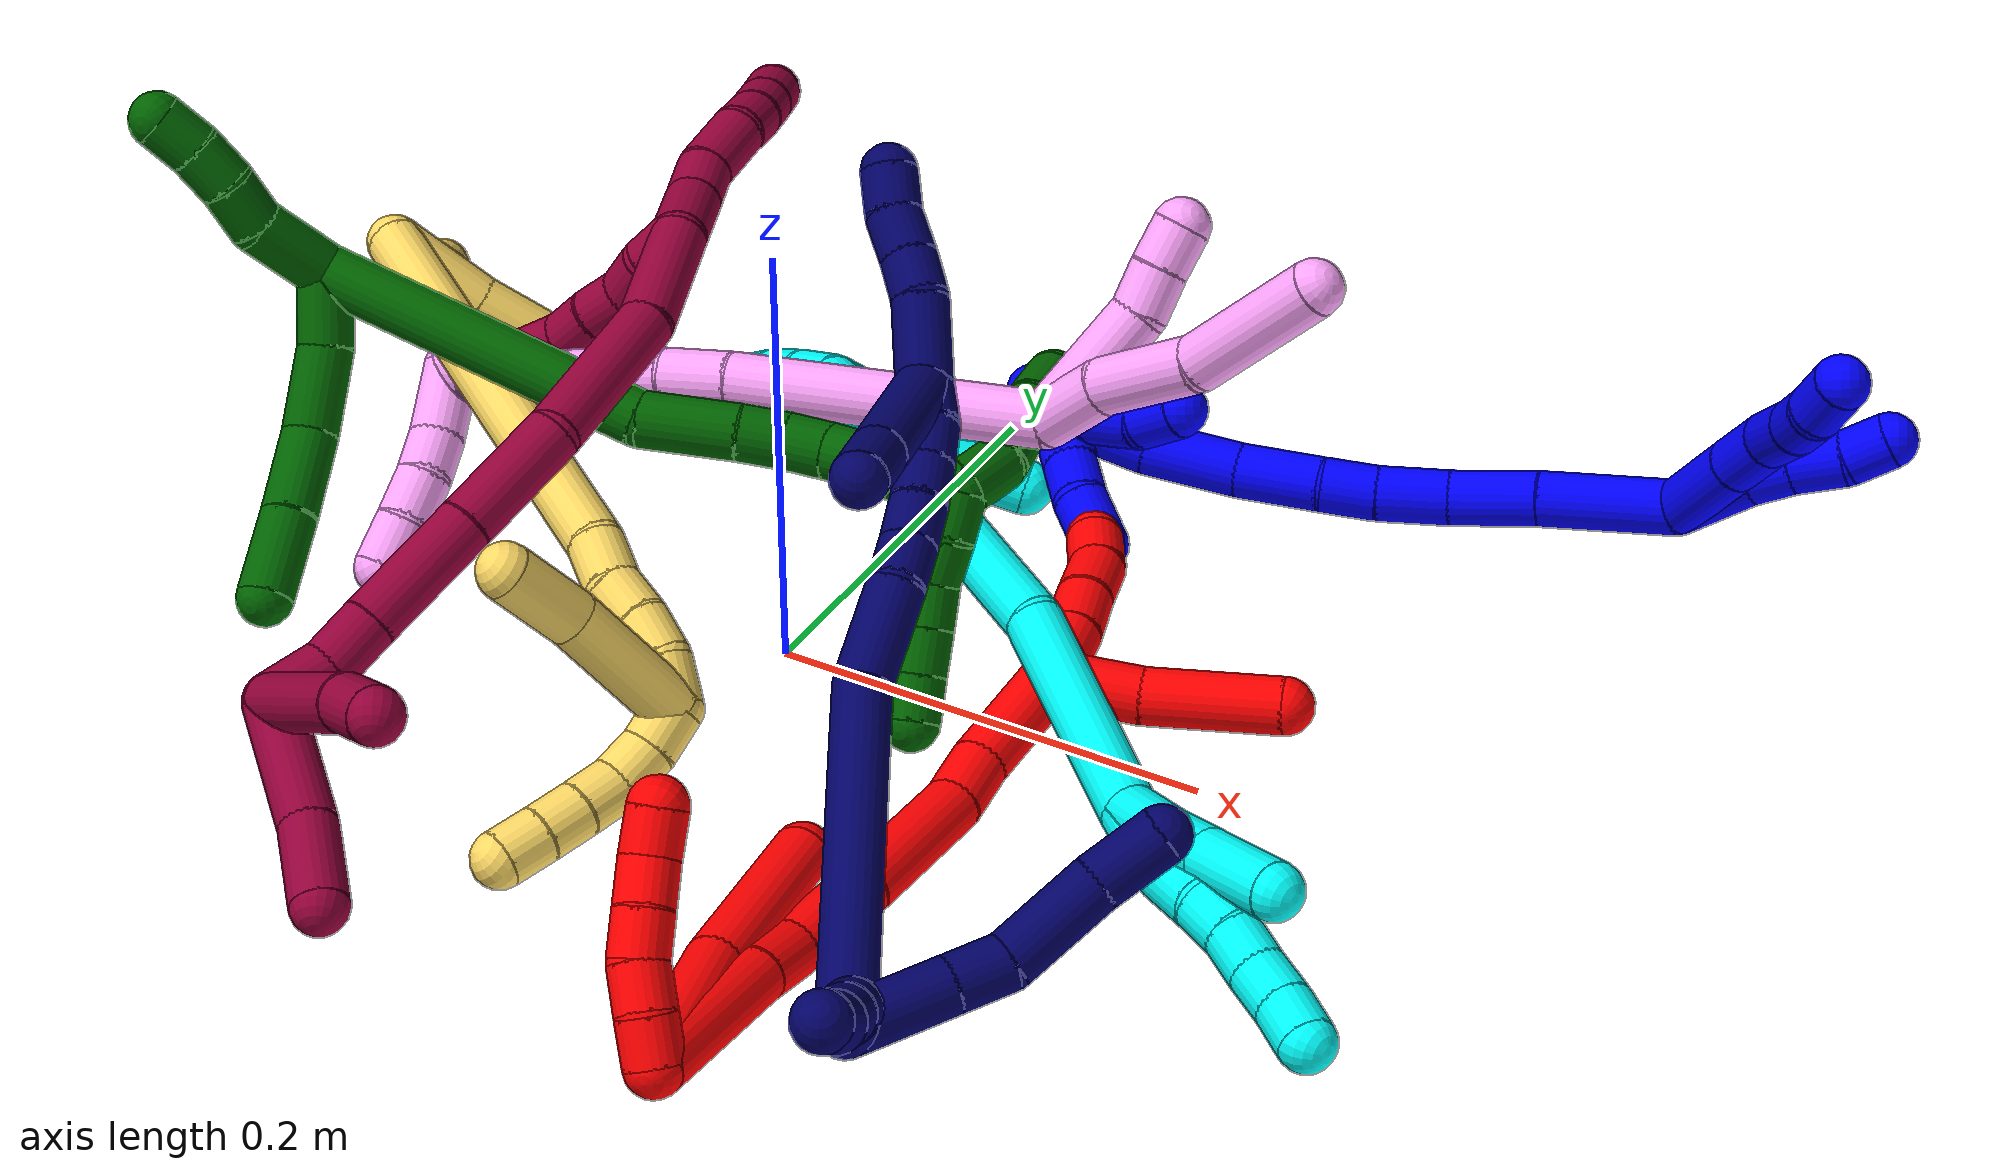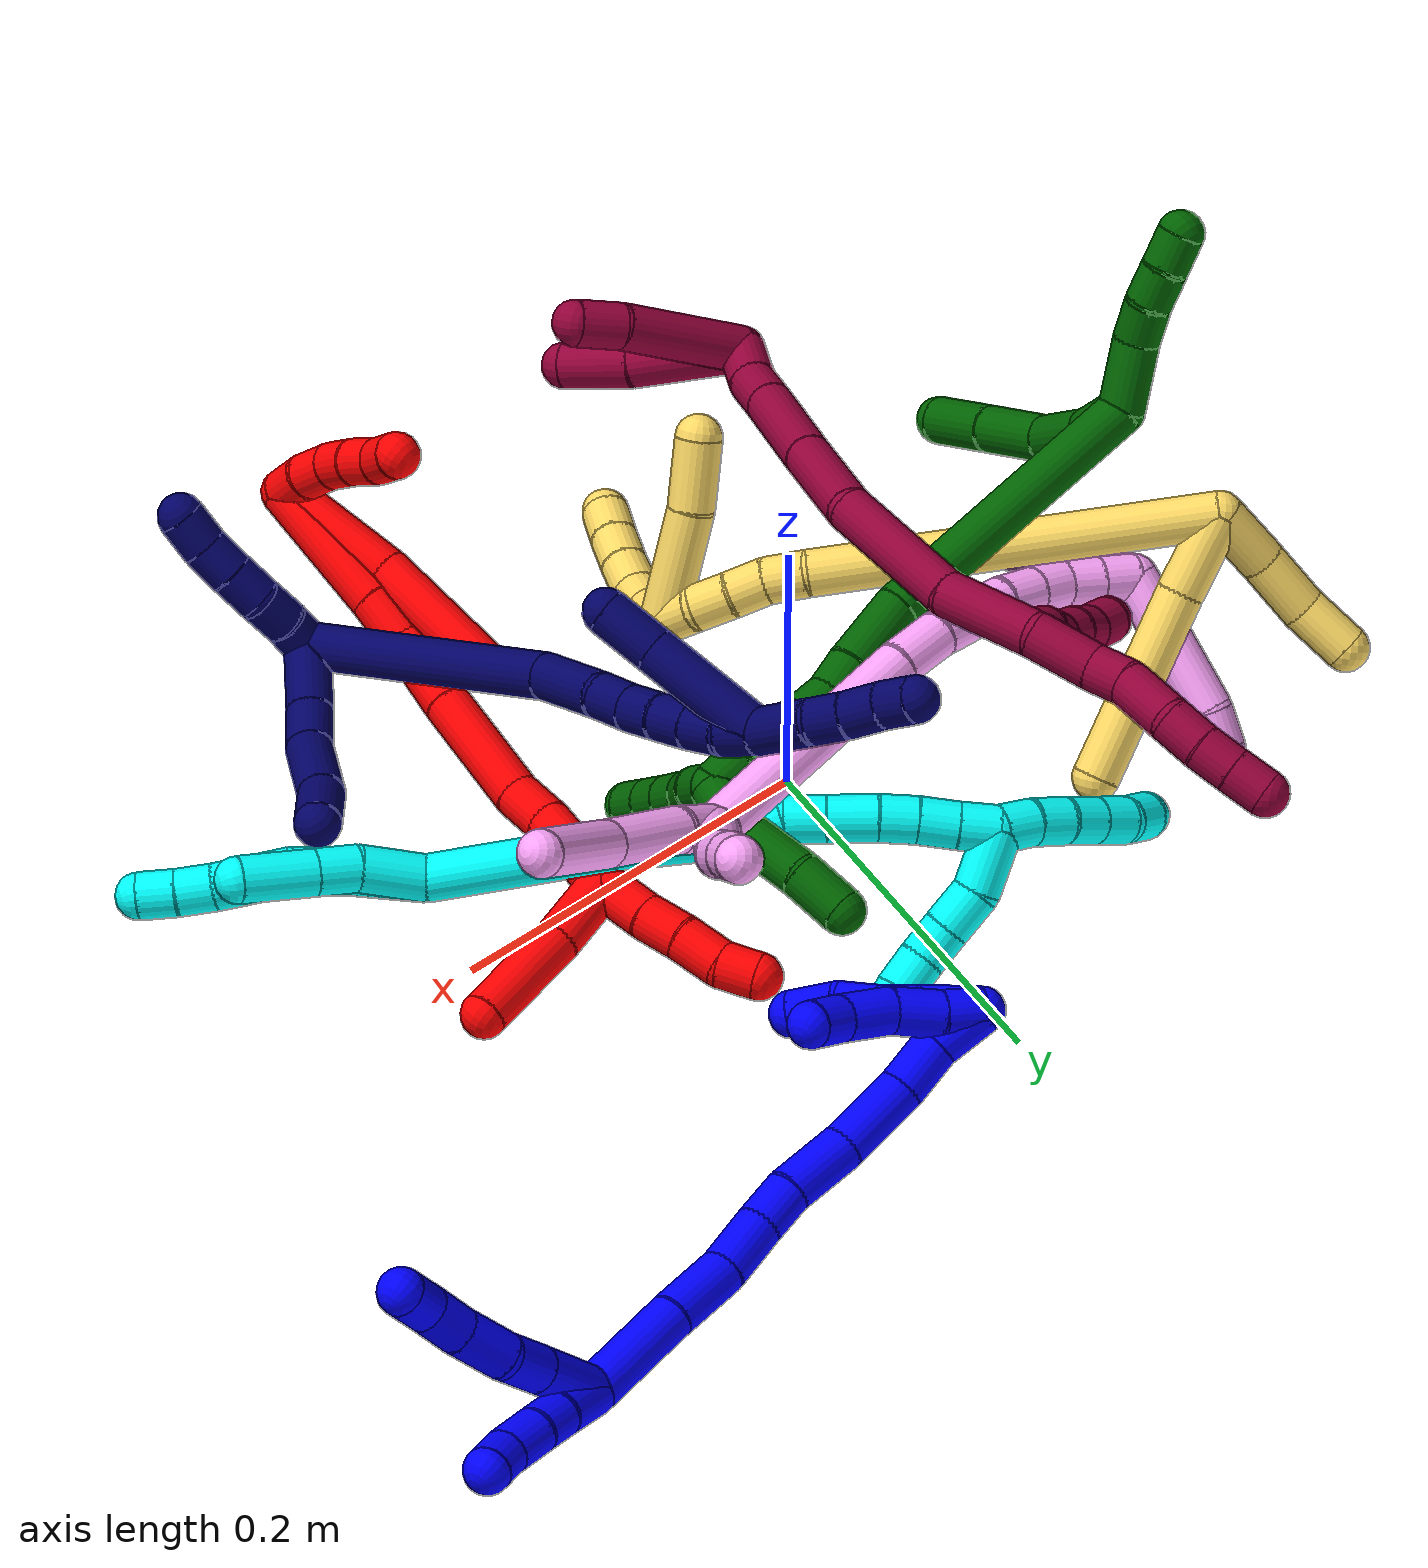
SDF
<sdf version="1.7">
 <world name="default">
  <plugin name="TubeGeneratorPlugin" filename="libtube_generator_plugin.so"/>
  <model name="photoneo_s_sensor">
   <static>1</static>
   <pose>0 0 2 1.57079 1.57079 3.14159</pose>
   <link name="link">
    <inertial><mass>0.1</mass></inertial>
    <sensor name="sensor" type="depth">
     <update_rate>30</update_rate>
     <camera>
      <horizontal_fov>1.22</horizontal_fov>
      <image><width>1920</width><height>1200</height><format>B8G8R8</format></image>
      <clip><near>0.1</near><far>4</far></clip>
      <depth_camera><output>points</output></depth_camera>
     </camera>
     <plugin name="camera_plugin" filename="libgazebo_ros_depth_camera.so">
      <baseline>0.2</baseline>
      <alwaysOn>1</alwaysOn>
      <updateRate>0.0</updateRate>
      <cameraName>camera_ir</cameraName>
      <imageTopicName>/camera/color/image_raw</imageTopicName>
      <cameraInfoTopicName>/camera/color/camera_info</cameraInfoTopicName>
      <depthImageTopicName>/camera/depth/image_raw</depthImageTopicName>
      <depthImageCameraInfoTopicName>/camera/depth/camera_info</depthImageCameraInfoTopicName>
      <pointCloudTopicName>/camera/depth/points</pointCloudTopicName>
      <frameName>fr_optical</frameName>
      <pointCloudCutoff>0.1</pointCloudCutoff>
      <pointCloudCutoffMax>2.0</pointCloudCutoffMax>
      <distortionK1>0</distortionK1>
      <distortionK2>0</distortionK2>
      <distortionK3>0</distortionK3>
      <distortionT1>0</distortionT1>
      <distortionT2>0</distortionT2>
      <CxPrime>0</CxPrime>
      <Cx>0</Cx>
      <Cy>0</Cy>
      <focalLength>0</focalLength>
      <hackBaseline>0</hackBaseline>
     </plugin>
    </sensor>
   </link>
  </model>
  <gravity>0 0 -9.8</gravity>
  <magnetic_field>6e-06 2.3e-05 -4.2e-05</magnetic_field>
  <atmosphere type="adiabatic"/>
  <physics name="default_physics" default="0" type="ode">
   <max_step_size>0.003</max_step_size>
   <real_time_factor>1</real_time_factor>
   <real_time_update_rate>1000</real_time_update_rate>
   <max_contacts>10000</max_contacts>
   <ode>
    <solver>
     <type>quick</type>
     <iters>100</iters>
     <sor>1.3</sor>
     <use_dynamic_moi_rescaling>0</use_dynamic_moi_rescaling>
    </solver>
    <constraints>
     <contact_max_correcting_vel>0</contact_max_correcting_vel>
     <contact_surface_layer>0.001</contact_surface_layer>
     <cfm>0</cfm>
     <erp>0.2</erp>
    </constraints>
   </ode>
  </physics>
  <scene><ambient>0.4 0.4 0.4 1</ambient><background>0.7 0.7 0.7 1</background><shadows>0</shadows></scene>
  <audio><device>default</device></audio>
  <spherical_coordinates>
   <surface_model>EARTH_WGS84</surface_model>
   <latitude_deg>0</latitude_deg>
   <longitude_deg>0</longitude_deg>
   <elevation>0</elevation>
   <heading_deg>0</heading_deg>
  </spherical_coordinates>
  <model name="bin">
   <static>1</static>
   <link name="bottom">
    <collision name="collision-bottom">
     <pose>0 0 -0.01 0 -0 0</pose>
     <geometry><box><size>0.8 0.6 0.02</size></box></geometry>
     <surface>
      <friction><ode><mu>100</mu><mu2>100</mu2></ode></friction>
      <contact><collide_bitmask>65535</collide_bitmask></contact>
     </surface>
    </collision>
   </link>
   <link name="west_wall">
    <collision name="collision-west_wall">
     <pose>-0.41 0 0.1 0 -0 0</pose>
     <geometry><box><size>0.02 0.6 0.2</size></box></geometry>
     <surface>
      <friction><ode><mu>100</mu><mu2>100</mu2></ode></friction>
      <contact><collide_bitmask>65535</collide_bitmask></contact>
     </surface>
    </collision>
   </link>
   <link name="east_wall">
    <collision name="collision-east_wall">
     <pose>0.41 0 0.1 0 -0 0</pose>
     <geometry><box><size>0.02 0.6 0.2</size></box></geometry>
     <surface>
      <friction><ode><mu>100</mu><mu2>100</mu2></ode></friction>
      <contact><collide_bitmask>65535</collide_bitmask></contact>
     </surface>
    </collision>
   </link>
   <link name="south_wall">
    <collision name="collision-south_wall">
     <pose>0 -0.31 0.1 0 -0 0</pose>
     <geometry><box><size>0.8 0.02 0.2</size></box></geometry>
     <surface>
      <friction><ode><mu>100</mu><mu2>100</mu2></ode></friction>
      <contact><collide_bitmask>65535</collide_bitmask></contact>
     </surface>
    </collision>
   </link>
   <link name="north_wall">
    <collision name="collision-north_wall">
     <pose>0 0.31 0.1 0 -0 0</pose>
     <geometry><box><size>0.8 0.02 0.2</size></box></geometry>
     <surface>
      <friction><ode><mu>100</mu><mu2>100</mu2></ode></friction>
      <contact><collide_bitmask>65535</collide_bitmask></contact>
     </surface>
    </collision>
   </link>
  </model>
  <model name="1">
   <static>0</static>
   <link name="1">
    <collision name="collision-cylinder-e_1_2_8">
     <pose>0.009985 -0.016543 0.01285 0.910367 0.444798 0.220477</pose>
     <geometry><cylinder><radius>0.0125</radius><length>0.04641</length></cylinder></geometry>
     <surface>
      <friction><ode><mu>1.16</mu><mu2>1.16</mu2><slip1>0</slip1><slip2>0</slip2></ode></friction>
      <contact><ode><kp>1e+06</kp><kd>1</kd><max_vel>0</max_vel><min_depth>0.001</min_depth></ode></contact>
     </surface>
    </collision>
    <visual name="visual-cylinder-e_1_2_8">
     <pose>0.009985 -0.016543 0.01285 0.910367 0.444798 0.220477</pose>
     <geometry><cylinder><radius>0.0125</radius><length>0.04641</length></cylinder></geometry>
     <material><ambient>0 0 1 1</ambient></material>
    </visual>
    <collision name="collision-cylinder-e_2_8_9">
     <pose>0.025883 -0.042737 0.033381 0.898678 0.447035 0.21837</pose>
     <geometry><cylinder><radius>0.0125</radius><length>0.027358</length></cylinder></geometry>
     <surface>
      <friction><ode><mu>1.16</mu><mu2>1.16</mu2><slip1>0</slip1><slip2>0</slip2></ode></friction>
      <contact><ode><kp>1e+06</kp><kd>1</kd><max_vel>0</max_vel><min_depth>0.001</min_depth></ode></contact>
     </surface>
    </collision>
    <visual name="visual-cylinder-e_2_8_9">
     <pose>0.025883 -0.042737 0.033381 0.898678 0.447035 0.21837</pose>
     <geometry><cylinder><radius>0.0125</radius><length>0.027358</length></cylinder></geometry>
     <material><ambient>0 0 1 1</ambient></material>
    </visual>
    <collision name="collision-cylinder-e_3_9_10">
     <pose>0.042039 -0.061512 0.046894 1.00192 0.757629 0.429182</pose>
     <geometry><cylinder><radius>0.0125</radius><length>0.02981</length></cylinder></geometry>
     <surface>
      <friction><ode><mu>1.16</mu><mu2>1.16</mu2><slip1>0</slip1><slip2>0</slip2></ode></friction>
      <contact><ode><kp>1e+06</kp><kd>1</kd><max_vel>0</max_vel><min_depth>0.001</min_depth></ode></contact>
     </surface>
    </collision>
    <visual name="visual-cylinder-e_3_9_10">
     <pose>0.042039 -0.061512 0.046894 1.00192 0.757629 0.429182</pose>
     <geometry><cylinder><radius>0.0125</radius><length>0.02981</length></cylinder></geometry>
     <material><ambient>0 0 1 1</ambient></material>
    </visual>
    <collision name="collision-cylinder-e_4_10_11">
     <pose>0.059913 -0.078558 0.056672 1.10884 0.71156 0.452308</pose>
     <geometry><cylinder><radius>0.0125</radius><length>0.023375</length></cylinder></geometry>
     <surface>
      <friction><ode><mu>1.16</mu><mu2>1.16</mu2><slip1>0</slip1><slip2>0</slip2></ode></friction>
      <contact><ode><kp>1e+06</kp><kd>1</kd><max_vel>0</max_vel><min_depth>0.001</min_depth></ode></contact>
     </surface>
    </collision>
    <visual name="visual-cylinder-e_4_10_11">
     <pose>0.059913 -0.078558 0.056672 1.10884 0.71156 0.452308</pose>
     <geometry><cylinder><radius>0.0125</radius><length>0.023375</length></cylinder></geometry>
     <material><ambient>0 0 1 1</ambient></material>
    </visual>
    <collision name="collision-cylinder-e_5_11_6">
     <pose>0.0721 -0.095635 0.065932 1.04468 0.406328 0.236082</pose>
     <geometry><cylinder><radius>0.0125</radius><length>0.023047</length></cylinder></geometry>
     <surface>
      <friction><ode><mu>1.16</mu><mu2>1.16</mu2><slip1>0</slip1><slip2>0</slip2></ode></friction>
      <contact><ode><kp>1e+06</kp><kd>1</kd><max_vel>0</max_vel><min_depth>0.001</min_depth></ode></contact>
     </surface>
    </collision>
    <visual name="visual-cylinder-e_5_11_6">
     <pose>0.0721 -0.095635 0.065932 1.04468 0.406328 0.236082</pose>
     <geometry><cylinder><radius>0.0125</radius><length>0.023047</length></cylinder></geometry>
     <material><ambient>0 0 1 1</ambient></material>
    </visual>
    <collision name="collision-cylinder-e_1_2_12">
     <pose>0.001098 -0.007843 0.015847 0.459548 0.062027 0.014513</pose>
     <geometry><cylinder><radius>0.0125</radius><length>0.035432</length></cylinder></geometry>
     <surface>
      <friction><ode><mu>1.16</mu><mu2>1.16</mu2><slip1>0</slip1><slip2>0</slip2></ode></friction>
      <contact><ode><kp>1e+06</kp><kd>1</kd><max_vel>0</max_vel><min_depth>0.001</min_depth></ode></contact>
     </surface>
    </collision>
    <visual name="visual-cylinder-e_1_2_12">
     <pose>0.001098 -0.007843 0.015847 0.459548 0.062027 0.014513</pose>
     <geometry><cylinder><radius>0.0125</radius><length>0.035432</length></cylinder></geometry>
     <material><ambient>0 0 1 1</ambient></material>
    </visual>
    <collision name="collision-cylinder-e_2_12_13">
     <pose>0.003315 -0.018981 0.041166 0.334862 0.111109 0.018798</pose>
     <geometry><cylinder><radius>0.0125</radius><length>0.02018</length></cylinder></geometry>
     <surface>
      <friction><ode><mu>1.16</mu><mu2>1.16</mu2><slip1>0</slip1><slip2>0</slip2></ode></friction>
      <contact><ode><kp>1e+06</kp><kd>1</kd><max_vel>0</max_vel><min_depth>0.001</min_depth></ode></contact>
     </surface>
    </collision>
    <visual name="visual-cylinder-e_2_12_13">
     <pose>0.003315 -0.018981 0.041166 0.334862 0.111109 0.018798</pose>
     <geometry><cylinder><radius>0.0125</radius><length>0.02018</length></cylinder></geometry>
     <material><ambient>0 0 1 1</ambient></material>
    </visual>
    <collision name="collision-cylinder-e_3_13_14">
     <pose>0.006267 -0.025028 0.062275 0.232111 0.152111 0.017767</pose>
     <geometry><cylinder><radius>0.0125</radius><length>0.024198</length></cylinder></geometry>
     <surface>
      <friction><ode><mu>1.16</mu><mu2>1.16</mu2><slip1>0</slip1><slip2>0</slip2></ode></friction>
      <contact><ode><kp>1e+06</kp><kd>1</kd><max_vel>0</max_vel><min_depth>0.001</min_depth></ode></contact>
     </surface>
    </collision>
    <visual name="visual-cylinder-e_3_13_14">
     <pose>0.006267 -0.025028 0.062275 0.232111 0.152111 0.017767</pose>
     <geometry><cylinder><radius>0.0125</radius><length>0.024198</length></cylinder></geometry>
     <material><ambient>0 0 1 1</ambient></material>
    </visual>
    <collision name="collision-cylinder-e_4_14_5">
     <pose>0.007671 -0.031728 0.083194 0.402403 -0.042535 -0.008677</pose>
     <geometry><cylinder><radius>0.0125</radius><length>0.02019</length></cylinder></geometry>
     <surface>
      <friction><ode><mu>1.16</mu><mu2>1.16</mu2><slip1>0</slip1><slip2>0</slip2></ode></friction>
      <contact><ode><kp>1e+06</kp><kd>1</kd><max_vel>0</max_vel><min_depth>0.001</min_depth></ode></contact>
     </surface>
    </collision>
    <visual name="visual-cylinder-e_4_14_5">
     <pose>0.007671 -0.031728 0.083194 0.402403 -0.042535 -0.008677</pose>
     <geometry><cylinder><radius>0.0125</radius><length>0.02019</length></cylinder></geometry>
     <material><ambient>0 0 1 1</ambient></material>
    </visual>
    <collision name="collision-cylinder-e_1_2_15">
     <pose>-0.00426 -0.000647 -0.030305 3.12024 -0.139625 -2.83853</pose>
     <geometry><cylinder><radius>0.0125</radius><length>0.061219</length></cylinder></geometry>
     <surface>
      <friction><ode><mu>1.16</mu><mu2>1.16</mu2><slip1>0</slip1><slip2>0</slip2></ode></friction>
      <contact><ode><kp>1e+06</kp><kd>1</kd><max_vel>0</max_vel><min_depth>0.001</min_depth></ode></contact>
     </surface>
    </collision>
    <visual name="visual-cylinder-e_1_2_15">
     <pose>-0.00426 -0.000647 -0.030305 3.12024 -0.139625 -2.83853</pose>
     <geometry><cylinder><radius>0.0125</radius><length>0.061219</length></cylinder></geometry>
     <material><ambient>0 0 1 1</ambient></material>
    </visual>
    <collision name="collision-cylinder-e_2_15_16">
     <pose>-0.011581 -0.000237 -0.080439 -3.0883 -0.152968 2.47214</pose>
     <geometry><cylinder><radius>0.0125</radius><length>0.040184</length></cylinder></geometry>
     <surface>
      <friction><ode><mu>1.16</mu><mu2>1.16</mu2><slip1>0</slip1><slip2>0</slip2></ode></friction>
      <contact><ode><kp>1e+06</kp><kd>1</kd><max_vel>0</max_vel><min_depth>0.001</min_depth></ode></contact>
     </surface>
    </collision>
    <visual name="visual-cylinder-e_2_15_16">
     <pose>-0.011581 -0.000237 -0.080439 -3.0883 -0.152968 2.47214</pose>
     <geometry><cylinder><radius>0.0125</radius><length>0.040184</length></cylinder></geometry>
     <material><ambient>0 0 1 1</ambient></material>
    </visual>
    <collision name="collision-cylinder-e_3_16_17">
     <pose>-0.015246 -0.00047 -0.116675 3.06309 -0.036615 -0.872514</pose>
     <geometry><cylinder><radius>0.0125</radius><length>0.032937</length></cylinder></geometry>
     <surface>
      <friction><ode><mu>1.16</mu><mu2>1.16</mu2><slip1>0</slip1><slip2>0</slip2></ode></friction>
      <contact><ode><kp>1e+06</kp><kd>1</kd><max_vel>0</max_vel><min_depth>0.001</min_depth></ode></contact>
     </surface>
    </collision>
    <visual name="visual-cylinder-e_3_16_17">
     <pose>-0.015246 -0.00047 -0.116675 3.06309 -0.036615 -0.872514</pose>
     <geometry><cylinder><radius>0.0125</radius><length>0.032937</length></cylinder></geometry>
     <material><ambient>0 0 1 1</ambient></material>
    </visual>
    <collision name="collision-cylinder-e_4_17_18">
     <pose>-0.01699 -0.003724 -0.145271 2.98186 -0.092169 -1.04549</pose>
     <geometry><cylinder><radius>0.0125</radius><length>0.024798</length></cylinder></geometry>
     <surface>
      <friction><ode><mu>1.16</mu><mu2>1.16</mu2><slip1>0</slip1><slip2>0</slip2></ode></friction>
      <contact><ode><kp>1e+06</kp><kd>1</kd><max_vel>0</max_vel><min_depth>0.001</min_depth></ode></contact>
     </surface>
    </collision>
    <visual name="visual-cylinder-e_4_17_18">
     <pose>-0.01699 -0.003724 -0.145271 2.98186 -0.092169 -1.04549</pose>
     <geometry><cylinder><radius>0.0125</radius><length>0.024798</length></cylinder></geometry>
     <material><ambient>0 0 1 1</ambient></material>
    </visual>
    <collision name="collision-cylinder-e_5_18_19">
     <pose>-0.022746 -0.007206 -0.176241 3.06091 -0.240198 -2.49602</pose>
     <geometry><cylinder><radius>0.0125</radius><length>0.038798</length></cylinder></geometry>
     <surface>
      <friction><ode><mu>1.16</mu><mu2>1.16</mu2><slip1>0</slip1><slip2>0</slip2></ode></friction>
      <contact><ode><kp>1e+06</kp><kd>1</kd><max_vel>0</max_vel><min_depth>0.001</min_depth></ode></contact>
     </surface>
    </collision>
    <visual name="visual-cylinder-e_5_18_19">
     <pose>-0.022746 -0.007206 -0.176241 3.06091 -0.240198 -2.49602</pose>
     <geometry><cylinder><radius>0.0125</radius><length>0.038798</length></cylinder></geometry>
     <material><ambient>0 0 1 1</ambient></material>
    </visual>
    <collision name="collision-cylinder-e_6_19_20">
     <pose>-0.031448 -0.013061 -0.216191 2.93955 -0.186945 -1.4927</pose>
     <geometry><cylinder><radius>0.0125</radius><length>0.043985</length></cylinder></geometry>
     <surface>
      <friction><ode><mu>1.16</mu><mu2>1.16</mu2><slip1>0</slip1><slip2>0</slip2></ode></friction>
      <contact><ode><kp>1e+06</kp><kd>1</kd><max_vel>0</max_vel><min_depth>0.001</min_depth></ode></contact>
     </surface>
    </collision>
    <visual name="visual-cylinder-e_6_19_20">
     <pose>-0.031448 -0.013061 -0.216191 2.93955 -0.186945 -1.4927</pose>
     <geometry><cylinder><radius>0.0125</radius><length>0.043985</length></cylinder></geometry>
     <material><ambient>0 0 1 1</ambient></material>
    </visual>
    <collision name="collision-cylinder-e_7_20_21">
     <pose>-0.037393 -0.022875 -0.250728 2.75273 -0.127844 -0.628567</pose>
     <geometry><cylinder><radius>0.0125</radius><length>0.02913</length></cylinder></geometry>
     <surface>
      <friction><ode><mu>1.16</mu><mu2>1.16</mu2><slip1>0</slip1><slip2>0</slip2></ode></friction>
      <contact><ode><kp>1e+06</kp><kd>1</kd><max_vel>0</max_vel><min_depth>0.001</min_depth></ode></contact>
     </surface>
    </collision>
    <visual name="visual-cylinder-e_7_20_21">
     <pose>-0.037393 -0.022875 -0.250728 2.75273 -0.127844 -0.628567</pose>
     <geometry><cylinder><radius>0.0125</radius><length>0.02913</length></cylinder></geometry>
     <material><ambient>0 0 1 1</ambient></material>
    </visual>
    <collision name="collision-cylinder-e_8_21_1">
     <pose>-0.044675 -0.03421 -0.27617 2.68988 -0.384171 -1.4048</pose>
     <geometry><cylinder><radius>0.0125</radius><length>0.028949</length></cylinder></geometry>
     <surface>
      <friction><ode><mu>1.16</mu><mu2>1.16</mu2><slip1>0</slip1><slip2>0</slip2></ode></friction>
      <contact><ode><kp>1e+06</kp><kd>1</kd><max_vel>0</max_vel><min_depth>0.001</min_depth></ode></contact>
     </surface>
    </collision>
    <visual name="visual-cylinder-e_8_21_1">
     <pose>-0.044675 -0.03421 -0.27617 2.68988 -0.384171 -1.4048</pose>
     <geometry><cylinder><radius>0.0125</radius><length>0.028949</length></cylinder></geometry>
     <material><ambient>0 0 1 1</ambient></material>
    </visual>
    <collision name="collision-cylinder-e_1_1_22">
     <pose>-0.036626 -0.038233 -0.280882 -0.244173 1.058 -0.143205</pose>
     <geometry><cylinder><radius>0.0125</radius><length>0.030925</length></cylinder></geometry>
     <surface>
      <friction><ode><mu>1.16</mu><mu2>1.16</mu2><slip1>0</slip1><slip2>0</slip2></ode></friction>
      <contact><ode><kp>1e+06</kp><kd>1</kd><max_vel>0</max_vel><min_depth>0.001</min_depth></ode></contact>
     </surface>
    </collision>
    <visual name="visual-cylinder-e_1_1_22">
     <pose>-0.036626 -0.038233 -0.280882 -0.244173 1.058 -0.143205</pose>
     <geometry><cylinder><radius>0.0125</radius><length>0.030925</length></cylinder></geometry>
     <material><ambient>0 0 1 1</ambient></material>
    </visual>
    <collision name="collision-cylinder-e_2_22_23">
     <pose>-0.013383 -0.032068 -0.270515 -0.964156 1.07591 -0.605229</pose>
     <geometry><cylinder><radius>0.0125</radius><length>0.022202</length></cylinder></geometry>
     <surface>
      <friction><ode><mu>1.16</mu><mu2>1.16</mu2><slip1>0</slip1><slip2>0</slip2></ode></friction>
      <contact><ode><kp>1e+06</kp><kd>1</kd><max_vel>0</max_vel><min_depth>0.001</min_depth></ode></contact>
     </surface>
    </collision>
    <visual name="visual-cylinder-e_2_22_23">
     <pose>-0.013383 -0.032068 -0.270515 -0.964156 1.07591 -0.605229</pose>
     <geometry><cylinder><radius>0.0125</radius><length>0.022202</length></cylinder></geometry>
     <material><ambient>0 0 1 1</ambient></material>
    </visual>
    <collision name="collision-cylinder-e_3_23_24">
     <pose>0.006543 -0.024824 -0.264518 -0.771953 1.18084 -0.531762</pose>
     <geometry><cylinder><radius>0.0125</radius><length>0.021963</length></cylinder></geometry>
     <surface>
      <friction><ode><mu>1.16</mu><mu2>1.16</mu2><slip1>0</slip1><slip2>0</slip2></ode></friction>
      <contact><ode><kp>1e+06</kp><kd>1</kd><max_vel>0</max_vel><min_depth>0.001</min_depth></ode></contact>
     </surface>
    </collision>
    <visual name="visual-cylinder-e_3_23_24">
     <pose>0.006543 -0.024824 -0.264518 -0.771953 1.18084 -0.531762</pose>
     <geometry><cylinder><radius>0.0125</radius><length>0.021963</length></cylinder></geometry>
     <material><ambient>0 0 1 1</ambient></material>
    </visual>
    <collision name="collision-cylinder-e_4_24_4">
     <pose>0.026469 -0.01609 -0.256448 -0.853505 0.901588 -0.43327</pose>
     <geometry><cylinder><radius>0.0125</radius><length>0.02491</length></cylinder></geometry>
     <surface>
      <friction><ode><mu>1.16</mu><mu2>1.16</mu2><slip1>0</slip1><slip2>0</slip2></ode></friction>
      <contact><ode><kp>1e+06</kp><kd>1</kd><max_vel>0</max_vel><min_depth>0.001</min_depth></ode></contact>
     </surface>
    </collision>
    <visual name="visual-cylinder-e_4_24_4">
     <pose>0.026469 -0.01609 -0.256448 -0.853505 0.901588 -0.43327</pose>
     <geometry><cylinder><radius>0.0125</radius><length>0.02491</length></cylinder></geometry>
     <material><ambient>0 0 1 1</ambient></material>
    </visual>
    <collision name="collision-cylinder-e_1_1_25">
     <pose>-0.042723 -0.041103 -0.280577 0.13428 0.761581 0.053824</pose>
     <geometry><cylinder><radius>0.0125</radius><length>0.021378</length></cylinder></geometry>
     <surface>
      <friction><ode><mu>1.16</mu><mu2>1.16</mu2><slip1>0</slip1><slip2>0</slip2></ode></friction>
      <contact><ode><kp>1e+06</kp><kd>1</kd><max_vel>0</max_vel><min_depth>0.001</min_depth></ode></contact>
     </surface>
    </collision>
    <visual name="visual-cylinder-e_1_1_25">
     <pose>-0.042723 -0.041103 -0.280577 0.13428 0.761581 0.053824</pose>
     <geometry><cylinder><radius>0.0125</radius><length>0.021378</length></cylinder></geometry>
     <material><ambient>0 0 1 1</ambient></material>
    </visual>
    <collision name="collision-cylinder-e_2_25_26">
     <pose>-0.024744 -0.044413 -0.264655 0.26882 0.891467 0.129043</pose>
     <geometry><cylinder><radius>0.0125</radius><length>0.027257</length></cylinder></geometry>
     <surface>
      <friction><ode><mu>1.16</mu><mu2>1.16</mu2><slip1>0</slip1><slip2>0</slip2></ode></friction>
      <contact><ode><kp>1e+06</kp><kd>1</kd><max_vel>0</max_vel><min_depth>0.001</min_depth></ode></contact>
     </surface>
    </collision>
    <visual name="visual-cylinder-e_2_25_26">
     <pose>-0.024744 -0.044413 -0.264655 0.26882 0.891467 0.129043</pose>
     <geometry><cylinder><radius>0.0125</radius><length>0.027257</length></cylinder></geometry>
     <material><ambient>0 0 1 1</ambient></material>
    </visual>
    <collision name="collision-cylinder-e_3_26_27">
     <pose>-0.006 -0.049778 -0.244734 0.258973 0.59345 0.079585</pose>
     <geometry><cylinder><radius>0.0125</radius><length>0.029117</length></cylinder></geometry>
     <surface>
      <friction><ode><mu>1.16</mu><mu2>1.16</mu2><slip1>0</slip1><slip2>0</slip2></ode></friction>
      <contact><ode><kp>1e+06</kp><kd>1</kd><max_vel>0</max_vel><min_depth>0.001</min_depth></ode></contact>
     </surface>
    </collision>
    <visual name="visual-cylinder-e_3_26_27">
     <pose>-0.006 -0.049778 -0.244734 0.258973 0.59345 0.079585</pose>
     <geometry><cylinder><radius>0.0125</radius><length>0.029117</length></cylinder></geometry>
     <material><ambient>0 0 1 1</ambient></material>
    </visual>
    <collision name="collision-cylinder-e_4_27_3">
     <pose>0.00579 -0.057621 -0.223694 0.469267 0.33424 0.080604</pose>
     <geometry><cylinder><radius>0.0125</radius><length>0.022249</length></cylinder></geometry>
     <surface>
      <friction><ode><mu>1.16</mu><mu2>1.16</mu2><slip1>0</slip1><slip2>0</slip2></ode></friction>
      <contact><ode><kp>1e+06</kp><kd>1</kd><max_vel>0</max_vel><min_depth>0.001</min_depth></ode></contact>
     </surface>
    </collision>
    <visual name="visual-cylinder-e_4_27_3">
     <pose>0.00579 -0.057621 -0.223694 0.469267 0.33424 0.080604</pose>
     <geometry><cylinder><radius>0.0125</radius><length>0.022249</length></cylinder></geometry>
     <material><ambient>0 0 1 1</ambient></material>
    </visual>
    <collision name="collision-sphere-3">
     <pose>0.00944 -0.062373 -0.214322 0 -0 0</pose>
     <geometry><sphere><radius>0.0125</radius></sphere></geometry>
     <surface>
      <friction><ode><mu>1.16</mu><mu2>1.16</mu2><slip1>0</slip1><slip2>0</slip2></ode></friction>
      <contact><ode><kp>1e+06</kp><kd>1</kd><max_vel>0</max_vel><min_depth>0.001</min_depth></ode></contact>
     </surface>
    </collision>
    <visual name="visual-sphere-3">
     <pose>0.00944 -0.062373 -0.214322 0 -0 0</pose>
     <geometry><sphere><radius>0.0125</radius></sphere></geometry>
     <material><ambient>0 0 1 1</ambient></material>
    </visual>
    <collision name="collision-sphere-27">
     <pose>0.002141 -0.052868 -0.233067 0 -0 0</pose>
     <geometry><sphere><radius>0.0125</radius></sphere></geometry>
     <surface>
      <friction><ode><mu>1.16</mu><mu2>1.16</mu2><slip1>0</slip1><slip2>0</slip2></ode></friction>
      <contact><ode><kp>1e+06</kp><kd>1</kd><max_vel>0</max_vel><min_depth>0.001</min_depth></ode></contact>
     </surface>
    </collision>
    <visual name="visual-sphere-27">
     <pose>0.002141 -0.052868 -0.233067 0 -0 0</pose>
     <geometry><sphere><radius>0.0125</radius></sphere></geometry>
     <material><ambient>0 0 1 1</ambient></material>
    </visual>
    <collision name="collision-sphere-26">
     <pose>-0.014142 -0.046687 -0.2564 0 -0 0</pose>
     <geometry><sphere><radius>0.0125</radius></sphere></geometry>
     <surface>
      <friction><ode><mu>1.16</mu><mu2>1.16</mu2><slip1>0</slip1><slip2>0</slip2></ode></friction>
      <contact><ode><kp>1e+06</kp><kd>1</kd><max_vel>0</max_vel><min_depth>0.001</min_depth></ode></contact>
     </surface>
    </collision>
    <visual name="visual-sphere-26">
     <pose>-0.014142 -0.046687 -0.2564 0 -0 0</pose>
     <geometry><sphere><radius>0.0125</radius></sphere></geometry>
     <material><ambient>0 0 1 1</ambient></material>
    </visual>
    <collision name="collision-sphere-25">
     <pose>-0.035347 -0.042139 -0.27291 0 -0 0</pose>
     <geometry><sphere><radius>0.0125</radius></sphere></geometry>
     <surface>
      <friction><ode><mu>1.16</mu><mu2>1.16</mu2><slip1>0</slip1><slip2>0</slip2></ode></friction>
      <contact><ode><kp>1e+06</kp><kd>1</kd><max_vel>0</max_vel><min_depth>0.001</min_depth></ode></contact>
     </surface>
    </collision>
    <visual name="visual-sphere-25">
     <pose>-0.035347 -0.042139 -0.27291 0 -0 0</pose>
     <geometry><sphere><radius>0.0125</radius></sphere></geometry>
     <material><ambient>0 0 1 1</ambient></material>
    </visual>
    <collision name="collision-sphere-4">
     <pose>0.036238 -0.010267 -0.251369 0 -0 0</pose>
     <geometry><sphere><radius>0.0125</radius></sphere></geometry>
     <surface>
      <friction><ode><mu>1.16</mu><mu2>1.16</mu2><slip1>0</slip1><slip2>0</slip2></ode></friction>
      <contact><ode><kp>1e+06</kp><kd>1</kd><max_vel>0</max_vel><min_depth>0.001</min_depth></ode></contact>
     </surface>
    </collision>
    <visual name="visual-sphere-4">
     <pose>0.036238 -0.010267 -0.251369 0 -0 0</pose>
     <geometry><sphere><radius>0.0125</radius></sphere></geometry>
     <material><ambient>0 0 1 1</ambient></material>
    </visual>
    <collision name="collision-sphere-24">
     <pose>0.016701 -0.021912 -0.261527 0 -0 0</pose>
     <geometry><sphere><radius>0.0125</radius></sphere></geometry>
     <surface>
      <friction><ode><mu>1.16</mu><mu2>1.16</mu2><slip1>0</slip1><slip2>0</slip2></ode></friction>
      <contact><ode><kp>1e+06</kp><kd>1</kd><max_vel>0</max_vel><min_depth>0.001</min_depth></ode></contact>
     </surface>
    </collision>
    <visual name="visual-sphere-24">
     <pose>0.016701 -0.021912 -0.261527 0 -0 0</pose>
     <geometry><sphere><radius>0.0125</radius></sphere></geometry>
     <material><ambient>0 0 1 1</ambient></material>
    </visual>
    <collision name="collision-sphere-23">
     <pose>-0.003614 -0.027736 -0.267509 0 -0 0</pose>
     <geometry><sphere><radius>0.0125</radius></sphere></geometry>
     <surface>
      <friction><ode><mu>1.16</mu><mu2>1.16</mu2><slip1>0</slip1><slip2>0</slip2></ode></friction>
      <contact><ode><kp>1e+06</kp><kd>1</kd><max_vel>0</max_vel><min_depth>0.001</min_depth></ode></contact>
     </surface>
    </collision>
    <visual name="visual-sphere-23">
     <pose>-0.003614 -0.027736 -0.267509 0 -0 0</pose>
     <geometry><sphere><radius>0.0125</radius></sphere></geometry>
     <material><ambient>0 0 1 1</ambient></material>
    </visual>
    <collision name="collision-sphere-22">
     <pose>-0.023152 -0.036399 -0.273521 0 -0 0</pose>
     <geometry><sphere><radius>0.0125</radius></sphere></geometry>
     <surface>
      <friction><ode><mu>1.16</mu><mu2>1.16</mu2><slip1>0</slip1><slip2>0</slip2></ode></friction>
      <contact><ode><kp>1e+06</kp><kd>1</kd><max_vel>0</max_vel><min_depth>0.001</min_depth></ode></contact>
     </surface>
    </collision>
    <visual name="visual-sphere-22">
     <pose>-0.023152 -0.036399 -0.273521 0 -0 0</pose>
     <geometry><sphere><radius>0.0125</radius></sphere></geometry>
     <material><ambient>0 0 1 1</ambient></material>
    </visual>
    <collision name="collision-sphere-1">
     <pose>-0.050099 -0.040067 -0.288243 0 -0 0</pose>
     <geometry><sphere><radius>0.0125</radius></sphere></geometry>
     <surface>
      <friction><ode><mu>1.16</mu><mu2>1.16</mu2><slip1>0</slip1><slip2>0</slip2></ode></friction>
      <contact><ode><kp>1e+06</kp><kd>1</kd><max_vel>0</max_vel><min_depth>0.001</min_depth></ode></contact>
     </surface>
    </collision>
    <visual name="visual-sphere-1">
     <pose>-0.050099 -0.040067 -0.288243 0 -0 0</pose>
     <geometry><sphere><radius>0.0125</radius></sphere></geometry>
     <material><ambient>0 0 1 1</ambient></material>
    </visual>
    <collision name="collision-sphere-21">
     <pose>-0.03925 -0.028352 -0.264096 0 -0 0</pose>
     <geometry><sphere><radius>0.0125</radius></sphere></geometry>
     <surface>
      <friction><ode><mu>1.16</mu><mu2>1.16</mu2><slip1>0</slip1><slip2>0</slip2></ode></friction>
      <contact><ode><kp>1e+06</kp><kd>1</kd><max_vel>0</max_vel><min_depth>0.001</min_depth></ode></contact>
     </surface>
    </collision>
    <visual name="visual-sphere-21">
     <pose>-0.03925 -0.028352 -0.264096 0 -0 0</pose>
     <geometry><sphere><radius>0.0125</radius></sphere></geometry>
     <material><ambient>0 0 1 1</ambient></material>
    </visual>
    <collision name="collision-sphere-6">
     <pose>0.076654 -0.104789 0.071248 0 -0 0</pose>
     <geometry><sphere><radius>0.0125</radius></sphere></geometry>
     <surface>
      <friction><ode><mu>1.16</mu><mu2>1.16</mu2><slip1>0</slip1><slip2>0</slip2></ode></friction>
      <contact><ode><kp>1e+06</kp><kd>1</kd><max_vel>0</max_vel><min_depth>0.001</min_depth></ode></contact>
     </surface>
    </collision>
    <visual name="visual-sphere-6">
     <pose>0.076654 -0.104789 0.071248 0 -0 0</pose>
     <geometry><sphere><radius>0.0125</radius></sphere></geometry>
     <material><ambient>0 0 1 1</ambient></material>
    </visual>
    <collision name="collision-sphere-11">
     <pose>0.067545 -0.086482 0.060617 0 -0 0</pose>
     <geometry><sphere><radius>0.0125</radius></sphere></geometry>
     <surface>
      <friction><ode><mu>1.16</mu><mu2>1.16</mu2><slip1>0</slip1><slip2>0</slip2></ode></friction>
      <contact><ode><kp>1e+06</kp><kd>1</kd><max_vel>0</max_vel><min_depth>0.001</min_depth></ode></contact>
     </surface>
    </collision>
    <visual name="visual-sphere-11">
     <pose>0.067545 -0.086482 0.060617 0 -0 0</pose>
     <geometry><sphere><radius>0.0125</radius></sphere></geometry>
     <material><ambient>0 0 1 1</ambient></material>
    </visual>
    <collision name="collision-sphere-10">
     <pose>0.052281 -0.070635 0.052726 0 -0 0</pose>
     <geometry><sphere><radius>0.0125</radius></sphere></geometry>
     <surface>
      <friction><ode><mu>1.16</mu><mu2>1.16</mu2><slip1>0</slip1><slip2>0</slip2></ode></friction>
      <contact><ode><kp>1e+06</kp><kd>1</kd><max_vel>0</max_vel><min_depth>0.001</min_depth></ode></contact>
     </surface>
    </collision>
    <visual name="visual-sphere-10">
     <pose>0.052281 -0.070635 0.052726 0 -0 0</pose>
     <geometry><sphere><radius>0.0125</radius></sphere></geometry>
     <material><ambient>0 0 1 1</ambient></material>
    </visual>
    <collision name="collision-sphere-9">
     <pose>0.031796 -0.05239 0.041061 0 -0 0</pose>
     <geometry><sphere><radius>0.0125</radius></sphere></geometry>
     <surface>
      <friction><ode><mu>1.16</mu><mu2>1.16</mu2><slip1>0</slip1><slip2>0</slip2></ode></friction>
      <contact><ode><kp>1e+06</kp><kd>1</kd><max_vel>0</max_vel><min_depth>0.001</min_depth></ode></contact>
     </surface>
    </collision>
    <visual name="visual-sphere-9">
     <pose>0.031796 -0.05239 0.041061 0 -0 0</pose>
     <geometry><sphere><radius>0.0125</radius></sphere></geometry>
     <material><ambient>0 0 1 1</ambient></material>
    </visual>
    <collision name="collision-sphere-2">
     <geometry><sphere><radius>0.0125</radius></sphere></geometry>
     <surface>
      <friction><ode><mu>1.16</mu><mu2>1.16</mu2><slip1>0</slip1><slip2>0</slip2></ode></friction>
      <contact><ode><kp>1e+06</kp><kd>1</kd><max_vel>0</max_vel><min_depth>0.001</min_depth></ode></contact>
     </surface>
    </collision>
    <visual name="visual-sphere-2">
     <geometry><sphere><radius>0.0125</radius></sphere></geometry>
     <material><ambient>0 0 1 1</ambient></material>
    </visual>
    <collision name="collision-sphere-19">
     <pose>-0.027361 -0.008725 -0.195021 0 -0 0</pose>
     <geometry><sphere><radius>0.0125</radius></sphere></geometry>
     <surface>
      <friction><ode><mu>1.16</mu><mu2>1.16</mu2><slip1>0</slip1><slip2>0</slip2></ode></friction>
      <contact><ode><kp>1e+06</kp><kd>1</kd><max_vel>0</max_vel><min_depth>0.001</min_depth></ode></contact>
     </surface>
    </collision>
    <visual name="visual-sphere-19">
     <pose>-0.027361 -0.008725 -0.195021 0 -0 0</pose>
     <geometry><sphere><radius>0.0125</radius></sphere></geometry>
     <material><ambient>0 0 1 1</ambient></material>
    </visual>
    <collision name="collision-sphere-8">
     <pose>0.019969 -0.033085 0.0257 0 -0 0</pose>
     <geometry><sphere><radius>0.0125</radius></sphere></geometry>
     <surface>
      <friction><ode><mu>1.16</mu><mu2>1.16</mu2><slip1>0</slip1><slip2>0</slip2></ode></friction>
      <contact><ode><kp>1e+06</kp><kd>1</kd><max_vel>0</max_vel><min_depth>0.001</min_depth></ode></contact>
     </surface>
    </collision>
    <visual name="visual-sphere-8">
     <pose>0.019969 -0.033085 0.0257 0 -0 0</pose>
     <geometry><sphere><radius>0.0125</radius></sphere></geometry>
     <material><ambient>0 0 1 1</ambient></material>
    </visual>
    <collision name="collision-sphere-12">
     <pose>0.002196 -0.015685 0.031695 0 -0 0</pose>
     <geometry><sphere><radius>0.0125</radius></sphere></geometry>
     <surface>
      <friction><ode><mu>1.16</mu><mu2>1.16</mu2><slip1>0</slip1><slip2>0</slip2></ode></friction>
      <contact><ode><kp>1e+06</kp><kd>1</kd><max_vel>0</max_vel><min_depth>0.001</min_depth></ode></contact>
     </surface>
    </collision>
    <visual name="visual-sphere-12">
     <pose>0.002196 -0.015685 0.031695 0 -0 0</pose>
     <geometry><sphere><radius>0.0125</radius></sphere></geometry>
     <material><ambient>0 0 1 1</ambient></material>
    </visual>
    <collision name="collision-sphere-13">
     <pose>0.004434 -0.022276 0.050637 0 -0 0</pose>
     <geometry><sphere><radius>0.0125</radius></sphere></geometry>
     <surface>
      <friction><ode><mu>1.16</mu><mu2>1.16</mu2><slip1>0</slip1><slip2>0</slip2></ode></friction>
      <contact><ode><kp>1e+06</kp><kd>1</kd><max_vel>0</max_vel><min_depth>0.001</min_depth></ode></contact>
     </surface>
    </collision>
    <visual name="visual-sphere-13">
     <pose>0.004434 -0.022276 0.050637 0 -0 0</pose>
     <geometry><sphere><radius>0.0125</radius></sphere></geometry>
     <material><ambient>0 0 1 1</ambient></material>
    </visual>
    <collision name="collision-sphere-14">
     <pose>0.008101 -0.027779 0.073914 0 -0 0</pose>
     <geometry><sphere><radius>0.0125</radius></sphere></geometry>
     <surface>
      <friction><ode><mu>1.16</mu><mu2>1.16</mu2><slip1>0</slip1><slip2>0</slip2></ode></friction>
      <contact><ode><kp>1e+06</kp><kd>1</kd><max_vel>0</max_vel><min_depth>0.001</min_depth></ode></contact>
     </surface>
    </collision>
    <visual name="visual-sphere-14">
     <pose>0.008101 -0.027779 0.073914 0 -0 0</pose>
     <geometry><sphere><radius>0.0125</radius></sphere></geometry>
     <material><ambient>0 0 1 1</ambient></material>
    </visual>
    <collision name="collision-sphere-5">
     <pose>0.007242 -0.035678 0.092474 0 -0 0</pose>
     <geometry><sphere><radius>0.0125</radius></sphere></geometry>
     <surface>
      <friction><ode><mu>1.16</mu><mu2>1.16</mu2><slip1>0</slip1><slip2>0</slip2></ode></friction>
      <contact><ode><kp>1e+06</kp><kd>1</kd><max_vel>0</max_vel><min_depth>0.001</min_depth></ode></contact>
     </surface>
    </collision>
    <visual name="visual-sphere-5">
     <pose>0.007242 -0.035678 0.092474 0 -0 0</pose>
     <geometry><sphere><radius>0.0125</radius></sphere></geometry>
     <material><ambient>0 0 1 1</ambient></material>
    </visual>
    <collision name="collision-sphere-15">
     <pose>-0.00852 -0.001295 -0.06061 0 -0 0</pose>
     <geometry><sphere><radius>0.0125</radius></sphere></geometry>
     <surface>
      <friction><ode><mu>1.16</mu><mu2>1.16</mu2><slip1>0</slip1><slip2>0</slip2></ode></friction>
      <contact><ode><kp>1e+06</kp><kd>1</kd><max_vel>0</max_vel><min_depth>0.001</min_depth></ode></contact>
     </surface>
    </collision>
    <visual name="visual-sphere-15">
     <pose>-0.00852 -0.001295 -0.06061 0 -0 0</pose>
     <geometry><sphere><radius>0.0125</radius></sphere></geometry>
     <material><ambient>0 0 1 1</ambient></material>
    </visual>
    <collision name="collision-sphere-16">
     <pose>-0.014643 0.000821 -0.100268 0 -0 0</pose>
     <geometry><sphere><radius>0.0125</radius></sphere></geometry>
     <surface>
      <friction><ode><mu>1.16</mu><mu2>1.16</mu2><slip1>0</slip1><slip2>0</slip2></ode></friction>
      <contact><ode><kp>1e+06</kp><kd>1</kd><max_vel>0</max_vel><min_depth>0.001</min_depth></ode></contact>
     </surface>
    </collision>
    <visual name="visual-sphere-16">
     <pose>-0.014643 0.000821 -0.100268 0 -0 0</pose>
     <geometry><sphere><radius>0.0125</radius></sphere></geometry>
     <material><ambient>0 0 1 1</ambient></material>
    </visual>
    <collision name="collision-sphere-17">
     <pose>-0.015849 -0.00176 -0.133082 0 -0 0</pose>
     <geometry><sphere><radius>0.0125</radius></sphere></geometry>
     <surface>
      <friction><ode><mu>1.16</mu><mu2>1.16</mu2><slip1>0</slip1><slip2>0</slip2></ode></friction>
      <contact><ode><kp>1e+06</kp><kd>1</kd><max_vel>0</max_vel><min_depth>0.001</min_depth></ode></contact>
     </surface>
    </collision>
    <visual name="visual-sphere-17">
     <pose>-0.015849 -0.00176 -0.133082 0 -0 0</pose>
     <geometry><sphere><radius>0.0125</radius></sphere></geometry>
     <material><ambient>0 0 1 1</ambient></material>
    </visual>
    <collision name="collision-sphere-18">
     <pose>-0.018131 -0.005688 -0.15746 0 -0 0</pose>
     <geometry><sphere><radius>0.0125</radius></sphere></geometry>
     <surface>
      <friction><ode><mu>1.16</mu><mu2>1.16</mu2><slip1>0</slip1><slip2>0</slip2></ode></friction>
      <contact><ode><kp>1e+06</kp><kd>1</kd><max_vel>0</max_vel><min_depth>0.001</min_depth></ode></contact>
     </surface>
    </collision>
    <visual name="visual-sphere-18">
     <pose>-0.018131 -0.005688 -0.15746 0 -0 0</pose>
     <geometry><sphere><radius>0.0125</radius></sphere></geometry>
     <material><ambient>0 0 1 1</ambient></material>
    </visual>
    <collision name="collision-sphere-20">
     <pose>-0.035536 -0.017398 -0.237361 0 -0 0</pose>
     <geometry><sphere><radius>0.0125</radius></sphere></geometry>
     <surface>
      <friction><ode><mu>1.16</mu><mu2>1.16</mu2><slip1>0</slip1><slip2>0</slip2></ode></friction>
      <contact><ode><kp>1e+06</kp><kd>1</kd><max_vel>0</max_vel><min_depth>0.001</min_depth></ode></contact>
     </surface>
    </collision>
    <visual name="visual-sphere-20">
     <pose>-0.035536 -0.017398 -0.237361 0 -0 0</pose>
     <geometry><sphere><radius>0.0125</radius></sphere></geometry>
     <material><ambient>0 0 1 1</ambient></material>
    </visual>
    <inertial>
     <pose>-0.003546 -0.026729 -0.114736 0 -0 0</pose>
     <mass>0.75</mass>
     <inertia><ixx>9e-06</ixx><ixy>0</ixy><ixz>0</ixz><iyy>3.1e-05</iyy><iyz>0</iyz><izz>6e-06</izz></inertia>
    </inertial>
   </link>
   <pose>0.30529 0.253418 0.02568 -1.46423 -0.051781 -1.18034</pose>
  </model>
  <model name="2">
   <static>0</static>
   <link name="2">
    <collision name="collision-cylinder-e_1_2_8">
     <pose>-0.000115 0.000368 -0.036059 -3.1314 -0.003191 0.606535</pose>
     <geometry><cylinder><radius>0.0125</radius><length>0.072122</length></cylinder></geometry>
     <surface>
      <friction><ode><mu>1.16</mu><mu2>1.16</mu2><slip1>0</slip1><slip2>0</slip2></ode></friction>
      <contact><ode><kp>1e+06</kp><kd>1</kd><max_vel>0</max_vel><min_depth>0.001</min_depth></ode></contact>
     </surface>
    </collision>
    <visual name="visual-cylinder-e_1_2_8">
     <pose>-0.000115 0.000368 -0.036059 -3.1314 -0.003191 0.606535</pose>
     <geometry><cylinder><radius>0.0125</radius><length>0.072122</length></cylinder></geometry>
     <material><ambient>1 0 0 1</ambient></material>
    </visual>
    <collision name="collision-cylinder-e_2_8_6">
     <pose>2.1e-05 0.007242 -0.110509 -2.97371 0.006442 -0.076529</pose>
     <geometry><cylinder><radius>0.0125</radius><length>0.077878</length></cylinder></geometry>
     <surface>
      <friction><ode><mu>1.16</mu><mu2>1.16</mu2><slip1>0</slip1><slip2>0</slip2></ode></friction>
      <contact><ode><kp>1e+06</kp><kd>1</kd><max_vel>0</max_vel><min_depth>0.001</min_depth></ode></contact>
     </surface>
    </collision>
    <visual name="visual-cylinder-e_2_8_6">
     <pose>2.1e-05 0.007242 -0.110509 -2.97371 0.006442 -0.076529</pose>
     <geometry><cylinder><radius>0.0125</radius><length>0.077878</length></cylinder></geometry>
     <material><ambient>1 0 0 1</ambient></material>
    </visual>
    <collision name="collision-cylinder-e_1_2_9">
     <pose>-0.008978 0.001169 -0.004247 -2.87307 -1.1147 2.71475</pose>
     <geometry><cylinder><radius>0.0125</radius><length>0.02</length></cylinder></geometry>
     <surface>
      <friction><ode><mu>1.16</mu><mu2>1.16</mu2><slip1>0</slip1><slip2>0</slip2></ode></friction>
      <contact><ode><kp>1e+06</kp><kd>1</kd><max_vel>0</max_vel><min_depth>0.001</min_depth></ode></contact>
     </surface>
    </collision>
    <visual name="visual-cylinder-e_1_2_9">
     <pose>-0.008978 0.001169 -0.004247 -2.87307 -1.1147 2.71475</pose>
     <geometry><cylinder><radius>0.0125</radius><length>0.02</length></cylinder></geometry>
     <material><ambient>1 0 0 1</ambient></material>
    </visual>
    <collision name="collision-cylinder-e_2_9_10">
     <pose>-0.026141 0.002717 -0.014225 -3.07534 -0.958917 3.01429</pose>
     <geometry><cylinder><radius>0.0125</radius><length>0.02</length></cylinder></geometry>
     <surface>
      <friction><ode><mu>1.16</mu><mu2>1.16</mu2><slip1>0</slip1><slip2>0</slip2></ode></friction>
      <contact><ode><kp>1e+06</kp><kd>1</kd><max_vel>0</max_vel><min_depth>0.001</min_depth></ode></contact>
     </surface>
    </collision>
    <visual name="visual-cylinder-e_2_9_10">
     <pose>-0.026141 0.002717 -0.014225 -3.07534 -0.958917 3.01429</pose>
     <geometry><cylinder><radius>0.0125</radius><length>0.02</length></cylinder></geometry>
     <material><ambient>1 0 0 1</ambient></material>
    </visual>
    <collision name="collision-cylinder-e_3_10_11">
     <pose>-0.041513 0.005693 -0.026407 -2.75903 -0.801846 2.28452</pose>
     <geometry><cylinder><radius>0.0125</radius><length>0.02</length></cylinder></geometry>
     <surface>
      <friction><ode><mu>1.16</mu><mu2>1.16</mu2><slip1>0</slip1><slip2>0</slip2></ode></friction>
      <contact><ode><kp>1e+06</kp><kd>1</kd><max_vel>0</max_vel><min_depth>0.001</min_depth></ode></contact>
     </surface>
    </collision>
    <visual name="visual-cylinder-e_3_10_11">
     <pose>-0.041513 0.005693 -0.026407 -2.75903 -0.801846 2.28452</pose>
     <geometry><cylinder><radius>0.0125</radius><length>0.02</length></cylinder></geometry>
     <material><ambient>1 0 0 1</ambient></material>
    </visual>
    <collision name="collision-cylinder-e_4_11_12">
     <pose>-0.055313 0.01031 -0.040082 -2.86883 -0.722531 2.44483</pose>
     <geometry><cylinder><radius>0.0125</radius><length>0.02</length></cylinder></geometry>
     <surface>
      <friction><ode><mu>1.16</mu><mu2>1.16</mu2><slip1>0</slip1><slip2>0</slip2></ode></friction>
      <contact><ode><kp>1e+06</kp><kd>1</kd><max_vel>0</max_vel><min_depth>0.001</min_depth></ode></contact>
     </surface>
    </collision>
    <visual name="visual-cylinder-e_4_11_12">
     <pose>-0.055313 0.01031 -0.040082 -2.86883 -0.722531 2.44483</pose>
     <geometry><cylinder><radius>0.0125</radius><length>0.02</length></cylinder></geometry>
     <material><ambient>1 0 0 1</ambient></material>
    </visual>
    <collision name="collision-cylinder-e_5_12_5">
     <pose>-0.069394 0.01608 -0.052799 -2.54268 -0.843286 1.9359</pose>
     <geometry><cylinder><radius>0.0125</radius><length>0.02</length></cylinder></geometry>
     <surface>
      <friction><ode><mu>1.16</mu><mu2>1.16</mu2><slip1>0</slip1><slip2>0</slip2></ode></friction>
      <contact><ode><kp>1e+06</kp><kd>1</kd><max_vel>0</max_vel><min_depth>0.001</min_depth></ode></contact>
     </surface>
    </collision>
    <visual name="visual-cylinder-e_5_12_5">
     <pose>-0.069394 0.01608 -0.052799 -2.54268 -0.843286 1.9359</pose>
     <geometry><cylinder><radius>0.0125</radius><length>0.02</length></cylinder></geometry>
     <material><ambient>1 0 0 1</ambient></material>
    </visual>
    <collision name="collision-cylinder-e_1_2_13">
     <pose>0.005906 0.006004 -0.038198 -2.98569 0.151573 -1.54252</pose>
     <geometry><cylinder><radius>0.0125</radius><length>0.078231</length></cylinder></geometry>
     <surface>
      <friction><ode><mu>1.16</mu><mu2>1.16</mu2><slip1>0</slip1><slip2>0</slip2></ode></friction>
      <contact><ode><kp>1e+06</kp><kd>1</kd><max_vel>0</max_vel><min_depth>0.001</min_depth></ode></contact>
     </surface>
    </collision>
    <visual name="visual-cylinder-e_1_2_13">
     <pose>0.005906 0.006004 -0.038198 -2.98569 0.151573 -1.54252</pose>
     <geometry><cylinder><radius>0.0125</radius><length>0.078231</length></cylinder></geometry>
     <material><ambient>1 0 0 1</ambient></material>
    </visual>
    <collision name="collision-cylinder-e_2_13_14">
     <pose>0.014863 0.014098 -0.089877 -2.98775 0.220023 -1.92313</pose>
     <geometry><cylinder><radius>0.0125</radius><length>0.027959</length></cylinder></geometry>
     <surface>
      <friction><ode><mu>1.16</mu><mu2>1.16</mu2><slip1>0</slip1><slip2>0</slip2></ode></friction>
      <contact><ode><kp>1e+06</kp><kd>1</kd><max_vel>0</max_vel><min_depth>0.001</min_depth></ode></contact>
     </surface>
    </collision>
    <visual name="visual-cylinder-e_2_13_14">
     <pose>0.014863 0.014098 -0.089877 -2.98775 0.220023 -1.92313</pose>
     <geometry><cylinder><radius>0.0125</radius><length>0.027959</length></cylinder></geometry>
     <material><ambient>1 0 0 1</ambient></material>
    </visual>
    <collision name="collision-cylinder-e_3_14_15">
     <pose>0.01973 0.024127 -0.12498 -2.78972 0.078682 -0.4358</pose>
     <geometry><cylinder><radius>0.0125</radius><length>0.046208</length></cylinder></geometry>
     <surface>
      <friction><ode><mu>1.16</mu><mu2>1.16</mu2><slip1>0</slip1><slip2>0</slip2></ode></friction>
      <contact><ode><kp>1e+06</kp><kd>1</kd><max_vel>0</max_vel><min_depth>0.001</min_depth></ode></contact>
     </surface>
    </collision>
    <visual name="visual-cylinder-e_3_14_15">
     <pose>0.01973 0.024127 -0.12498 -2.78972 0.078682 -0.4358</pose>
     <geometry><cylinder><radius>0.0125</radius><length>0.046208</length></cylinder></geometry>
     <material><ambient>1 0 0 1</ambient></material>
    </visual>
    <collision name="collision-cylinder-e_4_15_16">
     <pose>0.023969 0.0417 -0.178526 -2.84849 0.072513 -0.48191</pose>
     <geometry><cylinder><radius>0.0125</radius><length>0.066868</length></cylinder></geometry>
     <surface>
      <friction><ode><mu>1.16</mu><mu2>1.16</mu2><slip1>0</slip1><slip2>0</slip2></ode></friction>
      <contact><ode><kp>1e+06</kp><kd>1</kd><max_vel>0</max_vel><min_depth>0.001</min_depth></ode></contact>
     </surface>
    </collision>
    <visual name="visual-cylinder-e_4_15_16">
     <pose>0.023969 0.0417 -0.178526 -2.84849 0.072513 -0.48191</pose>
     <geometry><cylinder><radius>0.0125</radius><length>0.066868</length></cylinder></geometry>
     <material><ambient>1 0 0 1</ambient></material>
    </visual>
    <collision name="collision-cylinder-e_5_16_17">
     <pose>0.02479 0.054653 -0.22264 -2.87581 -0.12602 0.881962</pose>
     <geometry><cylinder><radius>0.0125</radius><length>0.025471</length></cylinder></geometry>
     <surface>
      <friction><ode><mu>1.16</mu><mu2>1.16</mu2><slip1>0</slip1><slip2>0</slip2></ode></friction>
      <contact><ode><kp>1e+06</kp><kd>1</kd><max_vel>0</max_vel><min_depth>0.001</min_depth></ode></contact>
     </surface>
    </collision>
    <visual name="visual-cylinder-e_5_16_17">
     <pose>0.02479 0.054653 -0.22264 -2.87581 -0.12602 0.881962</pose>
     <geometry><cylinder><radius>0.0125</radius><length>0.025471</length></cylinder></geometry>
     <material><ambient>1 0 0 1</ambient></material>
    </visual>
    <collision name="collision-cylinder-e_6_17_1">
     <pose>0.020302 0.069024 -0.259991 -2.72768 -0.10471 0.489171</pose>
     <geometry><cylinder><radius>0.0125</radius><length>0.055263</length></cylinder></geometry>
     <surface>
      <friction><ode><mu>1.16</mu><mu2>1.16</mu2><slip1>0</slip1><slip2>0</slip2></ode></friction>
      <contact><ode><kp>1e+06</kp><kd>1</kd><max_vel>0</max_vel><min_depth>0.001</min_depth></ode></contact>
     </surface>
    </collision>
    <visual name="visual-cylinder-e_6_17_1">
     <pose>0.020302 0.069024 -0.259991 -2.72768 -0.10471 0.489171</pose>
     <geometry><cylinder><radius>0.0125</radius><length>0.055263</length></cylinder></geometry>
     <material><ambient>1 0 0 1</ambient></material>
    </visual>
    <collision name="collision-cylinder-e_1_1_18">
     <pose>0.015548 0.081976 -0.300261 -3.01653 -0.121913 1.54524</pose>
     <geometry><cylinder><radius>0.0125</radius><length>0.030688</length></cylinder></geometry>
     <surface>
      <friction><ode><mu>1.16</mu><mu2>1.16</mu2><slip1>0</slip1><slip2>0</slip2></ode></friction>
      <contact><ode><kp>1e+06</kp><kd>1</kd><max_vel>0</max_vel><min_depth>0.001</min_depth></ode></contact>
     </surface>
    </collision>
    <visual name="visual-cylinder-e_1_1_18">
     <pose>0.015548 0.081976 -0.300261 -3.01653 -0.121913 1.54524</pose>
     <geometry><cylinder><radius>0.0125</radius><length>0.030688</length></cylinder></geometry>
     <material><ambient>1 0 0 1</ambient></material>
    </visual>
    <collision name="collision-cylinder-e_2_18_19">
     <pose>0.011665 0.084286 -0.326947 -3.10621 -0.172385 2.73762</pose>
     <geometry><cylinder><radius>0.0125</radius><length>0.023512</length></cylinder></geometry>
     <surface>
      <friction><ode><mu>1.16</mu><mu2>1.16</mu2><slip1>0</slip1><slip2>0</slip2></ode></friction>
      <contact><ode><kp>1e+06</kp><kd>1</kd><max_vel>0</max_vel><min_depth>0.001</min_depth></ode></contact>
     </surface>
    </collision>
    <visual name="visual-cylinder-e_2_18_19">
     <pose>0.011665 0.084286 -0.326947 -3.10621 -0.172385 2.73762</pose>
     <geometry><cylinder><radius>0.0125</radius><length>0.023512</length></cylinder></geometry>
     <material><ambient>1 0 0 1</ambient></material>
    </visual>
    <collision name="collision-cylinder-e_3_19_20">
     <pose>0.008838 0.084738 -0.351062 -3.13819 -0.064567 3.03625</pose>
     <geometry><cylinder><radius>0.0125</radius><length>0.025133</length></cylinder></geometry>
     <surface>
      <friction><ode><mu>1.16</mu><mu2>1.16</mu2><slip1>0</slip1><slip2>0</slip2></ode></friction>
      <contact><ode><kp>1e+06</kp><kd>1</kd><max_vel>0</max_vel><min_depth>0.001</min_depth></ode></contact>
     </surface>
    </collision>
    <visual name="visual-cylinder-e_3_19_20">
     <pose>0.008838 0.084738 -0.351062 -3.13819 -0.064567 3.03625</pose>
     <geometry><cylinder><radius>0.0125</radius><length>0.025133</length></cylinder></geometry>
     <material><ambient>1 0 0 1</ambient></material>
    </visual>
    <collision name="collision-cylinder-e_4_20_4">
     <pose>0.005452 0.082583 -0.373365 2.92022 -0.251795 -1.7004</pose>
     <geometry><cylinder><radius>0.0125</radius><length>0.020667</length></cylinder></geometry>
     <surface>
      <friction><ode><mu>1.16</mu><mu2>1.16</mu2><slip1>0</slip1><slip2>0</slip2></ode></friction>
      <contact><ode><kp>1e+06</kp><kd>1</kd><max_vel>0</max_vel><min_depth>0.001</min_depth></ode></contact>
     </surface>
    </collision>
    <visual name="visual-cylinder-e_4_20_4">
     <pose>0.005452 0.082583 -0.373365 2.92022 -0.251795 -1.7004</pose>
     <geometry><cylinder><radius>0.0125</radius><length>0.020667</length></cylinder></geometry>
     <material><ambient>1 0 0 1</ambient></material>
    </visual>
    <collision name="collision-cylinder-e_1_1_21">
     <pose>0.027755 0.096774 -0.28662 -1.65862 0.552785 -0.600709</pose>
     <geometry><cylinder><radius>0.0125</radius><length>0.03939</length></cylinder></geometry>
     <surface>
      <friction><ode><mu>1.16</mu><mu2>1.16</mu2><slip1>0</slip1><slip2>0</slip2></ode></friction>
      <contact><ode><kp>1e+06</kp><kd>1</kd><max_vel>0</max_vel><min_depth>0.001</min_depth></ode></contact>
     </surface>
    </collision>
    <visual name="visual-cylinder-e_1_1_21">
     <pose>0.027755 0.096774 -0.28662 -1.65862 0.552785 -0.600709</pose>
     <geometry><cylinder><radius>0.0125</radius><length>0.03939</length></cylinder></geometry>
     <material><ambient>1 0 0 1</ambient></material>
    </visual>
    <collision name="collision-cylinder-e_2_21_3">
     <pose>0.049753 0.141418 -0.289295 -1.61386 0.39486 -0.411765</pose>
     <geometry><cylinder><radius>0.0125</radius><length>0.06061</length></cylinder></geometry>
     <surface>
      <friction><ode><mu>1.16</mu><mu2>1.16</mu2><slip1>0</slip1><slip2>0</slip2></ode></friction>
      <contact><ode><kp>1e+06</kp><kd>1</kd><max_vel>0</max_vel><min_depth>0.001</min_depth></ode></contact>
     </surface>
    </collision>
    <visual name="visual-cylinder-e_2_21_3">
     <pose>0.049753 0.141418 -0.289295 -1.61386 0.39486 -0.411765</pose>
     <geometry><cylinder><radius>0.0125</radius><length>0.06061</length></cylinder></geometry>
     <material><ambient>1 0 0 1</ambient></material>
    </visual>
    <collision name="collision-sphere-3">
     <pose>0.061411 0.169365 -0.290499 0 -0 0</pose>
     <geometry><sphere><radius>0.0125</radius></sphere></geometry>
     <surface>
      <friction><ode><mu>1.16</mu><mu2>1.16</mu2><slip1>0</slip1><slip2>0</slip2></ode></friction>
      <contact><ode><kp>1e+06</kp><kd>1</kd><max_vel>0</max_vel><min_depth>0.001</min_depth></ode></contact>
     </surface>
    </collision>
    <visual name="visual-sphere-3">
     <pose>0.061411 0.169365 -0.290499 0 -0 0</pose>
     <geometry><sphere><radius>0.0125</radius></sphere></geometry>
     <material><ambient>1 0 0 1</ambient></material>
    </visual>
    <collision name="collision-sphere-21">
     <pose>0.038096 0.113471 -0.288091 0 -0 0</pose>
     <geometry><sphere><radius>0.0125</radius></sphere></geometry>
     <surface>
      <friction><ode><mu>1.16</mu><mu2>1.16</mu2><slip1>0</slip1><slip2>0</slip2></ode></friction>
      <contact><ode><kp>1e+06</kp><kd>1</kd><max_vel>0</max_vel><min_depth>0.001</min_depth></ode></contact>
     </surface>
    </collision>
    <visual name="visual-sphere-21">
     <pose>0.038096 0.113471 -0.288091 0 -0 0</pose>
     <geometry><sphere><radius>0.0125</radius></sphere></geometry>
     <material><ambient>1 0 0 1</ambient></material>
    </visual>
    <collision name="collision-sphere-4">
     <pose>0.002878 0.080386 -0.383129 0 -0 0</pose>
     <geometry><sphere><radius>0.0125</radius></sphere></geometry>
     <surface>
      <friction><ode><mu>1.16</mu><mu2>1.16</mu2><slip1>0</slip1><slip2>0</slip2></ode></friction>
      <contact><ode><kp>1e+06</kp><kd>1</kd><max_vel>0</max_vel><min_depth>0.001</min_depth></ode></contact>
     </surface>
    </collision>
    <visual name="visual-sphere-4">
     <pose>0.002878 0.080386 -0.383129 0 -0 0</pose>
     <geometry><sphere><radius>0.0125</radius></sphere></geometry>
     <material><ambient>1 0 0 1</ambient></material>
    </visual>
    <collision name="collision-sphere-20">
     <pose>0.008027 0.084781 -0.363602 0 -0 0</pose>
     <geometry><sphere><radius>0.0125</radius></sphere></geometry>
     <surface>
      <friction><ode><mu>1.16</mu><mu2>1.16</mu2><slip1>0</slip1><slip2>0</slip2></ode></friction>
      <contact><ode><kp>1e+06</kp><kd>1</kd><max_vel>0</max_vel><min_depth>0.001</min_depth></ode></contact>
     </surface>
    </collision>
    <visual name="visual-sphere-20">
     <pose>0.008027 0.084781 -0.363602 0 -0 0</pose>
     <geometry><sphere><radius>0.0125</radius></sphere></geometry>
     <material><ambient>1 0 0 1</ambient></material>
    </visual>
    <collision name="collision-sphere-11">
     <pose>-0.0487 0.008289 -0.032858 0 -0 0</pose>
     <geometry><sphere><radius>0.0125</radius></sphere></geometry>
     <surface>
      <friction><ode><mu>1.16</mu><mu2>1.16</mu2><slip1>0</slip1><slip2>0</slip2></ode></friction>
      <contact><ode><kp>1e+06</kp><kd>1</kd><max_vel>0</max_vel><min_depth>0.001</min_depth></ode></contact>
     </surface>
    </collision>
    <visual name="visual-sphere-11">
     <pose>-0.0487 0.008289 -0.032858 0 -0 0</pose>
     <geometry><sphere><radius>0.0125</radius></sphere></geometry>
     <material><ambient>1 0 0 1</ambient></material>
    </visual>
    <collision name="collision-sphere-10">
     <pose>-0.034327 0.003098 -0.019956 0 -0 0</pose>
     <geometry><sphere><radius>0.0125</radius></sphere></geometry>
     <surface>
      <friction><ode><mu>1.16</mu><mu2>1.16</mu2><slip1>0</slip1><slip2>0</slip2></ode></friction>
      <contact><ode><kp>1e+06</kp><kd>1</kd><max_vel>0</max_vel><min_depth>0.001</min_depth></ode></contact>
     </surface>
    </collision>
    <visual name="visual-sphere-10">
     <pose>-0.034327 0.003098 -0.019956 0 -0 0</pose>
     <geometry><sphere><radius>0.0125</radius></sphere></geometry>
     <material><ambient>1 0 0 1</ambient></material>
    </visual>
    <collision name="collision-sphere-6">
     <pose>0.000272 0.013748 -0.148899 0 -0 0</pose>
     <geometry><sphere><radius>0.0125</radius></sphere></geometry>
     <surface>
      <friction><ode><mu>1.16</mu><mu2>1.16</mu2><slip1>0</slip1><slip2>0</slip2></ode></friction>
      <contact><ode><kp>1e+06</kp><kd>1</kd><max_vel>0</max_vel><min_depth>0.001</min_depth></ode></contact>
     </surface>
    </collision>
    <visual name="visual-sphere-6">
     <pose>0.000272 0.013748 -0.148899 0 -0 0</pose>
     <geometry><sphere><radius>0.0125</radius></sphere></geometry>
     <material><ambient>1 0 0 1</ambient></material>
    </visual>
    <collision name="collision-sphere-9">
     <pose>-0.017956 0.002337 -0.008493 0 -0 0</pose>
     <geometry><sphere><radius>0.0125</radius></sphere></geometry>
     <surface>
      <friction><ode><mu>1.16</mu><mu2>1.16</mu2><slip1>0</slip1><slip2>0</slip2></ode></friction>
      <contact><ode><kp>1e+06</kp><kd>1</kd><max_vel>0</max_vel><min_depth>0.001</min_depth></ode></contact>
     </surface>
    </collision>
    <visual name="visual-sphere-9">
     <pose>-0.017956 0.002337 -0.008493 0 -0 0</pose>
     <geometry><sphere><radius>0.0125</radius></sphere></geometry>
     <material><ambient>1 0 0 1</ambient></material>
    </visual>
    <collision name="collision-sphere-2">
     <geometry><sphere><radius>0.0125</radius></sphere></geometry>
     <surface>
      <friction><ode><mu>1.16</mu><mu2>1.16</mu2><slip1>0</slip1><slip2>0</slip2></ode></friction>
      <contact><ode><kp>1e+06</kp><kd>1</kd><max_vel>0</max_vel><min_depth>0.001</min_depth></ode></contact>
     </surface>
    </collision>
    <visual name="visual-sphere-2">
     <geometry><sphere><radius>0.0125</radius></sphere></geometry>
     <material><ambient>1 0 0 1</ambient></material>
    </visual>
    <collision name="collision-sphere-19">
     <pose>0.009649 0.084695 -0.338521 0 -0 0</pose>
     <geometry><sphere><radius>0.0125</radius></sphere></geometry>
     <surface>
      <friction><ode><mu>1.16</mu><mu2>1.16</mu2><slip1>0</slip1><slip2>0</slip2></ode></friction>
      <contact><ode><kp>1e+06</kp><kd>1</kd><max_vel>0</max_vel><min_depth>0.001</min_depth></ode></contact>
     </surface>
    </collision>
    <visual name="visual-sphere-19">
     <pose>0.009649 0.084695 -0.338521 0 -0 0</pose>
     <geometry><sphere><radius>0.0125</radius></sphere></geometry>
     <material><ambient>1 0 0 1</ambient></material>
    </visual>
    <collision name="collision-sphere-8">
     <pose>-0.00023 0.000735 -0.072118 0 -0 0</pose>
     <geometry><sphere><radius>0.0125</radius></sphere></geometry>
     <surface>
      <friction><ode><mu>1.16</mu><mu2>1.16</mu2><slip1>0</slip1><slip2>0</slip2></ode></friction>
      <contact><ode><kp>1e+06</kp><kd>1</kd><max_vel>0</max_vel><min_depth>0.001</min_depth></ode></contact>
     </surface>
    </collision>
    <visual name="visual-sphere-8">
     <pose>-0.00023 0.000735 -0.072118 0 -0 0</pose>
     <geometry><sphere><radius>0.0125</radius></sphere></geometry>
     <material><ambient>1 0 0 1</ambient></material>
    </visual>
    <collision name="collision-sphere-12">
     <pose>-0.061926 0.012331 -0.047306 0 -0 0</pose>
     <geometry><sphere><radius>0.0125</radius></sphere></geometry>
     <surface>
      <friction><ode><mu>1.16</mu><mu2>1.16</mu2><slip1>0</slip1><slip2>0</slip2></ode></friction>
      <contact><ode><kp>1e+06</kp><kd>1</kd><max_vel>0</max_vel><min_depth>0.001</min_depth></ode></contact>
     </surface>
    </collision>
    <visual name="visual-sphere-12">
     <pose>-0.061926 0.012331 -0.047306 0 -0 0</pose>
     <geometry><sphere><radius>0.0125</radius></sphere></geometry>
     <material><ambient>1 0 0 1</ambient></material>
    </visual>
    <collision name="collision-sphere-5">
     <pose>-0.076862 0.019829 -0.058292 0 -0 0</pose>
     <geometry><sphere><radius>0.0125</radius></sphere></geometry>
     <surface>
      <friction><ode><mu>1.16</mu><mu2>1.16</mu2><slip1>0</slip1><slip2>0</slip2></ode></friction>
      <contact><ode><kp>1e+06</kp><kd>1</kd><max_vel>0</max_vel><min_depth>0.001</min_depth></ode></contact>
     </surface>
    </collision>
    <visual name="visual-sphere-5">
     <pose>-0.076862 0.019829 -0.058292 0 -0 0</pose>
     <geometry><sphere><radius>0.0125</radius></sphere></geometry>
     <material><ambient>1 0 0 1</ambient></material>
    </visual>
    <collision name="collision-sphere-13">
     <pose>0.011812 0.012008 -0.076396 0 -0 0</pose>
     <geometry><sphere><radius>0.0125</radius></sphere></geometry>
     <surface>
      <friction><ode><mu>1.16</mu><mu2>1.16</mu2><slip1>0</slip1><slip2>0</slip2></ode></friction>
      <contact><ode><kp>1e+06</kp><kd>1</kd><max_vel>0</max_vel><min_depth>0.001</min_depth></ode></contact>
     </surface>
    </collision>
    <visual name="visual-sphere-13">
     <pose>0.011812 0.012008 -0.076396 0 -0 0</pose>
     <geometry><sphere><radius>0.0125</radius></sphere></geometry>
     <material><ambient>1 0 0 1</ambient></material>
    </visual>
    <collision name="collision-sphere-14">
     <pose>0.017914 0.016189 -0.103359 0 -0 0</pose>
     <geometry><sphere><radius>0.0125</radius></sphere></geometry>
     <surface>
      <friction><ode><mu>1.16</mu><mu2>1.16</mu2><slip1>0</slip1><slip2>0</slip2></ode></friction>
      <contact><ode><kp>1e+06</kp><kd>1</kd><max_vel>0</max_vel><min_depth>0.001</min_depth></ode></contact>
     </surface>
    </collision>
    <visual name="visual-sphere-14">
     <pose>0.017914 0.016189 -0.103359 0 -0 0</pose>
     <geometry><sphere><radius>0.0125</radius></sphere></geometry>
     <material><ambient>1 0 0 1</ambient></material>
    </visual>
    <collision name="collision-sphere-15">
     <pose>0.021546 0.032065 -0.146602 0 -0 0</pose>
     <geometry><sphere><radius>0.0125</radius></sphere></geometry>
     <surface>
      <friction><ode><mu>1.16</mu><mu2>1.16</mu2><slip1>0</slip1><slip2>0</slip2></ode></friction>
      <contact><ode><kp>1e+06</kp><kd>1</kd><max_vel>0</max_vel><min_depth>0.001</min_depth></ode></contact>
     </surface>
    </collision>
    <visual name="visual-sphere-15">
     <pose>0.021546 0.032065 -0.146602 0 -0 0</pose>
     <geometry><sphere><radius>0.0125</radius></sphere></geometry>
     <material><ambient>1 0 0 1</ambient></material>
    </visual>
    <collision name="collision-sphere-16">
     <pose>0.026391 0.051335 -0.210449 0 -0 0</pose>
     <geometry><sphere><radius>0.0125</radius></sphere></geometry>
     <surface>
      <friction><ode><mu>1.16</mu><mu2>1.16</mu2><slip1>0</slip1><slip2>0</slip2></ode></friction>
      <contact><ode><kp>1e+06</kp><kd>1</kd><max_vel>0</max_vel><min_depth>0.001</min_depth></ode></contact>
     </surface>
    </collision>
    <visual name="visual-sphere-16">
     <pose>0.026391 0.051335 -0.210449 0 -0 0</pose>
     <geometry><sphere><radius>0.0125</radius></sphere></geometry>
     <material><ambient>1 0 0 1</ambient></material>
    </visual>
    <collision name="collision-sphere-17">
     <pose>0.02319 0.057972 -0.234831 0 -0 0</pose>
     <geometry><sphere><radius>0.0125</radius></sphere></geometry>
     <surface>
      <friction><ode><mu>1.16</mu><mu2>1.16</mu2><slip1>0</slip1><slip2>0</slip2></ode></friction>
      <contact><ode><kp>1e+06</kp><kd>1</kd><max_vel>0</max_vel><min_depth>0.001</min_depth></ode></contact>
     </surface>
    </collision>
    <visual name="visual-sphere-17">
     <pose>0.02319 0.057972 -0.234831 0 -0 0</pose>
     <geometry><sphere><radius>0.0125</radius></sphere></geometry>
     <material><ambient>1 0 0 1</ambient></material>
    </visual>
    <collision name="collision-sphere-1">
     <pose>0.017414 0.080076 -0.28515 0 -0 0</pose>
     <geometry><sphere><radius>0.0125</radius></sphere></geometry>
     <surface>
      <friction><ode><mu>1.16</mu><mu2>1.16</mu2><slip1>0</slip1><slip2>0</slip2></ode></friction>
      <contact><ode><kp>1e+06</kp><kd>1</kd><max_vel>0</max_vel><min_depth>0.001</min_depth></ode></contact>
     </surface>
    </collision>
    <visual name="visual-sphere-1">
     <pose>0.017414 0.080076 -0.28515 0 -0 0</pose>
     <geometry><sphere><radius>0.0125</radius></sphere></geometry>
     <material><ambient>1 0 0 1</ambient></material>
    </visual>
    <collision name="collision-sphere-18">
     <pose>0.013682 0.083876 -0.315372 0 -0 0</pose>
     <geometry><sphere><radius>0.0125</radius></sphere></geometry>
     <surface>
      <friction><ode><mu>1.16</mu><mu2>1.16</mu2><slip1>0</slip1><slip2>0</slip2></ode></friction>
      <contact><ode><kp>1e+06</kp><kd>1</kd><max_vel>0</max_vel><min_depth>0.001</min_depth></ode></contact>
     </surface>
    </collision>
    <visual name="visual-sphere-18">
     <pose>0.013682 0.083876 -0.315372 0 -0 0</pose>
     <geometry><sphere><radius>0.0125</radius></sphere></geometry>
     <material><ambient>1 0 0 1</ambient></material>
    </visual>
    <inertial>
     <pose>0.008409 0.042668 -0.159307 0 -0 0</pose>
     <mass>0.75</mass>
     <inertia>
      <ixx>9.1e-05</ixx>
      <ixy>0</ixy>
      <ixz>0</ixz>
      <iyy>-0.000126</iyy>
      <iyz>0</iyz>
      <izz>-0.000119</izz>
     </inertia>
    </inertial>
   </link>
   <pose>0.117132 -0.2865 0.03248 1.35572 1.09059 0.054201</pose>
  </model>
  <model name="3">
   <static>0</static>
   <link name="3">
    <collision name="collision-cylinder-e_1_2_8">
     <pose>0.008987 0.000628 -0.01861 -3.10787 0.449661 -2.99438</pose>
     <geometry><cylinder><radius>0.0125</radius><length>0.041352</length></cylinder></geometry>
     <surface>
      <friction><ode><mu>1.16</mu><mu2>1.16</mu2><slip1>0</slip1><slip2>0</slip2></ode></friction>
      <contact><ode><kp>1e+06</kp><kd>1</kd><max_vel>0</max_vel><min_depth>0.001</min_depth></ode></contact>
     </surface>
    </collision>
    <visual name="visual-cylinder-e_1_2_8">
     <pose>0.008987 0.000628 -0.01861 -3.10787 0.449661 -2.99438</pose>
     <geometry><cylinder><radius>0.0125</radius><length>0.041352</length></cylinder></geometry>
     <material><ambient>0.003922 1 0.996078 1</ambient></material>
    </visual>
    <collision name="collision-cylinder-e_2_8_9">
     <pose>0.021433 0.002851 -0.050933 -3.02581 0.245511 -2.26327</pose>
     <geometry><cylinder><radius>0.0125</radius><length>0.028464</length></cylinder></geometry>
     <surface>
      <friction><ode><mu>1.16</mu><mu2>1.16</mu2><slip1>0</slip1><slip2>0</slip2></ode></friction>
      <contact><ode><kp>1e+06</kp><kd>1</kd><max_vel>0</max_vel><min_depth>0.001</min_depth></ode></contact>
     </surface>
    </collision>
    <visual name="visual-cylinder-e_2_8_9">
     <pose>0.021433 0.002851 -0.050933 -3.02581 0.245511 -2.26327</pose>
     <geometry><cylinder><radius>0.0125</radius><length>0.028464</length></cylinder></geometry>
     <material><ambient>0.003922 1 0.996078 1</ambient></material>
    </visual>
    <collision name="collision-cylinder-e_3_9_10">
     <pose>0.026646 0.003159 -0.074423 3.01077 0.176004 1.86428</pose>
     <geometry><cylinder><radius>0.0125</radius><length>0.020034</length></cylinder></geometry>
     <surface>
      <friction><ode><mu>1.16</mu><mu2>1.16</mu2><slip1>0</slip1><slip2>0</slip2></ode></friction>
      <contact><ode><kp>1e+06</kp><kd>1</kd><max_vel>0</max_vel><min_depth>0.001</min_depth></ode></contact>
     </surface>
    </collision>
    <visual name="visual-cylinder-e_3_9_10">
     <pose>0.026646 0.003159 -0.074423 3.01077 0.176004 1.86428</pose>
     <geometry><cylinder><radius>0.0125</radius><length>0.020034</length></cylinder></geometry>
     <material><ambient>0.003922 1 0.996078 1</ambient></material>
    </visual>
    <collision name="collision-cylinder-e_4_10_11">
     <pose>0.031501 -0.000673 -0.093428 2.87242 0.313339 1.72427</pose>
     <geometry><cylinder><radius>0.0125</radius><length>0.020123</length></cylinder></geometry>
     <surface>
      <friction><ode><mu>1.16</mu><mu2>1.16</mu2><slip1>0</slip1><slip2>0</slip2></ode></friction>
      <contact><ode><kp>1e+06</kp><kd>1</kd><max_vel>0</max_vel><min_depth>0.001</min_depth></ode></contact>
     </surface>
    </collision>
    <visual name="visual-cylinder-e_4_10_11">
     <pose>0.031501 -0.000673 -0.093428 2.87242 0.313339 1.72427</pose>
     <geometry><cylinder><radius>0.0125</radius><length>0.020123</length></cylinder></geometry>
     <material><ambient>0.003922 1 0.996078 1</ambient></material>
    </visual>
    <collision name="collision-cylinder-e_5_11_12">
     <pose>0.037566 -0.004808 -0.112075 2.97445 0.300755 2.13156</pose>
     <geometry><cylinder><radius>0.0125</radius><length>0.020004</length></cylinder></geometry>
     <surface>
      <friction><ode><mu>1.16</mu><mu2>1.16</mu2><slip1>0</slip1><slip2>0</slip2></ode></friction>
      <contact><ode><kp>1e+06</kp><kd>1</kd><max_vel>0</max_vel><min_depth>0.001</min_depth></ode></contact>
     </surface>
    </collision>
    <visual name="visual-cylinder-e_5_11_12">
     <pose>0.037566 -0.004808 -0.112075 2.97445 0.300755 2.13156</pose>
     <geometry><cylinder><radius>0.0125</radius><length>0.020004</length></cylinder></geometry>
     <material><ambient>0.003922 1 0.996078 1</ambient></material>
    </visual>
    <collision name="collision-cylinder-e_6_12_6">
     <pose>0.044262 -0.007889 -0.130664 2.98026 0.382079 2.34974</pose>
     <geometry><cylinder><radius>0.0125</radius><length>0.020024</length></cylinder></geometry>
     <surface>
      <friction><ode><mu>1.16</mu><mu2>1.16</mu2><slip1>0</slip1><slip2>0</slip2></ode></friction>
      <contact><ode><kp>1e+06</kp><kd>1</kd><max_vel>0</max_vel><min_depth>0.001</min_depth></ode></contact>
     </surface>
    </collision>
    <visual name="visual-cylinder-e_6_12_6">
     <pose>0.044262 -0.007889 -0.130664 2.98026 0.382079 2.34974</pose>
     <geometry><cylinder><radius>0.0125</radius><length>0.020024</length></cylinder></geometry>
     <material><ambient>0.003922 1 0.996078 1</ambient></material>
    </visual>
    <collision name="collision-cylinder-e_1_2_13">
     <pose>0.004449 0.005352 -0.016912 -2.83513 0.245722 -1.34891</pose>
     <geometry><cylinder><radius>0.0125</radius><length>0.036576</length></cylinder></geometry>
     <surface>
      <friction><ode><mu>1.16</mu><mu2>1.16</mu2><slip1>0</slip1><slip2>0</slip2></ode></friction>
      <contact><ode><kp>1e+06</kp><kd>1</kd><max_vel>0</max_vel><min_depth>0.001</min_depth></ode></contact>
     </surface>
    </collision>
    <visual name="visual-cylinder-e_1_2_13">
     <pose>0.004449 0.005352 -0.016912 -2.83513 0.245722 -1.34891</pose>
     <geometry><cylinder><radius>0.0125</radius><length>0.036576</length></cylinder></geometry>
     <material><ambient>0.003922 1 0.996078 1</ambient></material>
    </visual>
    <collision name="collision-cylinder-e_2_13_14">
     <pose>0.009724 0.012372 -0.04514 -2.99513 0.072169 -0.914607</pose>
     <geometry><cylinder><radius>0.0125</radius><length>0.022935</length></cylinder></geometry>
     <surface>
      <friction><ode><mu>1.16</mu><mu2>1.16</mu2><slip1>0</slip1><slip2>0</slip2></ode></friction>
      <contact><ode><kp>1e+06</kp><kd>1</kd><max_vel>0</max_vel><min_depth>0.001</min_depth></ode></contact>
     </surface>
    </collision>
    <visual name="visual-cylinder-e_2_13_14">
     <pose>0.009724 0.012372 -0.04514 -2.99513 0.072169 -0.914607</pose>
     <geometry><cylinder><radius>0.0125</radius><length>0.022935</length></cylinder></geometry>
     <material><ambient>0.003922 1 0.996078 1</ambient></material>
    </visual>
    <collision name="collision-cylinder-e_3_14_5">
     <pose>0.012024 0.017005 -0.076427 -2.9943 0.072816 -0.917191</pose>
     <geometry><cylinder><radius>0.0125</radius><length>0.040489</length></cylinder></geometry>
     <surface>
      <friction><ode><mu>1.16</mu><mu2>1.16</mu2><slip1>0</slip1><slip2>0</slip2></ode></friction>
      <contact><ode><kp>1e+06</kp><kd>1</kd><max_vel>0</max_vel><min_depth>0.001</min_depth></ode></contact>
     </surface>
    </collision>
    <visual name="visual-cylinder-e_3_14_5">
     <pose>0.012024 0.017005 -0.076427 -2.9943 0.072816 -0.917191</pose>
     <geometry><cylinder><radius>0.0125</radius><length>0.040489</length></cylinder></geometry>
     <material><ambient>0.003922 1 0.996078 1</ambient></material>
    </visual>
    <collision name="collision-cylinder-e_1_2_15">
     <pose>-0.020252 0.015185 0.044216 -0.330798 -0.408794 0.069176</pose>
     <geometry><cylinder><radius>0.0125</radius><length>0.101898</length></cylinder></geometry>
     <surface>
      <friction><ode><mu>1.16</mu><mu2>1.16</mu2><slip1>0</slip1><slip2>0</slip2></ode></friction>
      <contact><ode><kp>1e+06</kp><kd>1</kd><max_vel>0</max_vel><min_depth>0.001</min_depth></ode></contact>
     </surface>
    </collision>
    <visual name="visual-cylinder-e_1_2_15">
     <pose>-0.020252 0.015185 0.044216 -0.330798 -0.408794 0.069176</pose>
     <geometry><cylinder><radius>0.0125</radius><length>0.101898</length></cylinder></geometry>
     <material><ambient>0.003922 1 0.996078 1</ambient></material>
    </visual>
    <collision name="collision-cylinder-e_2_15_16">
     <pose>-0.050095 0.033116 0.120607 -0.085152 -0.288684 0.012384</pose>
     <geometry><cylinder><radius>0.0125</radius><length>0.067371</length></cylinder></geometry>
     <surface>
      <friction><ode><mu>1.16</mu><mu2>1.16</mu2><slip1>0</slip1><slip2>0</slip2></ode></friction>
      <contact><ode><kp>1e+06</kp><kd>1</kd><max_vel>0</max_vel><min_depth>0.001</min_depth></ode></contact>
     </surface>
    </collision>
    <visual name="visual-cylinder-e_2_15_16">
     <pose>-0.050095 0.033116 0.120607 -0.085152 -0.288684 0.012384</pose>
     <geometry><cylinder><radius>0.0125</radius><length>0.067371</length></cylinder></geometry>
     <material><ambient>0.003922 1 0.996078 1</ambient></material>
    </visual>
    <collision name="collision-cylinder-e_3_16_17">
     <pose>-0.061729 0.039199 0.162386 -0.33437 -0.198416 0.033592</pose>
     <geometry><cylinder><radius>0.0125</radius><length>0.020741</length></cylinder></geometry>
     <surface>
      <friction><ode><mu>1.16</mu><mu2>1.16</mu2><slip1>0</slip1><slip2>0</slip2></ode></friction>
      <contact><ode><kp>1e+06</kp><kd>1</kd><max_vel>0</max_vel><min_depth>0.001</min_depth></ode></contact>
     </surface>
    </collision>
    <visual name="visual-cylinder-e_3_16_17">
     <pose>-0.061729 0.039199 0.162386 -0.33437 -0.198416 0.033592</pose>
     <geometry><cylinder><radius>0.0125</radius><length>0.020741</length></cylinder></geometry>
     <material><ambient>0.003922 1 0.996078 1</ambient></material>
    </visual>
    <collision name="collision-cylinder-e_4_17_18">
     <pose>-0.067722 0.043038 0.182025 -0.050032 -0.374403 0.009479</pose>
     <geometry><cylinder><radius>0.0125</radius><length>0.021592</length></cylinder></geometry>
     <surface>
      <friction><ode><mu>1.16</mu><mu2>1.16</mu2><slip1>0</slip1><slip2>0</slip2></ode></friction>
      <contact><ode><kp>1e+06</kp><kd>1</kd><max_vel>0</max_vel><min_depth>0.001</min_depth></ode></contact>
     </surface>
    </collision>
    <visual name="visual-cylinder-e_4_17_18">
     <pose>-0.067722 0.043038 0.182025 -0.050032 -0.374403 0.009479</pose>
     <geometry><cylinder><radius>0.0125</radius><length>0.021592</length></cylinder></geometry>
     <material><ambient>0.003922 1 0.996078 1</ambient></material>
    </visual>
    <collision name="collision-cylinder-e_5_18_19">
     <pose>-0.075954 0.043574 0.20449 -0.00274 -0.331915 0.000459</pose>
     <geometry><cylinder><radius>0.0125</radius><length>0.026293</length></cylinder></geometry>
     <surface>
      <friction><ode><mu>1.16</mu><mu2>1.16</mu2><slip1>0</slip1><slip2>0</slip2></ode></friction>
      <contact><ode><kp>1e+06</kp><kd>1</kd><max_vel>0</max_vel><min_depth>0.001</min_depth></ode></contact>
     </surface>
    </collision>
    <visual name="visual-cylinder-e_5_18_19">
     <pose>-0.075954 0.043574 0.20449 -0.00274 -0.331915 0.000459</pose>
     <geometry><cylinder><radius>0.0125</radius><length>0.026293</length></cylinder></geometry>
     <material><ambient>0.003922 1 0.996078 1</ambient></material>
    </visual>
    <collision name="collision-cylinder-e_6_19_20">
     <pose>-0.083488 0.042625 0.226363 0.10371 -0.329807 -0.017274</pose>
     <geometry><cylinder><radius>0.0125</radius><length>0.020072</length></cylinder></geometry>
     <surface>
      <friction><ode><mu>1.16</mu><mu2>1.16</mu2><slip1>0</slip1><slip2>0</slip2></ode></friction>
      <contact><ode><kp>1e+06</kp><kd>1</kd><max_vel>0</max_vel><min_depth>0.001</min_depth></ode></contact>
     </surface>
    </collision>
    <visual name="visual-cylinder-e_6_19_20">
     <pose>-0.083488 0.042625 0.226363 0.10371 -0.329807 -0.017274</pose>
     <geometry><cylinder><radius>0.0125</radius><length>0.020072</length></cylinder></geometry>
     <material><ambient>0.003922 1 0.996078 1</ambient></material>
    </visual>
    <collision name="collision-cylinder-e_7_20_21">
     <pose>-0.090622 0.039971 0.245401 0.172506 -0.37949 -0.03321</pose>
     <geometry><cylinder><radius>0.0125</radius><length>0.020969</length></cylinder></geometry>
     <surface>
      <friction><ode><mu>1.16</mu><mu2>1.16</mu2><slip1>0</slip1><slip2>0</slip2></ode></friction>
      <contact><ode><kp>1e+06</kp><kd>1</kd><max_vel>0</max_vel><min_depth>0.001</min_depth></ode></contact>
     </surface>
    </collision>
    <visual name="visual-cylinder-e_7_20_21">
     <pose>-0.090622 0.039971 0.245401 0.172506 -0.37949 -0.03321</pose>
     <geometry><cylinder><radius>0.0125</radius><length>0.020969</length></cylinder></geometry>
     <material><ambient>0.003922 1 0.996078 1</ambient></material>
    </visual>
    <collision name="collision-cylinder-e_8_21_1">
     <pose>-0.097984 0.036813 0.264824 0.150039 -0.336564 -0.025537</pose>
     <geometry><cylinder><radius>0.0125</radius><length>0.021064</length></cylinder></geometry>
     <surface>
      <friction><ode><mu>1.16</mu><mu2>1.16</mu2><slip1>0</slip1><slip2>0</slip2></ode></friction>
      <contact><ode><kp>1e+06</kp><kd>1</kd><max_vel>0</max_vel><min_depth>0.001</min_depth></ode></contact>
     </surface>
    </collision>
    <visual name="visual-cylinder-e_8_21_1">
     <pose>-0.097984 0.036813 0.264824 0.150039 -0.336564 -0.025537</pose>
     <geometry><cylinder><radius>0.0125</radius><length>0.021064</length></cylinder></geometry>
     <material><ambient>0.003922 1 0.996078 1</ambient></material>
    </visual>
    <collision name="collision-cylinder-e_1_1_22">
     <pose>-0.10021 0.033268 0.284359 0.20906 0.125492 0.013183</pose>
     <geometry><cylinder><radius>0.0125</radius><length>0.02</length></cylinder></geometry>
     <surface>
      <friction><ode><mu>1.16</mu><mu2>1.16</mu2><slip1>0</slip1><slip2>0</slip2></ode></friction>
      <contact><ode><kp>1e+06</kp><kd>1</kd><max_vel>0</max_vel><min_depth>0.001</min_depth></ode></contact>
     </surface>
    </collision>
    <visual name="visual-cylinder-e_1_1_22">
     <pose>-0.10021 0.033268 0.284359 0.20906 0.125492 0.013183</pose>
     <geometry><cylinder><radius>0.0125</radius><length>0.02</length></cylinder></geometry>
     <material><ambient>0.003922 1 0.996078 1</ambient></material>
    </visual>
    <collision name="collision-cylinder-e_2_22_23">
     <pose>-0.098256 0.027819 0.303446 0.346695 0.070313 0.012317</pose>
     <geometry><cylinder><radius>0.0125</radius><length>0.02</length></cylinder></geometry>
     <surface>
      <friction><ode><mu>1.16</mu><mu2>1.16</mu2><slip1>0</slip1><slip2>0</slip2></ode></friction>
      <contact><ode><kp>1e+06</kp><kd>1</kd><max_vel>0</max_vel><min_depth>0.001</min_depth></ode></contact>
     </surface>
    </collision>
    <visual name="visual-cylinder-e_2_22_23">
     <pose>-0.098256 0.027819 0.303446 0.346695 0.070313 0.012317</pose>
     <geometry><cylinder><radius>0.0125</radius><length>0.02</length></cylinder></geometry>
     <material><ambient>0.003922 1 0.996078 1</ambient></material>
    </visual>
    <collision name="collision-cylinder-e_3_23_24">
     <pose>-0.09607 0.02004 0.321689 0.45991 0.148906 0.034919</pose>
     <geometry><cylinder><radius>0.0125</radius><length>0.02</length></cylinder></geometry>
     <surface>
      <friction><ode><mu>1.16</mu><mu2>1.16</mu2><slip1>0</slip1><slip2>0</slip2></ode></friction>
      <contact><ode><kp>1e+06</kp><kd>1</kd><max_vel>0</max_vel><min_depth>0.001</min_depth></ode></contact>
     </surface>
    </collision>
    <visual name="visual-cylinder-e_3_23_24">
     <pose>-0.09607 0.02004 0.321689 0.45991 0.148906 0.034919</pose>
     <geometry><cylinder><radius>0.0125</radius><length>0.02</length></cylinder></geometry>
     <material><ambient>0.003922 1 0.996078 1</ambient></material>
    </visual>
    <collision name="collision-cylinder-e_4_24_25">
     <pose>-0.093196 0.011296 0.339445 0.455373 0.139465 0.032364</pose>
     <geometry><cylinder><radius>0.0125</radius><length>0.02</length></cylinder></geometry>
     <surface>
      <friction><ode><mu>1.16</mu><mu2>1.16</mu2><slip1>0</slip1><slip2>0</slip2></ode></friction>
      <contact><ode><kp>1e+06</kp><kd>1</kd><max_vel>0</max_vel><min_depth>0.001</min_depth></ode></contact>
     </surface>
    </collision>
    <visual name="visual-cylinder-e_4_24_25">
     <pose>-0.093196 0.011296 0.339445 0.455373 0.139465 0.032364</pose>
     <geometry><cylinder><radius>0.0125</radius><length>0.02</length></cylinder></geometry>
     <material><ambient>0.003922 1 0.996078 1</ambient></material>
    </visual>
    <collision name="collision-cylinder-e_5_25_4">
     <pose>-0.087477 0.001884 0.355802 0.595443 0.447722 0.139495</pose>
     <geometry><cylinder><radius>0.0125</radius><length>0.02</length></cylinder></geometry>
     <surface>
      <friction><ode><mu>1.16</mu><mu2>1.16</mu2><slip1>0</slip1><slip2>0</slip2></ode></friction>
      <contact><ode><kp>1e+06</kp><kd>1</kd><max_vel>0</max_vel><min_depth>0.001</min_depth></ode></contact>
     </surface>
    </collision>
    <visual name="visual-cylinder-e_5_25_4">
     <pose>-0.087477 0.001884 0.355802 0.595443 0.447722 0.139495</pose>
     <geometry><cylinder><radius>0.0125</radius><length>0.02</length></cylinder></geometry>
     <material><ambient>0.003922 1 0.996078 1</ambient></material>
    </visual>
    <collision name="collision-cylinder-e_1_1_26">
     <pose>-0.109858 0.023653 0.265432 2.23936 -0.513802 -0.993815</pose>
     <geometry><cylinder><radius>0.0125</radius><length>0.034164</length></cylinder></geometry>
     <surface>
      <friction><ode><mu>1.16</mu><mu2>1.16</mu2><slip1>0</slip1><slip2>0</slip2></ode></friction>
      <contact><ode><kp>1e+06</kp><kd>1</kd><max_vel>0</max_vel><min_depth>0.001</min_depth></ode></contact>
     </surface>
    </collision>
    <visual name="visual-cylinder-e_1_1_26">
     <pose>-0.109858 0.023653 0.265432 2.23936 -0.513802 -0.993815</pose>
     <geometry><cylinder><radius>0.0125</radius><length>0.034164</length></cylinder></geometry>
     <material><ambient>0.003922 1 0.996078 1</ambient></material>
    </visual>
    <collision name="collision-cylinder-e_2_26_27">
     <pose>-0.121434 0.00515 0.246915 2.50791 -0.26905 -0.782938</pose>
     <geometry><cylinder><radius>0.0125</radius><length>0.023932</length></cylinder></geometry>
     <surface>
      <friction><ode><mu>1.16</mu><mu2>1.16</mu2><slip1>0</slip1><slip2>0</slip2></ode></friction>
      <contact><ode><kp>1e+06</kp><kd>1</kd><max_vel>0</max_vel><min_depth>0.001</min_depth></ode></contact>
     </surface>
    </collision>
    <visual name="visual-cylinder-e_2_26_27">
     <pose>-0.121434 0.00515 0.246915 2.50791 -0.26905 -0.782938</pose>
     <geometry><cylinder><radius>0.0125</radius><length>0.023932</length></cylinder></geometry>
     <material><ambient>0.003922 1 0.996078 1</ambient></material>
    </visual>
    <collision name="collision-cylinder-e_3_27_28">
     <pose>-0.127698 -0.007309 0.229719 2.52261 -0.307776 -0.903289</pose>
     <geometry><cylinder><radius>0.0125</radius><length>0.020357</length></cylinder></geometry>
     <surface>
      <friction><ode><mu>1.16</mu><mu2>1.16</mu2><slip1>0</slip1><slip2>0</slip2></ode></friction>
      <contact><ode><kp>1e+06</kp><kd>1</kd><max_vel>0</max_vel><min_depth>0.001</min_depth></ode></contact>
     </surface>
    </collision>
    <visual name="visual-cylinder-e_3_27_28">
     <pose>-0.127698 -0.007309 0.229719 2.52261 -0.307776 -0.903289</pose>
     <geometry><cylinder><radius>0.0125</radius><length>0.020357</length></cylinder></geometry>
     <material><ambient>0.003922 1 0.996078 1</ambient></material>
    </visual>
    <collision name="collision-cylinder-e_4_28_3">
     <pose>-0.135883 -0.017133 0.213307 2.68359 -0.493228 -1.64769</pose>
     <geometry><cylinder><radius>0.0125</radius><length>0.021548</length></cylinder></geometry>
     <surface>
      <friction><ode><mu>1.16</mu><mu2>1.16</mu2><slip1>0</slip1><slip2>0</slip2></ode></friction>
      <contact><ode><kp>1e+06</kp><kd>1</kd><max_vel>0</max_vel><min_depth>0.001</min_depth></ode></contact>
     </surface>
    </collision>
    <visual name="visual-cylinder-e_4_28_3">
     <pose>-0.135883 -0.017133 0.213307 2.68359 -0.493228 -1.64769</pose>
     <geometry><cylinder><radius>0.0125</radius><length>0.021548</length></cylinder></geometry>
     <material><ambient>0.003922 1 0.996078 1</ambient></material>
    </visual>
    <collision name="collision-sphere-3">
     <pose>-0.140984 -0.021329 0.204795 0 -0 0</pose>
     <geometry><sphere><radius>0.0125</radius></sphere></geometry>
     <surface>
      <friction><ode><mu>1.16</mu><mu2>1.16</mu2><slip1>0</slip1><slip2>0</slip2></ode></friction>
      <contact><ode><kp>1e+06</kp><kd>1</kd><max_vel>0</max_vel><min_depth>0.001</min_depth></ode></contact>
     </surface>
    </collision>
    <visual name="visual-sphere-3">
     <pose>-0.140984 -0.021329 0.204795 0 -0 0</pose>
     <geometry><sphere><radius>0.0125</radius></sphere></geometry>
     <material><ambient>0.003922 1 0.996078 1</ambient></material>
    </visual>
    <collision name="collision-sphere-28">
     <pose>-0.130782 -0.012937 0.221818 0 -0 0</pose>
     <geometry><sphere><radius>0.0125</radius></sphere></geometry>
     <surface>
      <friction><ode><mu>1.16</mu><mu2>1.16</mu2><slip1>0</slip1><slip2>0</slip2></ode></friction>
      <contact><ode><kp>1e+06</kp><kd>1</kd><max_vel>0</max_vel><min_depth>0.001</min_depth></ode></contact>
     </surface>
    </collision>
    <visual name="visual-sphere-28">
     <pose>-0.130782 -0.012937 0.221818 0 -0 0</pose>
     <geometry><sphere><radius>0.0125</radius></sphere></geometry>
     <material><ambient>0.003922 1 0.996078 1</ambient></material>
    </visual>
    <collision name="collision-sphere-27">
     <pose>-0.124615 -0.001681 0.237619 0 -0 0</pose>
     <geometry><sphere><radius>0.0125</radius></sphere></geometry>
     <surface>
      <friction><ode><mu>1.16</mu><mu2>1.16</mu2><slip1>0</slip1><slip2>0</slip2></ode></friction>
      <contact><ode><kp>1e+06</kp><kd>1</kd><max_vel>0</max_vel><min_depth>0.001</min_depth></ode></contact>
     </surface>
    </collision>
    <visual name="visual-sphere-27">
     <pose>-0.124615 -0.001681 0.237619 0 -0 0</pose>
     <geometry><sphere><radius>0.0125</radius></sphere></geometry>
     <material><ambient>0.003922 1 0.996078 1</ambient></material>
    </visual>
    <collision name="collision-sphere-26">
     <pose>-0.118253 0.01198 0.256211 0 -0 0</pose>
     <geometry><sphere><radius>0.0125</radius></sphere></geometry>
     <surface>
      <friction><ode><mu>1.16</mu><mu2>1.16</mu2><slip1>0</slip1><slip2>0</slip2></ode></friction>
      <contact><ode><kp>1e+06</kp><kd>1</kd><max_vel>0</max_vel><min_depth>0.001</min_depth></ode></contact>
     </surface>
    </collision>
    <visual name="visual-sphere-26">
     <pose>-0.118253 0.01198 0.256211 0 -0 0</pose>
     <geometry><sphere><radius>0.0125</radius></sphere></geometry>
     <material><ambient>0.003922 1 0.996078 1</ambient></material>
    </visual>
    <collision name="collision-sphere-4">
     <pose>-0.083148 -0.003172 0.363265 0 -0 0</pose>
     <geometry><sphere><radius>0.0125</radius></sphere></geometry>
     <surface>
      <friction><ode><mu>1.16</mu><mu2>1.16</mu2><slip1>0</slip1><slip2>0</slip2></ode></friction>
      <contact><ode><kp>1e+06</kp><kd>1</kd><max_vel>0</max_vel><min_depth>0.001</min_depth></ode></contact>
     </surface>
    </collision>
    <visual name="visual-sphere-4">
     <pose>-0.083148 -0.003172 0.363265 0 -0 0</pose>
     <geometry><sphere><radius>0.0125</radius></sphere></geometry>
     <material><ambient>0.003922 1 0.996078 1</ambient></material>
    </visual>
    <collision name="collision-sphere-25">
     <pose>-0.091806 0.00694 0.348339 0 -0 0</pose>
     <geometry><sphere><radius>0.0125</radius></sphere></geometry>
     <surface>
      <friction><ode><mu>1.16</mu><mu2>1.16</mu2><slip1>0</slip1><slip2>0</slip2></ode></friction>
      <contact><ode><kp>1e+06</kp><kd>1</kd><max_vel>0</max_vel><min_depth>0.001</min_depth></ode></contact>
     </surface>
    </collision>
    <visual name="visual-sphere-25">
     <pose>-0.091806 0.00694 0.348339 0 -0 0</pose>
     <geometry><sphere><radius>0.0125</radius></sphere></geometry>
     <material><ambient>0.003922 1 0.996078 1</ambient></material>
    </visual>
    <collision name="collision-sphere-24">
     <pose>-0.094587 0.015651 0.330551 0 -0 0</pose>
     <geometry><sphere><radius>0.0125</radius></sphere></geometry>
     <surface>
      <friction><ode><mu>1.16</mu><mu2>1.16</mu2><slip1>0</slip1><slip2>0</slip2></ode></friction>
      <contact><ode><kp>1e+06</kp><kd>1</kd><max_vel>0</max_vel><min_depth>0.001</min_depth></ode></contact>
     </surface>
    </collision>
    <visual name="visual-sphere-24">
     <pose>-0.094587 0.015651 0.330551 0 -0 0</pose>
     <geometry><sphere><radius>0.0125</radius></sphere></geometry>
     <material><ambient>0.003922 1 0.996078 1</ambient></material>
    </visual>
    <collision name="collision-sphere-23">
     <pose>-0.097554 0.02443 0.312828 0 -0 0</pose>
     <geometry><sphere><radius>0.0125</radius></sphere></geometry>
     <surface>
      <friction><ode><mu>1.16</mu><mu2>1.16</mu2><slip1>0</slip1><slip2>0</slip2></ode></friction>
      <contact><ode><kp>1e+06</kp><kd>1</kd><max_vel>0</max_vel><min_depth>0.001</min_depth></ode></contact>
     </surface>
    </collision>
    <visual name="visual-sphere-23">
     <pose>-0.097554 0.02443 0.312828 0 -0 0</pose>
     <geometry><sphere><radius>0.0125</radius></sphere></geometry>
     <material><ambient>0.003922 1 0.996078 1</ambient></material>
    </visual>
    <collision name="collision-sphere-22">
     <pose>-0.098959 0.031209 0.294064 0 -0 0</pose>
     <geometry><sphere><radius>0.0125</radius></sphere></geometry>
     <surface>
      <friction><ode><mu>1.16</mu><mu2>1.16</mu2><slip1>0</slip1><slip2>0</slip2></ode></friction>
      <contact><ode><kp>1e+06</kp><kd>1</kd><max_vel>0</max_vel><min_depth>0.001</min_depth></ode></contact>
     </surface>
    </collision>
    <visual name="visual-sphere-22">
     <pose>-0.098959 0.031209 0.294064 0 -0 0</pose>
     <geometry><sphere><radius>0.0125</radius></sphere></geometry>
     <material><ambient>0.003922 1 0.996078 1</ambient></material>
    </visual>
    <collision name="collision-sphere-1">
     <pose>-0.101462 0.035327 0.274653 0 -0 0</pose>
     <geometry><sphere><radius>0.0125</radius></sphere></geometry>
     <surface>
      <friction><ode><mu>1.16</mu><mu2>1.16</mu2><slip1>0</slip1><slip2>0</slip2></ode></friction>
      <contact><ode><kp>1e+06</kp><kd>1</kd><max_vel>0</max_vel><min_depth>0.001</min_depth></ode></contact>
     </surface>
    </collision>
    <visual name="visual-sphere-1">
     <pose>-0.101462 0.035327 0.274653 0 -0 0</pose>
     <geometry><sphere><radius>0.0125</radius></sphere></geometry>
     <material><ambient>0.003922 1 0.996078 1</ambient></material>
    </visual>
    <collision name="collision-sphere-21">
     <pose>-0.094506 0.038299 0.254995 0 -0 0</pose>
     <geometry><sphere><radius>0.0125</radius></sphere></geometry>
     <surface>
      <friction><ode><mu>1.16</mu><mu2>1.16</mu2><slip1>0</slip1><slip2>0</slip2></ode></friction>
      <contact><ode><kp>1e+06</kp><kd>1</kd><max_vel>0</max_vel><min_depth>0.001</min_depth></ode></contact>
     </surface>
    </collision>
    <visual name="visual-sphere-21">
     <pose>-0.094506 0.038299 0.254995 0 -0 0</pose>
     <geometry><sphere><radius>0.0125</radius></sphere></geometry>
     <material><ambient>0.003922 1 0.996078 1</ambient></material>
    </visual>
    <collision name="collision-sphere-12">
     <pose>0.040529 -0.006397 -0.121495 0 -0 0</pose>
     <geometry><sphere><radius>0.0125</radius></sphere></geometry>
     <surface>
      <friction><ode><mu>1.16</mu><mu2>1.16</mu2><slip1>0</slip1><slip2>0</slip2></ode></friction>
      <contact><ode><kp>1e+06</kp><kd>1</kd><max_vel>0</max_vel><min_depth>0.001</min_depth></ode></contact>
     </surface>
    </collision>
    <visual name="visual-sphere-12">
     <pose>0.040529 -0.006397 -0.121495 0 -0 0</pose>
     <geometry><sphere><radius>0.0125</radius></sphere></geometry>
     <material><ambient>0.003922 1 0.996078 1</ambient></material>
    </visual>
    <collision name="collision-sphere-11">
     <pose>0.034603 -0.003219 -0.102655 0 -0 0</pose>
     <geometry><sphere><radius>0.0125</radius></sphere></geometry>
     <surface>
      <friction><ode><mu>1.16</mu><mu2>1.16</mu2><slip1>0</slip1><slip2>0</slip2></ode></friction>
      <contact><ode><kp>1e+06</kp><kd>1</kd><max_vel>0</max_vel><min_depth>0.001</min_depth></ode></contact>
     </surface>
    </collision>
    <visual name="visual-sphere-11">
     <pose>0.034603 -0.003219 -0.102655 0 -0 0</pose>
     <geometry><sphere><radius>0.0125</radius></sphere></geometry>
     <material><ambient>0.003922 1 0.996078 1</ambient></material>
    </visual>
    <collision name="collision-sphere-10">
     <pose>0.0284 0.001872 -0.084201 0 -0 0</pose>
     <geometry><sphere><radius>0.0125</radius></sphere></geometry>
     <surface>
      <friction><ode><mu>1.16</mu><mu2>1.16</mu2><slip1>0</slip1><slip2>0</slip2></ode></friction>
      <contact><ode><kp>1e+06</kp><kd>1</kd><max_vel>0</max_vel><min_depth>0.001</min_depth></ode></contact>
     </surface>
    </collision>
    <visual name="visual-sphere-10">
     <pose>0.0284 0.001872 -0.084201 0 -0 0</pose>
     <geometry><sphere><radius>0.0125</radius></sphere></geometry>
     <material><ambient>0.003922 1 0.996078 1</ambient></material>
    </visual>
    <collision name="collision-sphere-9">
     <pose>0.024892 0.004445 -0.064646 0 -0 0</pose>
     <geometry><sphere><radius>0.0125</radius></sphere></geometry>
     <surface>
      <friction><ode><mu>1.16</mu><mu2>1.16</mu2><slip1>0</slip1><slip2>0</slip2></ode></friction>
      <contact><ode><kp>1e+06</kp><kd>1</kd><max_vel>0</max_vel><min_depth>0.001</min_depth></ode></contact>
     </surface>
    </collision>
    <visual name="visual-sphere-9">
     <pose>0.024892 0.004445 -0.064646 0 -0 0</pose>
     <geometry><sphere><radius>0.0125</radius></sphere></geometry>
     <material><ambient>0.003922 1 0.996078 1</ambient></material>
    </visual>
    <collision name="collision-sphere-2">
     <geometry><sphere><radius>0.0125</radius></sphere></geometry>
     <surface>
      <friction><ode><mu>1.16</mu><mu2>1.16</mu2><slip1>0</slip1><slip2>0</slip2></ode></friction>
      <contact><ode><kp>1e+06</kp><kd>1</kd><max_vel>0</max_vel><min_depth>0.001</min_depth></ode></contact>
     </surface>
    </collision>
    <visual name="visual-sphere-2">
     <geometry><sphere><radius>0.0125</radius></sphere></geometry>
     <material><ambient>0.003922 1 0.996078 1</ambient></material>
    </visual>
    <collision name="collision-sphere-19">
     <pose>-0.080237 0.043608 0.216919 0 -0 0</pose>
     <geometry><sphere><radius>0.0125</radius></sphere></geometry>
     <surface>
      <friction><ode><mu>1.16</mu><mu2>1.16</mu2><slip1>0</slip1><slip2>0</slip2></ode></friction>
      <contact><ode><kp>1e+06</kp><kd>1</kd><max_vel>0</max_vel><min_depth>0.001</min_depth></ode></contact>
     </surface>
    </collision>
    <visual name="visual-sphere-19">
     <pose>-0.080237 0.043608 0.216919 0 -0 0</pose>
     <geometry><sphere><radius>0.0125</radius></sphere></geometry>
     <material><ambient>0.003922 1 0.996078 1</ambient></material>
    </visual>
    <collision name="collision-sphere-8">
     <pose>0.017974 0.001256 -0.03722 0 -0 0</pose>
     <geometry><sphere><radius>0.0125</radius></sphere></geometry>
     <surface>
      <friction><ode><mu>1.16</mu><mu2>1.16</mu2><slip1>0</slip1><slip2>0</slip2></ode></friction>
      <contact><ode><kp>1e+06</kp><kd>1</kd><max_vel>0</max_vel><min_depth>0.001</min_depth></ode></contact>
     </surface>
    </collision>
    <visual name="visual-sphere-8">
     <pose>0.017974 0.001256 -0.03722 0 -0 0</pose>
     <geometry><sphere><radius>0.0125</radius></sphere></geometry>
     <material><ambient>0.003922 1 0.996078 1</ambient></material>
    </visual>
    <collision name="collision-sphere-6">
     <pose>0.047995 -0.009382 -0.139833 0 -0 0</pose>
     <geometry><sphere><radius>0.0125</radius></sphere></geometry>
     <surface>
      <friction><ode><mu>1.16</mu><mu2>1.16</mu2><slip1>0</slip1><slip2>0</slip2></ode></friction>
      <contact><ode><kp>1e+06</kp><kd>1</kd><max_vel>0</max_vel><min_depth>0.001</min_depth></ode></contact>
     </surface>
    </collision>
    <visual name="visual-sphere-6">
     <pose>0.047995 -0.009382 -0.139833 0 -0 0</pose>
     <geometry><sphere><radius>0.0125</radius></sphere></geometry>
     <material><ambient>0.003922 1 0.996078 1</ambient></material>
    </visual>
    <collision name="collision-sphere-13">
     <pose>0.008897 0.010703 -0.033824 0 -0 0</pose>
     <geometry><sphere><radius>0.0125</radius></sphere></geometry>
     <surface>
      <friction><ode><mu>1.16</mu><mu2>1.16</mu2><slip1>0</slip1><slip2>0</slip2></ode></friction>
      <contact><ode><kp>1e+06</kp><kd>1</kd><max_vel>0</max_vel><min_depth>0.001</min_depth></ode></contact>
     </surface>
    </collision>
    <visual name="visual-sphere-13">
     <pose>0.008897 0.010703 -0.033824 0 -0 0</pose>
     <geometry><sphere><radius>0.0125</radius></sphere></geometry>
     <material><ambient>0.003922 1 0.996078 1</ambient></material>
    </visual>
    <collision name="collision-sphere-14">
     <pose>0.010551 0.014042 -0.056455 0 -0 0</pose>
     <geometry><sphere><radius>0.0125</radius></sphere></geometry>
     <surface>
      <friction><ode><mu>1.16</mu><mu2>1.16</mu2><slip1>0</slip1><slip2>0</slip2></ode></friction>
      <contact><ode><kp>1e+06</kp><kd>1</kd><max_vel>0</max_vel><min_depth>0.001</min_depth></ode></contact>
     </surface>
    </collision>
    <visual name="visual-sphere-14">
     <pose>0.010551 0.014042 -0.056455 0 -0 0</pose>
     <geometry><sphere><radius>0.0125</radius></sphere></geometry>
     <material><ambient>0.003922 1 0.996078 1</ambient></material>
    </visual>
    <collision name="collision-sphere-5">
     <pose>0.013497 0.019968 -0.096399 0 -0 0</pose>
     <geometry><sphere><radius>0.0125</radius></sphere></geometry>
     <surface>
      <friction><ode><mu>1.16</mu><mu2>1.16</mu2><slip1>0</slip1><slip2>0</slip2></ode></friction>
      <contact><ode><kp>1e+06</kp><kd>1</kd><max_vel>0</max_vel><min_depth>0.001</min_depth></ode></contact>
     </surface>
    </collision>
    <visual name="visual-sphere-5">
     <pose>0.013497 0.019968 -0.096399 0 -0 0</pose>
     <geometry><sphere><radius>0.0125</radius></sphere></geometry>
     <material><ambient>0.003922 1 0.996078 1</ambient></material>
    </visual>
    <collision name="collision-sphere-15">
     <pose>-0.040505 0.030369 0.088433 0 -0 0</pose>
     <geometry><sphere><radius>0.0125</radius></sphere></geometry>
     <surface>
      <friction><ode><mu>1.16</mu><mu2>1.16</mu2><slip1>0</slip1><slip2>0</slip2></ode></friction>
      <contact><ode><kp>1e+06</kp><kd>1</kd><max_vel>0</max_vel><min_depth>0.001</min_depth></ode></contact>
     </surface>
    </collision>
    <visual name="visual-sphere-15">
     <pose>-0.040505 0.030369 0.088433 0 -0 0</pose>
     <geometry><sphere><radius>0.0125</radius></sphere></geometry>
     <material><ambient>0.003922 1 0.996078 1</ambient></material>
    </visual>
    <collision name="collision-sphere-16">
     <pose>-0.059685 0.035862 0.152782 0 -0 0</pose>
     <geometry><sphere><radius>0.0125</radius></sphere></geometry>
     <surface>
      <friction><ode><mu>1.16</mu><mu2>1.16</mu2><slip1>0</slip1><slip2>0</slip2></ode></friction>
      <contact><ode><kp>1e+06</kp><kd>1</kd><max_vel>0</max_vel><min_depth>0.001</min_depth></ode></contact>
     </surface>
    </collision>
    <visual name="visual-sphere-16">
     <pose>-0.059685 0.035862 0.152782 0 -0 0</pose>
     <geometry><sphere><radius>0.0125</radius></sphere></geometry>
     <material><ambient>0.003922 1 0.996078 1</ambient></material>
    </visual>
    <collision name="collision-sphere-17">
     <pose>-0.063773 0.042535 0.17199 0 -0 0</pose>
     <geometry><sphere><radius>0.0125</radius></sphere></geometry>
     <surface>
      <friction><ode><mu>1.16</mu><mu2>1.16</mu2><slip1>0</slip1><slip2>0</slip2></ode></friction>
      <contact><ode><kp>1e+06</kp><kd>1</kd><max_vel>0</max_vel><min_depth>0.001</min_depth></ode></contact>
     </surface>
    </collision>
    <visual name="visual-sphere-17">
     <pose>-0.063773 0.042535 0.17199 0 -0 0</pose>
     <geometry><sphere><radius>0.0125</radius></sphere></geometry>
     <material><ambient>0.003922 1 0.996078 1</ambient></material>
    </visual>
    <collision name="collision-sphere-18">
     <pose>-0.07167 0.04354 0.192061 0 -0 0</pose>
     <geometry><sphere><radius>0.0125</radius></sphere></geometry>
     <surface>
      <friction><ode><mu>1.16</mu><mu2>1.16</mu2><slip1>0</slip1><slip2>0</slip2></ode></friction>
      <contact><ode><kp>1e+06</kp><kd>1</kd><max_vel>0</max_vel><min_depth>0.001</min_depth></ode></contact>
     </surface>
    </collision>
    <visual name="visual-sphere-18">
     <pose>-0.07167 0.04354 0.192061 0 -0 0</pose>
     <geometry><sphere><radius>0.0125</radius></sphere></geometry>
     <material><ambient>0.003922 1 0.996078 1</ambient></material>
    </visual>
    <collision name="collision-sphere-20">
     <pose>-0.086738 0.041642 0.235807 0 -0 0</pose>
     <geometry><sphere><radius>0.0125</radius></sphere></geometry>
     <surface>
      <friction><ode><mu>1.16</mu><mu2>1.16</mu2><slip1>0</slip1><slip2>0</slip2></ode></friction>
      <contact><ode><kp>1e+06</kp><kd>1</kd><max_vel>0</max_vel><min_depth>0.001</min_depth></ode></contact>
     </surface>
    </collision>
    <visual name="visual-sphere-20">
     <pose>-0.086738 0.041642 0.235807 0 -0 0</pose>
     <geometry><sphere><radius>0.0125</radius></sphere></geometry>
     <material><ambient>0.003922 1 0.996078 1</ambient></material>
    </visual>
    <inertial>
     <pose>-0.043799 0.016674 0.108962 0 -0 0</pose>
     <mass>0.75</mass>
     <inertia>
      <ixx>0.000112</ixx>
      <ixy>0</ixy>
      <ixz>0</ixz>
      <iyy>0.000122</iyy>
      <iyz>0</iyz>
      <izz>2.4e-05</izz>
     </inertia>
    </inertial>
   </link>
   <pose>0.193394 -0.049118 0.020938 1.62883 0.172401 -1.84631</pose>
  </model>
  <model name="4">
   <static>0</static>
   <link name="4">
    <collision name="collision-cylinder-e_1_2_8">
     <pose>-0.000529 0.003066 0.016951 -0.178934 -0.030712 0.002755</pose>
     <geometry><cylinder><radius>0.0125</radius><length>0.034468</length></cylinder></geometry>
     <surface>
      <friction><ode><mu>1.16</mu><mu2>1.16</mu2><slip1>0</slip1><slip2>0</slip2></ode></friction>
      <contact><ode><kp>1e+06</kp><kd>1</kd><max_vel>0</max_vel><min_depth>0.001</min_depth></ode></contact>
     </surface>
    </collision>
    <visual name="visual-cylinder-e_1_2_8">
     <pose>-0.000529 0.003066 0.016951 -0.178934 -0.030712 0.002755</pose>
     <geometry><cylinder><radius>0.0125</radius><length>0.034468</length></cylinder></geometry>
     <material><ambient>1 0.65098 0.996078 1</ambient></material>
    </visual>
    <collision name="collision-cylinder-e_2_8_9">
     <pose>0.004186 0.010815 0.057917 -0.192604 0.21116 -0.020474</pose>
     <geometry><cylinder><radius>0.0125</radius><length>0.050047</length></cylinder></geometry>
     <surface>
      <friction><ode><mu>1.16</mu><mu2>1.16</mu2><slip1>0</slip1><slip2>0</slip2></ode></friction>
      <contact><ode><kp>1e+06</kp><kd>1</kd><max_vel>0</max_vel><min_depth>0.001</min_depth></ode></contact>
     </surface>
    </collision>
    <visual name="visual-cylinder-e_2_8_9">
     <pose>0.004186 0.010815 0.057917 -0.192604 0.21116 -0.020474</pose>
     <geometry><cylinder><radius>0.0125</radius><length>0.050047</length></cylinder></geometry>
     <material><ambient>1 0.65098 0.996078 1</ambient></material>
    </visual>
    <collision name="collision-cylinder-e_3_9_6">
     <pose>0.006973 0.023358 0.113622 -0.243112 -0.075152 0.009185</pose>
     <geometry><cylinder><radius>0.0125</radius><length>0.065486</length></cylinder></geometry>
     <surface>
      <friction><ode><mu>1.16</mu><mu2>1.16</mu2><slip1>0</slip1><slip2>0</slip2></ode></friction>
      <contact><ode><kp>1e+06</kp><kd>1</kd><max_vel>0</max_vel><min_depth>0.001</min_depth></ode></contact>
     </surface>
    </collision>
    <visual name="visual-cylinder-e_3_9_6">
     <pose>0.006973 0.023358 0.113622 -0.243112 -0.075152 0.009185</pose>
     <geometry><cylinder><radius>0.0125</radius><length>0.065486</length></cylinder></geometry>
     <material><ambient>1 0.65098 0.996078 1</ambient></material>
    </visual>
    <collision name="collision-cylinder-e_1_2_10">
     <pose>-0.013309 0.016083 0.020968 -0.654322 -0.466553 0.160915</pose>
     <geometry><cylinder><radius>0.0125</radius><length>0.059175</length></cylinder></geometry>
     <surface>
      <friction><ode><mu>1.16</mu><mu2>1.16</mu2><slip1>0</slip1><slip2>0</slip2></ode></friction>
      <contact><ode><kp>1e+06</kp><kd>1</kd><max_vel>0</max_vel><min_depth>0.001</min_depth></ode></contact>
     </surface>
    </collision>
    <visual name="visual-cylinder-e_1_2_10">
     <pose>-0.013309 0.016083 0.020968 -0.654322 -0.466553 0.160915</pose>
     <geometry><cylinder><radius>0.0125</radius><length>0.059175</length></cylinder></geometry>
     <material><ambient>1 0.65098 0.996078 1</ambient></material>
    </visual>
    <collision name="collision-cylinder-e_2_10_11">
     <pose>-0.033757 0.03651 0.048071 -0.61601 -0.759594 0.252628</pose>
     <geometry><cylinder><radius>0.0125</radius><length>0.020734</length></cylinder></geometry>
     <surface>
      <friction><ode><mu>1.16</mu><mu2>1.16</mu2><slip1>0</slip1><slip2>0</slip2></ode></friction>
      <contact><ode><kp>1e+06</kp><kd>1</kd><max_vel>0</max_vel><min_depth>0.001</min_depth></ode></contact>
     </surface>
    </collision>
    <visual name="visual-cylinder-e_2_10_11">
     <pose>-0.033757 0.03651 0.048071 -0.61601 -0.759594 0.252628</pose>
     <geometry><cylinder><radius>0.0125</radius><length>0.020734</length></cylinder></geometry>
     <material><ambient>1 0.65098 0.996078 1</ambient></material>
    </visual>
    <collision name="collision-cylinder-e_3_11_5">
     <pose>-0.04737 0.045557 0.060278 -0.659173 -0.700434 0.248605</pose>
     <geometry><cylinder><radius>0.0125</radius><length>0.02009</length></cylinder></geometry>
     <surface>
      <friction><ode><mu>1.16</mu><mu2>1.16</mu2><slip1>0</slip1><slip2>0</slip2></ode></friction>
      <contact><ode><kp>1e+06</kp><kd>1</kd><max_vel>0</max_vel><min_depth>0.001</min_depth></ode></contact>
     </surface>
    </collision>
    <visual name="visual-cylinder-e_3_11_5">
     <pose>-0.04737 0.045557 0.060278 -0.659173 -0.700434 0.248605</pose>
     <geometry><cylinder><radius>0.0125</radius><length>0.02009</length></cylinder></geometry>
     <material><ambient>1 0.65098 0.996078 1</ambient></material>
    </visual>
    <collision name="collision-cylinder-e_1_2_12">
     <pose>-0.034571 -0.036958 -0.04855 2.49094 -0.515488 -1.32672</pose>
     <geometry><cylinder><radius>0.0125</radius><length>0.140259</length></cylinder></geometry>
     <surface>
      <friction><ode><mu>1.16</mu><mu2>1.16</mu2><slip1>0</slip1><slip2>0</slip2></ode></friction>
      <contact><ode><kp>1e+06</kp><kd>1</kd><max_vel>0</max_vel><min_depth>0.001</min_depth></ode></contact>
     </surface>
    </collision>
    <visual name="visual-cylinder-e_1_2_12">
     <pose>-0.034571 -0.036958 -0.04855 2.49094 -0.515488 -1.32672</pose>
     <geometry><cylinder><radius>0.0125</radius><length>0.140259</length></cylinder></geometry>
     <material><ambient>1 0.65098 0.996078 1</ambient></material>
    </visual>
    <collision name="collision-cylinder-e_2_12_13">
     <pose>-0.075885 -0.081098 -0.108689 2.58674 -0.459291 -1.37472</pose>
     <geometry><cylinder><radius>0.0125</radius><length>0.030421</length></cylinder></geometry>
     <surface>
      <friction><ode><mu>1.16</mu><mu2>1.16</mu2><slip1>0</slip1><slip2>0</slip2></ode></friction>
      <contact><ode><kp>1e+06</kp><kd>1</kd><max_vel>0</max_vel><min_depth>0.001</min_depth></ode></contact>
     </surface>
    </collision>
    <visual name="visual-cylinder-e_2_12_13">
     <pose>-0.075885 -0.081098 -0.108689 2.58674 -0.459291 -1.37472</pose>
     <geometry><cylinder><radius>0.0125</radius><length>0.030421</length></cylinder></geometry>
     <material><ambient>1 0.65098 0.996078 1</ambient></material>
    </visual>
    <collision name="collision-cylinder-e_3_13_14">
     <pose>-0.087273 -0.092784 -0.130546 2.72825 -0.392777 -1.51839</pose>
     <geometry><cylinder><radius>0.0125</radius><length>0.024273</length></cylinder></geometry>
     <surface>
      <friction><ode><mu>1.16</mu><mu2>1.16</mu2><slip1>0</slip1><slip2>0</slip2></ode></friction>
      <contact><ode><kp>1e+06</kp><kd>1</kd><max_vel>0</max_vel><min_depth>0.001</min_depth></ode></contact>
     </surface>
    </collision>
    <visual name="visual-cylinder-e_3_13_14">
     <pose>-0.087273 -0.092784 -0.130546 2.72825 -0.392777 -1.51839</pose>
     <geometry><cylinder><radius>0.0125</radius><length>0.024273</length></cylinder></geometry>
     <material><ambient>1 0.65098 0.996078 1</ambient></material>
    </visual>
    <collision name="collision-cylinder-e_4_14_15">
     <pose>-0.096222 -0.101425 -0.150364 2.73285 -0.392124 -1.52817</pose>
     <geometry><cylinder><radius>0.0125</radius><length>0.022524</length></cylinder></geometry>
     <surface>
      <friction><ode><mu>1.16</mu><mu2>1.16</mu2><slip1>0</slip1><slip2>0</slip2></ode></friction>
      <contact><ode><kp>1e+06</kp><kd>1</kd><max_vel>0</max_vel><min_depth>0.001</min_depth></ode></contact>
     </surface>
    </collision>
    <visual name="visual-cylinder-e_4_14_15">
     <pose>-0.096222 -0.101425 -0.150364 2.73285 -0.392124 -1.52817</pose>
     <geometry><cylinder><radius>0.0125</radius><length>0.022524</length></cylinder></geometry>
     <material><ambient>1 0.65098 0.996078 1</ambient></material>
    </visual>
    <collision name="collision-cylinder-e_5_15_16">
     <pose>-0.10415 -0.10806 -0.16999 2.89846 -0.335852 -1.89267</pose>
     <geometry><cylinder><radius>0.0125</radius><length>0.021993</length></cylinder></geometry>
     <surface>
      <friction><ode><mu>1.16</mu><mu2>1.16</mu2><slip1>0</slip1><slip2>0</slip2></ode></friction>
      <contact><ode><kp>1e+06</kp><kd>1</kd><max_vel>0</max_vel><min_depth>0.001</min_depth></ode></contact>
     </surface>
    </collision>
    <visual name="visual-cylinder-e_5_15_16">
     <pose>-0.10415 -0.10806 -0.16999 2.89846 -0.335852 -1.89267</pose>
     <geometry><cylinder><radius>0.0125</radius><length>0.021993</length></cylinder></geometry>
     <material><ambient>1 0.65098 0.996078 1</ambient></material>
    </visual>
    <collision name="collision-cylinder-e_6_16_17">
     <pose>-0.111247 -0.112534 -0.189409 2.93333 -0.348829 -2.07091</pose>
     <geometry><cylinder><radius>0.0125</radius><length>0.020321</length></cylinder></geometry>
     <surface>
      <friction><ode><mu>1.16</mu><mu2>1.16</mu2><slip1>0</slip1><slip2>0</slip2></ode></friction>
      <contact><ode><kp>1e+06</kp><kd>1</kd><max_vel>0</max_vel><min_depth>0.001</min_depth></ode></contact>
     </surface>
    </collision>
    <visual name="visual-cylinder-e_6_16_17">
     <pose>-0.111247 -0.112534 -0.189409 2.93333 -0.348829 -2.07091</pose>
     <geometry><cylinder><radius>0.0125</radius><length>0.020321</length></cylinder></geometry>
     <material><ambient>1 0.65098 0.996078 1</ambient></material>
    </visual>
    <collision name="collision-cylinder-e_7_17_18">
     <pose>-0.11997 -0.114162 -0.207265 -3.10097 -0.552185 2.99845</pose>
     <geometry><cylinder><radius>0.0125</radius><length>0.020016</length></cylinder></geometry>
     <surface>
      <friction><ode><mu>1.16</mu><mu2>1.16</mu2><slip1>0</slip1><slip2>0</slip2></ode></friction>
      <contact><ode><kp>1e+06</kp><kd>1</kd><max_vel>0</max_vel><min_depth>0.001</min_depth></ode></contact>
     </surface>
    </collision>
    <visual name="visual-cylinder-e_7_17_18">
     <pose>-0.11997 -0.114162 -0.207265 -3.10097 -0.552185 2.99845</pose>
     <geometry><cylinder><radius>0.0125</radius><length>0.020016</length></cylinder></geometry>
     <material><ambient>1 0.65098 0.996078 1</ambient></material>
    </visual>
    <collision name="collision-cylinder-e_8_18_1">
     <pose>-0.130548 -0.113577 -0.224351 -3.11362 -0.555983 3.04366</pose>
     <geometry><cylinder><radius>0.0125</radius><length>0.020194</length></cylinder></geometry>
     <surface>
      <friction><ode><mu>1.16</mu><mu2>1.16</mu2><slip1>0</slip1><slip2>0</slip2></ode></friction>
      <contact><ode><kp>1e+06</kp><kd>1</kd><max_vel>0</max_vel><min_depth>0.001</min_depth></ode></contact>
     </surface>
    </collision>
    <visual name="visual-cylinder-e_8_18_1">
     <pose>-0.130548 -0.113577 -0.224351 -3.11362 -0.555983 3.04366</pose>
     <geometry><cylinder><radius>0.0125</radius><length>0.020194</length></cylinder></geometry>
     <material><ambient>1 0.65098 0.996078 1</ambient></material>
    </visual>
    <collision name="collision-cylinder-e_1_1_19">
     <pose>-0.136287 -0.077359 -0.24918 -1.99518 -0.010393 0.0161</pose>
     <geometry><cylinder><radius>0.0125</radius><length>0.078965</length></cylinder></geometry>
     <surface>
      <friction><ode><mu>1.16</mu><mu2>1.16</mu2><slip1>0</slip1><slip2>0</slip2></ode></friction>
      <contact><ode><kp>1e+06</kp><kd>1</kd><max_vel>0</max_vel><min_depth>0.001</min_depth></ode></contact>
     </surface>
    </collision>
    <visual name="visual-cylinder-e_1_1_19">
     <pose>-0.136287 -0.077359 -0.24918 -1.99518 -0.010393 0.0161</pose>
     <geometry><cylinder><radius>0.0125</radius><length>0.078965</length></cylinder></geometry>
     <material><ambient>1 0.65098 0.996078 1</ambient></material>
    </visual>
    <collision name="collision-cylinder-e_2_19_4">
     <pose>-0.134305 -0.03219 -0.269957 -2.02791 0.229497 -0.366116</pose>
     <geometry><cylinder><radius>0.0125</radius><length>0.021035</length></cylinder></geometry>
     <surface>
      <friction><ode><mu>1.16</mu><mu2>1.16</mu2><slip1>0</slip1><slip2>0</slip2></ode></friction>
      <contact><ode><kp>1e+06</kp><kd>1</kd><max_vel>0</max_vel><min_depth>0.001</min_depth></ode></contact>
     </surface>
    </collision>
    <visual name="visual-cylinder-e_2_19_4">
     <pose>-0.134305 -0.03219 -0.269957 -2.02791 0.229497 -0.366116</pose>
     <geometry><cylinder><radius>0.0125</radius><length>0.021035</length></cylinder></geometry>
     <material><ambient>1 0.65098 0.996078 1</ambient></material>
    </visual>
    <collision name="collision-cylinder-e_1_1_20">
     <pose>-0.121043 -0.12218 -0.235046 1.80631 1.02084 1.23504</pose>
     <geometry><cylinder><radius>0.0125</radius><length>0.0348</length></cylinder></geometry>
     <surface>
      <friction><ode><mu>1.16</mu><mu2>1.16</mu2><slip1>0</slip1><slip2>0</slip2></ode></friction>
      <contact><ode><kp>1e+06</kp><kd>1</kd><max_vel>0</max_vel><min_depth>0.001</min_depth></ode></contact>
     </surface>
    </collision>
    <visual name="visual-cylinder-e_1_1_20">
     <pose>-0.121043 -0.12218 -0.235046 1.80631 1.02084 1.23504</pose>
     <geometry><cylinder><radius>0.0125</radius><length>0.0348</length></cylinder></geometry>
     <material><ambient>1 0.65098 0.996078 1</ambient></material>
    </visual>
    <collision name="collision-cylinder-e_2_20_21">
     <pose>-0.098171 -0.137429 -0.237693 1.65256 0.896202 0.961746</pose>
     <geometry><cylinder><radius>0.0125</radius><length>0.020583</length></cylinder></geometry>
     <surface>
      <friction><ode><mu>1.16</mu><mu2>1.16</mu2><slip1>0</slip1><slip2>0</slip2></ode></friction>
      <contact><ode><kp>1e+06</kp><kd>1</kd><max_vel>0</max_vel><min_depth>0.001</min_depth></ode></contact>
     </surface>
    </collision>
    <visual name="visual-cylinder-e_2_20_21">
     <pose>-0.098171 -0.137429 -0.237693 1.65256 0.896202 0.961746</pose>
     <geometry><cylinder><radius>0.0125</radius><length>0.020583</length></cylinder></geometry>
     <material><ambient>1 0.65098 0.996078 1</ambient></material>
    </visual>
    <collision name="collision-cylinder-e_3_21_22">
     <pose>-0.081914 -0.150782 -0.240823 1.92957 0.836588 1.14069</pose>
     <geometry><cylinder><radius>0.0125</radius><length>0.022145</length></cylinder></geometry>
     <surface>
      <friction><ode><mu>1.16</mu><mu2>1.16</mu2><slip1>0</slip1><slip2>0</slip2></ode></friction>
      <contact><ode><kp>1e+06</kp><kd>1</kd><max_vel>0</max_vel><min_depth>0.001</min_depth></ode></contact>
     </surface>
    </collision>
    <visual name="visual-cylinder-e_3_21_22">
     <pose>-0.081914 -0.150782 -0.240823 1.92957 0.836588 1.14069</pose>
     <geometry><cylinder><radius>0.0125</radius><length>0.022145</length></cylinder></geometry>
     <material><ambient>1 0.65098 0.996078 1</ambient></material>
    </visual>
    <collision name="collision-cylinder-e_4_22_3">
     <pose>-0.065627 -0.1641 -0.247962 2.18934 0.800898 1.37468</pose>
     <geometry><cylinder><radius>0.0125</radius><length>0.022472</length></cylinder></geometry>
     <surface>
      <friction><ode><mu>1.16</mu><mu2>1.16</mu2><slip1>0</slip1><slip2>0</slip2></ode></friction>
      <contact><ode><kp>1e+06</kp><kd>1</kd><max_vel>0</max_vel><min_depth>0.001</min_depth></ode></contact>
     </surface>
    </collision>
    <visual name="visual-cylinder-e_4_22_3">
     <pose>-0.065627 -0.1641 -0.247962 2.18934 0.800898 1.37468</pose>
     <geometry><cylinder><radius>0.0125</radius><length>0.022472</length></cylinder></geometry>
     <material><ambient>1 0.65098 0.996078 1</ambient></material>
    </visual>
    <collision name="collision-sphere-3">
     <pose>-0.05756 -0.170472 -0.252497 0 -0 0</pose>
     <geometry><sphere><radius>0.0125</radius></sphere></geometry>
     <surface>
      <friction><ode><mu>1.16</mu><mu2>1.16</mu2><slip1>0</slip1><slip2>0</slip2></ode></friction>
      <contact><ode><kp>1e+06</kp><kd>1</kd><max_vel>0</max_vel><min_depth>0.001</min_depth></ode></contact>
     </surface>
    </collision>
    <visual name="visual-sphere-3">
     <pose>-0.05756 -0.170472 -0.252497 0 -0 0</pose>
     <geometry><sphere><radius>0.0125</radius></sphere></geometry>
     <material><ambient>1 0.65098 0.996078 1</ambient></material>
    </visual>
    <collision name="collision-sphere-22">
     <pose>-0.073694 -0.157728 -0.243427 0 -0 0</pose>
     <geometry><sphere><radius>0.0125</radius></sphere></geometry>
     <surface>
      <friction><ode><mu>1.16</mu><mu2>1.16</mu2><slip1>0</slip1><slip2>0</slip2></ode></friction>
      <contact><ode><kp>1e+06</kp><kd>1</kd><max_vel>0</max_vel><min_depth>0.001</min_depth></ode></contact>
     </surface>
    </collision>
    <visual name="visual-sphere-22">
     <pose>-0.073694 -0.157728 -0.243427 0 -0 0</pose>
     <geometry><sphere><radius>0.0125</radius></sphere></geometry>
     <material><ambient>1 0.65098 0.996078 1</ambient></material>
    </visual>
    <collision name="collision-sphere-21">
     <pose>-0.090134 -0.143836 -0.238218 0 -0 0</pose>
     <geometry><sphere><radius>0.0125</radius></sphere></geometry>
     <surface>
      <friction><ode><mu>1.16</mu><mu2>1.16</mu2><slip1>0</slip1><slip2>0</slip2></ode></friction>
      <contact><ode><kp>1e+06</kp><kd>1</kd><max_vel>0</max_vel><min_depth>0.001</min_depth></ode></contact>
     </surface>
    </collision>
    <visual name="visual-sphere-21">
     <pose>-0.090134 -0.143836 -0.238218 0 -0 0</pose>
     <geometry><sphere><radius>0.0125</radius></sphere></geometry>
     <material><ambient>1 0.65098 0.996078 1</ambient></material>
    </visual>
    <collision name="collision-sphere-20">
     <pose>-0.106208 -0.131023 -0.237168 0 -0 0</pose>
     <geometry><sphere><radius>0.0125</radius></sphere></geometry>
     <surface>
      <friction><ode><mu>1.16</mu><mu2>1.16</mu2><slip1>0</slip1><slip2>0</slip2></ode></friction>
      <contact><ode><kp>1e+06</kp><kd>1</kd><max_vel>0</max_vel><min_depth>0.001</min_depth></ode></contact>
     </surface>
    </collision>
    <visual name="visual-sphere-20">
     <pose>-0.106208 -0.131023 -0.237168 0 -0 0</pose>
     <geometry><sphere><radius>0.0125</radius></sphere></geometry>
     <material><ambient>1 0.65098 0.996078 1</ambient></material>
    </visual>
    <collision name="collision-sphere-4">
     <pose>-0.131913 -0.023 -0.274477 0 -0 0</pose>
     <geometry><sphere><radius>0.0125</radius></sphere></geometry>
     <surface>
      <friction><ode><mu>1.16</mu><mu2>1.16</mu2><slip1>0</slip1><slip2>0</slip2></ode></friction>
      <contact><ode><kp>1e+06</kp><kd>1</kd><max_vel>0</max_vel><min_depth>0.001</min_depth></ode></contact>
     </surface>
    </collision>
    <visual name="visual-sphere-4">
     <pose>-0.131913 -0.023 -0.274477 0 -0 0</pose>
     <geometry><sphere><radius>0.0125</radius></sphere></geometry>
     <material><ambient>1 0.65098 0.996078 1</ambient></material>
    </visual>
    <collision name="collision-sphere-11">
     <pose>-0.040896 0.040853 0.054206 0 -0 0</pose>
     <geometry><sphere><radius>0.0125</radius></sphere></geometry>
     <surface>
      <friction><ode><mu>1.16</mu><mu2>1.16</mu2><slip1>0</slip1><slip2>0</slip2></ode></friction>
      <contact><ode><kp>1e+06</kp><kd>1</kd><max_vel>0</max_vel><min_depth>0.001</min_depth></ode></contact>
     </surface>
    </collision>
    <visual name="visual-sphere-11">
     <pose>-0.040896 0.040853 0.054206 0 -0 0</pose>
     <geometry><sphere><radius>0.0125</radius></sphere></geometry>
     <material><ambient>1 0.65098 0.996078 1</ambient></material>
    </visual>
    <collision name="collision-sphere-10">
     <pose>-0.026618 0.032166 0.041935 0 -0 0</pose>
     <geometry><sphere><radius>0.0125</radius></sphere></geometry>
     <surface>
      <friction><ode><mu>1.16</mu><mu2>1.16</mu2><slip1>0</slip1><slip2>0</slip2></ode></friction>
      <contact><ode><kp>1e+06</kp><kd>1</kd><max_vel>0</max_vel><min_depth>0.001</min_depth></ode></contact>
     </surface>
    </collision>
    <visual name="visual-sphere-10">
     <pose>-0.026618 0.032166 0.041935 0 -0 0</pose>
     <geometry><sphere><radius>0.0125</radius></sphere></geometry>
     <material><ambient>1 0.65098 0.996078 1</ambient></material>
    </visual>
    <collision name="collision-sphere-6">
     <pose>0.004514 0.031218 0.145312 0 -0 0</pose>
     <geometry><sphere><radius>0.0125</radius></sphere></geometry>
     <surface>
      <friction><ode><mu>1.16</mu><mu2>1.16</mu2><slip1>0</slip1><slip2>0</slip2></ode></friction>
      <contact><ode><kp>1e+06</kp><kd>1</kd><max_vel>0</max_vel><min_depth>0.001</min_depth></ode></contact>
     </surface>
    </collision>
    <visual name="visual-sphere-6">
     <pose>0.004514 0.031218 0.145312 0 -0 0</pose>
     <geometry><sphere><radius>0.0125</radius></sphere></geometry>
     <material><ambient>1 0.65098 0.996078 1</ambient></material>
    </visual>
    <collision name="collision-sphere-9">
     <pose>0.009431 0.015499 0.081932 0 -0 0</pose>
     <geometry><sphere><radius>0.0125</radius></sphere></geometry>
     <surface>
      <friction><ode><mu>1.16</mu><mu2>1.16</mu2><slip1>0</slip1><slip2>0</slip2></ode></friction>
      <contact><ode><kp>1e+06</kp><kd>1</kd><max_vel>0</max_vel><min_depth>0.001</min_depth></ode></contact>
     </surface>
    </collision>
    <visual name="visual-sphere-9">
     <pose>0.009431 0.015499 0.081932 0 -0 0</pose>
     <geometry><sphere><radius>0.0125</radius></sphere></geometry>
     <material><ambient>1 0.65098 0.996078 1</ambient></material>
    </visual>
    <collision name="collision-sphere-2">
     <geometry><sphere><radius>0.0125</radius></sphere></geometry>
     <surface>
      <friction><ode><mu>1.16</mu><mu2>1.16</mu2><slip1>0</slip1><slip2>0</slip2></ode></friction>
      <contact><ode><kp>1e+06</kp><kd>1</kd><max_vel>0</max_vel><min_depth>0.001</min_depth></ode></contact>
     </surface>
    </collision>
    <visual name="visual-sphere-2">
     <geometry><sphere><radius>0.0125</radius></sphere></geometry>
     <material><ambient>1 0.65098 0.996078 1</ambient></material>
    </visual>
    <collision name="collision-sphere-19">
     <pose>-0.136698 -0.04138 -0.265437 0 -0 0</pose>
     <geometry><sphere><radius>0.0125</radius></sphere></geometry>
     <surface>
      <friction><ode><mu>1.16</mu><mu2>1.16</mu2><slip1>0</slip1><slip2>0</slip2></ode></friction>
      <contact><ode><kp>1e+06</kp><kd>1</kd><max_vel>0</max_vel><min_depth>0.001</min_depth></ode></contact>
     </surface>
    </collision>
    <visual name="visual-sphere-19">
     <pose>-0.136698 -0.04138 -0.265437 0 -0 0</pose>
     <geometry><sphere><radius>0.0125</radius></sphere></geometry>
     <material><ambient>1 0.65098 0.996078 1</ambient></material>
    </visual>
    <collision name="collision-sphere-8">
     <pose>-0.001058 0.006132 0.033901 0 -0 0</pose>
     <geometry><sphere><radius>0.0125</radius></sphere></geometry>
     <surface>
      <friction><ode><mu>1.16</mu><mu2>1.16</mu2><slip1>0</slip1><slip2>0</slip2></ode></friction>
      <contact><ode><kp>1e+06</kp><kd>1</kd><max_vel>0</max_vel><min_depth>0.001</min_depth></ode></contact>
     </surface>
    </collision>
    <visual name="visual-sphere-8">
     <pose>-0.001058 0.006132 0.033901 0 -0 0</pose>
     <geometry><sphere><radius>0.0125</radius></sphere></geometry>
     <material><ambient>1 0.65098 0.996078 1</ambient></material>
    </visual>
    <collision name="collision-sphere-5">
     <pose>-0.053845 0.050261 0.066349 0 -0 0</pose>
     <geometry><sphere><radius>0.0125</radius></sphere></geometry>
     <surface>
      <friction><ode><mu>1.16</mu><mu2>1.16</mu2><slip1>0</slip1><slip2>0</slip2></ode></friction>
      <contact><ode><kp>1e+06</kp><kd>1</kd><max_vel>0</max_vel><min_depth>0.001</min_depth></ode></contact>
     </surface>
    </collision>
    <visual name="visual-sphere-5">
     <pose>-0.053845 0.050261 0.066349 0 -0 0</pose>
     <geometry><sphere><radius>0.0125</radius></sphere></geometry>
     <material><ambient>1 0.65098 0.996078 1</ambient></material>
    </visual>
    <collision name="collision-sphere-12">
     <pose>-0.069142 -0.073916 -0.0971 0 -0 0</pose>
     <geometry><sphere><radius>0.0125</radius></sphere></geometry>
     <surface>
      <friction><ode><mu>1.16</mu><mu2>1.16</mu2><slip1>0</slip1><slip2>0</slip2></ode></friction>
      <contact><ode><kp>1e+06</kp><kd>1</kd><max_vel>0</max_vel><min_depth>0.001</min_depth></ode></contact>
     </surface>
    </collision>
    <visual name="visual-sphere-12">
     <pose>-0.069142 -0.073916 -0.0971 0 -0 0</pose>
     <geometry><sphere><radius>0.0125</radius></sphere></geometry>
     <material><ambient>1 0.65098 0.996078 1</ambient></material>
    </visual>
    <collision name="collision-sphere-13">
     <pose>-0.082628 -0.088281 -0.120278 0 -0 0</pose>
     <geometry><sphere><radius>0.0125</radius></sphere></geometry>
     <surface>
      <friction><ode><mu>1.16</mu><mu2>1.16</mu2><slip1>0</slip1><slip2>0</slip2></ode></friction>
      <contact><ode><kp>1e+06</kp><kd>1</kd><max_vel>0</max_vel><min_depth>0.001</min_depth></ode></contact>
     </surface>
    </collision>
    <visual name="visual-sphere-13">
     <pose>-0.082628 -0.088281 -0.120278 0 -0 0</pose>
     <geometry><sphere><radius>0.0125</radius></sphere></geometry>
     <material><ambient>1 0.65098 0.996078 1</ambient></material>
    </visual>
    <collision name="collision-sphere-14">
     <pose>-0.091918 -0.097288 -0.140814 0 -0 0</pose>
     <geometry><sphere><radius>0.0125</radius></sphere></geometry>
     <surface>
      <friction><ode><mu>1.16</mu><mu2>1.16</mu2><slip1>0</slip1><slip2>0</slip2></ode></friction>
      <contact><ode><kp>1e+06</kp><kd>1</kd><max_vel>0</max_vel><min_depth>0.001</min_depth></ode></contact>
     </surface>
    </collision>
    <visual name="visual-sphere-14">
     <pose>-0.091918 -0.097288 -0.140814 0 -0 0</pose>
     <geometry><sphere><radius>0.0125</radius></sphere></geometry>
     <material><ambient>1 0.65098 0.996078 1</ambient></material>
    </visual>
    <collision name="collision-sphere-15">
     <pose>-0.100526 -0.105561 -0.159914 0 -0 0</pose>
     <geometry><sphere><radius>0.0125</radius></sphere></geometry>
     <surface>
      <friction><ode><mu>1.16</mu><mu2>1.16</mu2><slip1>0</slip1><slip2>0</slip2></ode></friction>
      <contact><ode><kp>1e+06</kp><kd>1</kd><max_vel>0</max_vel><min_depth>0.001</min_depth></ode></contact>
     </surface>
    </collision>
    <visual name="visual-sphere-15">
     <pose>-0.100526 -0.105561 -0.159914 0 -0 0</pose>
     <geometry><sphere><radius>0.0125</radius></sphere></geometry>
     <material><ambient>1 0.65098 0.996078 1</ambient></material>
    </visual>
    <collision name="collision-sphere-16">
     <pose>-0.107774 -0.11056 -0.180067 0 -0 0</pose>
     <geometry><sphere><radius>0.0125</radius></sphere></geometry>
     <surface>
      <friction><ode><mu>1.16</mu><mu2>1.16</mu2><slip1>0</slip1><slip2>0</slip2></ode></friction>
      <contact><ode><kp>1e+06</kp><kd>1</kd><max_vel>0</max_vel><min_depth>0.001</min_depth></ode></contact>
     </surface>
    </collision>
    <visual name="visual-sphere-16">
     <pose>-0.107774 -0.11056 -0.180067 0 -0 0</pose>
     <geometry><sphere><radius>0.0125</radius></sphere></geometry>
     <material><ambient>1 0.65098 0.996078 1</ambient></material>
    </visual>
    <collision name="collision-sphere-17">
     <pose>-0.11472 -0.114508 -0.198751 0 -0 0</pose>
     <geometry><sphere><radius>0.0125</radius></sphere></geometry>
     <surface>
      <friction><ode><mu>1.16</mu><mu2>1.16</mu2><slip1>0</slip1><slip2>0</slip2></ode></friction>
      <contact><ode><kp>1e+06</kp><kd>1</kd><max_vel>0</max_vel><min_depth>0.001</min_depth></ode></contact>
     </surface>
    </collision>
    <visual name="visual-sphere-17">
     <pose>-0.11472 -0.114508 -0.198751 0 -0 0</pose>
     <geometry><sphere><radius>0.0125</radius></sphere></geometry>
     <material><ambient>1 0.65098 0.996078 1</ambient></material>
    </visual>
    <collision name="collision-sphere-18">
     <pose>-0.125219 -0.113816 -0.215778 0 -0 0</pose>
     <geometry><sphere><radius>0.0125</radius></sphere></geometry>
     <surface>
      <friction><ode><mu>1.16</mu><mu2>1.16</mu2><slip1>0</slip1><slip2>0</slip2></ode></friction>
      <contact><ode><kp>1e+06</kp><kd>1</kd><max_vel>0</max_vel><min_depth>0.001</min_depth></ode></contact>
     </surface>
    </collision>
    <visual name="visual-sphere-18">
     <pose>-0.125219 -0.113816 -0.215778 0 -0 0</pose>
     <geometry><sphere><radius>0.0125</radius></sphere></geometry>
     <material><ambient>1 0.65098 0.996078 1</ambient></material>
    </visual>
    <collision name="collision-sphere-1">
     <pose>-0.135877 -0.113337 -0.232924 0 -0 0</pose>
     <geometry><sphere><radius>0.0125</radius></sphere></geometry>
     <surface>
      <friction><ode><mu>1.16</mu><mu2>1.16</mu2><slip1>0</slip1><slip2>0</slip2></ode></friction>
      <contact><ode><kp>1e+06</kp><kd>1</kd><max_vel>0</max_vel><min_depth>0.001</min_depth></ode></contact>
     </surface>
    </collision>
    <visual name="visual-sphere-1">
     <pose>-0.135877 -0.113337 -0.232924 0 -0 0</pose>
     <geometry><sphere><radius>0.0125</radius></sphere></geometry>
     <material><ambient>1 0.65098 0.996078 1</ambient></material>
    </visual>
    <inertial>
     <pose>-0.061242 -0.050029 -0.090531 0 -0 0</pose>
     <mass>0.75</mass>
     <inertia>
      <ixx>-5.1e-05</ixx>
      <ixy>0</ixy>
      <ixz>0</ixz>
      <iyy>-0.000123</iyy>
      <iyz>0</iyz>
      <izz>0.000188</izz>
     </inertia>
    </inertial>
   </link>
   <pose>0.092453 0.064161 0.113218 -0.313203 0.728525 -0.580189</pose>
  </model>
  <model name="5">
   <static>0</static>
   <link name="5">
    <collision name="collision-cylinder-e_1_2_8">
     <pose>0.00609 -0.003817 -0.021639 2.96698 0.270389 1.99805</pose>
     <geometry><cylinder><radius>0.0125</radius><length>0.045603</length></cylinder></geometry>
     <surface>
      <friction><ode><mu>1.16</mu><mu2>1.16</mu2><slip1>0</slip1><slip2>0</slip2></ode></friction>
      <contact><ode><kp>1e+06</kp><kd>1</kd><max_vel>0</max_vel><min_depth>0.001</min_depth></ode></contact>
     </surface>
    </collision>
    <visual name="visual-cylinder-e_1_2_8">
     <pose>0.00609 -0.003817 -0.021639 2.96698 0.270389 1.99805</pose>
     <geometry><cylinder><radius>0.0125</radius><length>0.045603</length></cylinder></geometry>
     <material><ambient>1 0.858824 0.4 1</ambient></material>
    </visual>
    <collision name="collision-cylinder-e_2_8_6">
     <pose>0.028595 -0.011553 -0.092674 3.06244 0.319881 2.66019</pose>
     <geometry><cylinder><radius>0.0125</radius><length>0.104397</length></cylinder></geometry>
     <surface>
      <friction><ode><mu>1.16</mu><mu2>1.16</mu2><slip1>0</slip1><slip2>0</slip2></ode></friction>
      <contact><ode><kp>1e+06</kp><kd>1</kd><max_vel>0</max_vel><min_depth>0.001</min_depth></ode></contact>
     </surface>
    </collision>
    <visual name="visual-cylinder-e_2_8_6">
     <pose>0.028595 -0.011553 -0.092674 3.06244 0.319881 2.66019</pose>
     <geometry><cylinder><radius>0.0125</radius><length>0.104397</length></cylinder></geometry>
     <material><ambient>1 0.858824 0.4 1</ambient></material>
    </visual>
    <collision name="collision-cylinder-e_1_2_9">
     <pose>-0.012441 0.005934 -0.011092 -2.65039 -0.779868 2.04624</pose>
     <geometry><cylinder><radius>0.0125</radius><length>0.035385</length></cylinder></geometry>
     <surface>
      <friction><ode><mu>1.16</mu><mu2>1.16</mu2><slip1>0</slip1><slip2>0</slip2></ode></friction>
      <contact><ode><kp>1e+06</kp><kd>1</kd><max_vel>0</max_vel><min_depth>0.001</min_depth></ode></contact>
     </surface>
    </collision>
    <visual name="visual-cylinder-e_1_2_9">
     <pose>-0.012441 0.005934 -0.011092 -2.65039 -0.779868 2.04624</pose>
     <geometry><cylinder><radius>0.0125</radius><length>0.035385</length></cylinder></geometry>
     <material><ambient>1 0.858824 0.4 1</ambient></material>
    </visual>
    <collision name="collision-cylinder-e_2_9_10">
     <pose>-0.035072 0.019646 -0.033319 -2.5318 -0.643637 1.62848</pose>
     <geometry><cylinder><radius>0.0125</radius><length>0.033959</length></cylinder></geometry>
     <surface>
      <friction><ode><mu>1.16</mu><mu2>1.16</mu2><slip1>0</slip1><slip2>0</slip2></ode></friction>
      <contact><ode><kp>1e+06</kp><kd>1</kd><max_vel>0</max_vel><min_depth>0.001</min_depth></ode></contact>
     </surface>
    </collision>
    <visual name="visual-cylinder-e_2_9_10">
     <pose>-0.035072 0.019646 -0.033319 -2.5318 -0.643637 1.62848</pose>
     <geometry><cylinder><radius>0.0125</radius><length>0.033959</length></cylinder></geometry>
     <material><ambient>1 0.858824 0.4 1</ambient></material>
    </visual>
    <collision name="collision-cylinder-e_3_10_5">
     <pose>-0.05306 0.037555 -0.052908 -2.26631 -0.533791 1.05767</pose>
     <geometry><cylinder><radius>0.0125</radius><length>0.030656</length></cylinder></geometry>
     <surface>
      <friction><ode><mu>1.16</mu><mu2>1.16</mu2><slip1>0</slip1><slip2>0</slip2></ode></friction>
      <contact><ode><kp>1e+06</kp><kd>1</kd><max_vel>0</max_vel><min_depth>0.001</min_depth></ode></contact>
     </surface>
    </collision>
    <visual name="visual-cylinder-e_3_10_5">
     <pose>-0.05306 0.037555 -0.052908 -2.26631 -0.533791 1.05767</pose>
     <geometry><cylinder><radius>0.0125</radius><length>0.030656</length></cylinder></geometry>
     <material><ambient>1 0.858824 0.4 1</ambient></material>
    </visual>
    <collision name="collision-cylinder-e_1_2_11">
     <pose>0.066646 -0.077473 -0.032599 1.96909 0.670404 0.966123</pose>
     <geometry><cylinder><radius>0.0125</radius><length>0.214535</length></cylinder></geometry>
     <surface>
      <friction><ode><mu>1.16</mu><mu2>1.16</mu2><slip1>0</slip1><slip2>0</slip2></ode></friction>
      <contact><ode><kp>1e+06</kp><kd>1</kd><max_vel>0</max_vel><min_depth>0.001</min_depth></ode></contact>
     </surface>
    </collision>
    <visual name="visual-cylinder-e_1_2_11">
     <pose>0.066646 -0.077473 -0.032599 1.96909 0.670404 0.966123</pose>
     <geometry><cylinder><radius>0.0125</radius><length>0.214535</length></cylinder></geometry>
     <material><ambient>1 0.858824 0.4 1</ambient></material>
    </visual>
    <collision name="collision-cylinder-e_2_11_12">
     <pose>0.1383 -0.164382 -0.069384 1.9883 0.45172 0.67922</pose>
     <geometry><cylinder><radius>0.0125</radius><length>0.022949</length></cylinder></geometry>
     <surface>
      <friction><ode><mu>1.16</mu><mu2>1.16</mu2><slip1>0</slip1><slip2>0</slip2></ode></friction>
      <contact><ode><kp>1e+06</kp><kd>1</kd><max_vel>0</max_vel><min_depth>0.001</min_depth></ode></contact>
     </surface>
    </collision>
    <visual name="visual-cylinder-e_2_11_12">
     <pose>0.1383 -0.164382 -0.069384 1.9883 0.45172 0.67922</pose>
     <geometry><cylinder><radius>0.0125</radius><length>0.022949</length></cylinder></geometry>
     <material><ambient>1 0.858824 0.4 1</ambient></material>
    </visual>
    <collision name="collision-cylinder-e_3_12_13">
     <pose>0.14886 -0.180364 -0.078846 2.2492 0.583608 1.12139</pose>
     <geometry><cylinder><radius>0.0125</radius><length>0.020149</length></cylinder></geometry>
     <surface>
      <friction><ode><mu>1.16</mu><mu2>1.16</mu2><slip1>0</slip1><slip2>0</slip2></ode></friction>
      <contact><ode><kp>1e+06</kp><kd>1</kd><max_vel>0</max_vel><min_depth>0.001</min_depth></ode></contact>
     </surface>
    </collision>
    <visual name="visual-cylinder-e_3_12_13">
     <pose>0.14886 -0.180364 -0.078846 2.2492 0.583608 1.12139</pose>
     <geometry><cylinder><radius>0.0125</radius><length>0.020149</length></cylinder></geometry>
     <material><ambient>1 0.858824 0.4 1</ambient></material>
    </visual>
    <collision name="collision-cylinder-e_4_13_14">
     <pose>0.159002 -0.194529 -0.089496 2.18507 0.45744 0.844146</pose>
     <geometry><cylinder><radius>0.0125</radius><length>0.020784</length></cylinder></geometry>
     <surface>
      <friction><ode><mu>1.16</mu><mu2>1.16</mu2><slip1>0</slip1><slip2>0</slip2></ode></friction>
      <contact><ode><kp>1e+06</kp><kd>1</kd><max_vel>0</max_vel><min_depth>0.001</min_depth></ode></contact>
     </surface>
    </collision>
    <visual name="visual-cylinder-e_4_13_14">
     <pose>0.159002 -0.194529 -0.089496 2.18507 0.45744 0.844146</pose>
     <geometry><cylinder><radius>0.0125</radius><length>0.020784</length></cylinder></geometry>
     <material><ambient>1 0.858824 0.4 1</ambient></material>
    </visual>
    <collision name="collision-cylinder-e_5_14_1">
     <pose>0.165096 -0.211291 -0.100401 2.11488 0.139879 0.247251</pose>
     <geometry><cylinder><radius>0.0125</radius><length>0.021582</length></cylinder></geometry>
     <surface>
      <friction><ode><mu>1.16</mu><mu2>1.16</mu2><slip1>0</slip1><slip2>0</slip2></ode></friction>
      <contact><ode><kp>1e+06</kp><kd>1</kd><max_vel>0</max_vel><min_depth>0.001</min_depth></ode></contact>
     </surface>
    </collision>
    <visual name="visual-cylinder-e_5_14_1">
     <pose>0.165096 -0.211291 -0.100401 2.11488 0.139879 0.247251</pose>
     <geometry><cylinder><radius>0.0125</radius><length>0.021582</length></cylinder></geometry>
     <material><ambient>1 0.858824 0.4 1</ambient></material>
    </visual>
    <collision name="collision-cylinder-e_1_1_15">
     <pose>0.166728 -0.216683 -0.075223 -0.121547 0.004137 -0.000252</pose>
     <geometry><cylinder><radius>0.0125</radius><length>0.061876</length></cylinder></geometry>
     <surface>
      <friction><ode><mu>1.16</mu><mu2>1.16</mu2><slip1>0</slip1><slip2>0</slip2></ode></friction>
      <contact><ode><kp>1e+06</kp><kd>1</kd><max_vel>0</max_vel><min_depth>0.001</min_depth></ode></contact>
     </surface>
    </collision>
    <visual name="visual-cylinder-e_1_1_15">
     <pose>0.166728 -0.216683 -0.075223 -0.121547 0.004137 -0.000252</pose>
     <geometry><cylinder><radius>0.0125</radius><length>0.061876</length></cylinder></geometry>
     <material><ambient>1 0.858824 0.4 1</ambient></material>
    </visual>
    <collision name="collision-cylinder-e_2_15_4">
     <pose>0.167653 -0.213408 -0.025474 0.025 0.041794 0.000523</pose>
     <geometry><cylinder><radius>0.0125</radius><length>0.038124</length></cylinder></geometry>
     <surface>
      <friction><ode><mu>1.16</mu><mu2>1.16</mu2><slip1>0</slip1><slip2>0</slip2></ode></friction>
      <contact><ode><kp>1e+06</kp><kd>1</kd><max_vel>0</max_vel><min_depth>0.001</min_depth></ode></contact>
     </surface>
    </collision>
    <visual name="visual-cylinder-e_2_15_4">
     <pose>0.167653 -0.213408 -0.025474 0.025 0.041794 0.000523</pose>
     <geometry><cylinder><radius>0.0125</radius><length>0.038124</length></cylinder></geometry>
     <material><ambient>1 0.858824 0.4 1</ambient></material>
    </visual>
    <collision name="collision-cylinder-e_1_1_16">
     <pose>0.162731 -0.229647 -0.105537 1.52787 -0.397265 -0.380976</pose>
     <geometry><cylinder><radius>0.0125</radius><length>0.02</length></cylinder></geometry>
     <surface>
      <friction><ode><mu>1.16</mu><mu2>1.16</mu2><slip1>0</slip1><slip2>0</slip2></ode></friction>
      <contact><ode><kp>1e+06</kp><kd>1</kd><max_vel>0</max_vel><min_depth>0.001</min_depth></ode></contact>
     </surface>
    </collision>
    <visual name="visual-cylinder-e_1_1_16">
     <pose>0.162731 -0.229647 -0.105537 1.52787 -0.397265 -0.380976</pose>
     <geometry><cylinder><radius>0.0125</radius><length>0.02</length></cylinder></geometry>
     <material><ambient>1 0.858824 0.4 1</ambient></material>
    </visual>
    <collision name="collision-cylinder-e_2_16_17">
     <pose>0.15508 -0.247778 -0.102659 1.29937 -0.387846 -0.296216</pose>
     <geometry><cylinder><radius>0.0125</radius><length>0.02</length></cylinder></geometry>
     <surface>
      <friction><ode><mu>1.16</mu><mu2>1.16</mu2><slip1>0</slip1><slip2>0</slip2></ode></friction>
      <contact><ode><kp>1e+06</kp><kd>1</kd><max_vel>0</max_vel><min_depth>0.001</min_depth></ode></contact>
     </surface>
    </collision>
    <visual name="visual-cylinder-e_2_16_17">
     <pose>0.15508 -0.247778 -0.102659 1.29937 -0.387846 -0.296216</pose>
     <geometry><cylinder><radius>0.0125</radius><length>0.02</length></cylinder></geometry>
     <material><ambient>1 0.858824 0.4 1</ambient></material>
    </visual>
    <collision name="collision-cylinder-e_3_17_18">
     <pose>0.148648 -0.264964 -0.095217 1.03044 -0.268271 -0.152525</pose>
     <geometry><cylinder><radius>0.0125</radius><length>0.02</length></cylinder></geometry>
     <surface>
      <friction><ode><mu>1.16</mu><mu2>1.16</mu2><slip1>0</slip1><slip2>0</slip2></ode></friction>
      <contact><ode><kp>1e+06</kp><kd>1</kd><max_vel>0</max_vel><min_depth>0.001</min_depth></ode></contact>
     </surface>
    </collision>
    <visual name="visual-cylinder-e_3_17_18">
     <pose>0.148648 -0.264964 -0.095217 1.03044 -0.268271 -0.152525</pose>
     <geometry><cylinder><radius>0.0125</radius><length>0.02</length></cylinder></geometry>
     <material><ambient>1 0.858824 0.4 1</ambient></material>
    </visual>
    <collision name="collision-cylinder-e_4_18_19">
     <pose>0.142835 -0.281308 -0.085277 1.01825 -0.32178 -0.180693</pose>
     <geometry><cylinder><radius>0.0125</radius><length>0.02</length></cylinder></geometry>
     <surface>
      <friction><ode><mu>1.16</mu><mu2>1.16</mu2><slip1>0</slip1><slip2>0</slip2></ode></friction>
      <contact><ode><kp>1e+06</kp><kd>1</kd><max_vel>0</max_vel><min_depth>0.001</min_depth></ode></contact>
     </surface>
    </collision>
    <visual name="visual-cylinder-e_4_18_19">
     <pose>0.142835 -0.281308 -0.085277 1.01825 -0.32178 -0.180693</pose>
     <geometry><cylinder><radius>0.0125</radius><length>0.02</length></cylinder></geometry>
     <material><ambient>1 0.858824 0.4 1</ambient></material>
    </visual>
    <collision name="collision-cylinder-e_5_19_3">
     <pose>0.136082 -0.297281 -0.075325 1.00887 -0.36719 -0.204312</pose>
     <geometry><cylinder><radius>0.0125</radius><length>0.02</length></cylinder></geometry>
     <surface>
      <friction><ode><mu>1.16</mu><mu2>1.16</mu2><slip1>0</slip1><slip2>0</slip2></ode></friction>
      <contact><ode><kp>1e+06</kp><kd>1</kd><max_vel>0</max_vel><min_depth>0.001</min_depth></ode></contact>
     </surface>
    </collision>
    <visual name="visual-cylinder-e_5_19_3">
     <pose>0.136082 -0.297281 -0.075325 1.00887 -0.36719 -0.204312</pose>
     <geometry><cylinder><radius>0.0125</radius><length>0.02</length></cylinder></geometry>
     <material><ambient>1 0.858824 0.4 1</ambient></material>
    </visual>
    <collision name="collision-sphere-3">
     <pose>0.132492 -0.305179 -0.070352 0 -0 0</pose>
     <geometry><sphere><radius>0.0125</radius></sphere></geometry>
     <surface>
      <friction><ode><mu>1.16</mu><mu2>1.16</mu2><slip1>0</slip1><slip2>0</slip2></ode></friction>
      <contact><ode><kp>1e+06</kp><kd>1</kd><max_vel>0</max_vel><min_depth>0.001</min_depth></ode></contact>
     </surface>
    </collision>
    <visual name="visual-sphere-3">
     <pose>0.132492 -0.305179 -0.070352 0 -0 0</pose>
     <geometry><sphere><radius>0.0125</radius></sphere></geometry>
     <material><ambient>1 0.858824 0.4 1</ambient></material>
    </visual>
    <collision name="collision-sphere-19">
     <pose>0.139672 -0.289383 -0.080298 0 -0 0</pose>
     <geometry><sphere><radius>0.0125</radius></sphere></geometry>
     <surface>
      <friction><ode><mu>1.16</mu><mu2>1.16</mu2><slip1>0</slip1><slip2>0</slip2></ode></friction>
      <contact><ode><kp>1e+06</kp><kd>1</kd><max_vel>0</max_vel><min_depth>0.001</min_depth></ode></contact>
     </surface>
    </collision>
    <visual name="visual-sphere-19">
     <pose>0.139672 -0.289383 -0.080298 0 -0 0</pose>
     <geometry><sphere><radius>0.0125</radius></sphere></geometry>
     <material><ambient>1 0.858824 0.4 1</ambient></material>
    </visual>
    <collision name="collision-sphere-5">
     <pose>-0.060859 0.047685 -0.061364 0 -0 0</pose>
     <geometry><sphere><radius>0.0125</radius></sphere></geometry>
     <surface>
      <friction><ode><mu>1.16</mu><mu2>1.16</mu2><slip1>0</slip1><slip2>0</slip2></ode></friction>
      <contact><ode><kp>1e+06</kp><kd>1</kd><max_vel>0</max_vel><min_depth>0.001</min_depth></ode></contact>
     </surface>
    </collision>
    <visual name="visual-sphere-5">
     <pose>-0.060859 0.047685 -0.061364 0 -0 0</pose>
     <geometry><sphere><radius>0.0125</radius></sphere></geometry>
     <material><ambient>1 0.858824 0.4 1</ambient></material>
    </visual>
    <collision name="collision-sphere-10">
     <pose>-0.045261 0.027424 -0.044453 0 -0 0</pose>
     <geometry><sphere><radius>0.0125</radius></sphere></geometry>
     <surface>
      <friction><ode><mu>1.16</mu><mu2>1.16</mu2><slip1>0</slip1><slip2>0</slip2></ode></friction>
      <contact><ode><kp>1e+06</kp><kd>1</kd><max_vel>0</max_vel><min_depth>0.001</min_depth></ode></contact>
     </surface>
    </collision>
    <visual name="visual-sphere-10">
     <pose>-0.045261 0.027424 -0.044453 0 -0 0</pose>
     <geometry><sphere><radius>0.0125</radius></sphere></geometry>
     <material><ambient>1 0.858824 0.4 1</ambient></material>
    </visual>
    <collision name="collision-sphere-6">
     <pose>0.045009 -0.015471 -0.142069 0 -0 0</pose>
     <geometry><sphere><radius>0.0125</radius></sphere></geometry>
     <surface>
      <friction><ode><mu>1.16</mu><mu2>1.16</mu2><slip1>0</slip1><slip2>0</slip2></ode></friction>
      <contact><ode><kp>1e+06</kp><kd>1</kd><max_vel>0</max_vel><min_depth>0.001</min_depth></ode></contact>
     </surface>
    </collision>
    <visual name="visual-sphere-6">
     <pose>0.045009 -0.015471 -0.142069 0 -0 0</pose>
     <geometry><sphere><radius>0.0125</radius></sphere></geometry>
     <material><ambient>1 0.858824 0.4 1</ambient></material>
    </visual>
    <collision name="collision-sphere-9">
     <pose>-0.024882 0.011867 -0.022184 0 -0 0</pose>
     <geometry><sphere><radius>0.0125</radius></sphere></geometry>
     <surface>
      <friction><ode><mu>1.16</mu><mu2>1.16</mu2><slip1>0</slip1><slip2>0</slip2></ode></friction>
      <contact><ode><kp>1e+06</kp><kd>1</kd><max_vel>0</max_vel><min_depth>0.001</min_depth></ode></contact>
     </surface>
    </collision>
    <visual name="visual-sphere-9">
     <pose>-0.024882 0.011867 -0.022184 0 -0 0</pose>
     <geometry><sphere><radius>0.0125</radius></sphere></geometry>
     <material><ambient>1 0.858824 0.4 1</ambient></material>
    </visual>
    <collision name="collision-sphere-2">
     <geometry><sphere><radius>0.0125</radius></sphere></geometry>
     <surface>
      <friction><ode><mu>1.16</mu><mu2>1.16</mu2><slip1>0</slip1><slip2>0</slip2></ode></friction>
      <contact><ode><kp>1e+06</kp><kd>1</kd><max_vel>0</max_vel><min_depth>0.001</min_depth></ode></contact>
     </surface>
    </collision>
    <visual name="visual-sphere-2">
     <geometry><sphere><radius>0.0125</radius></sphere></geometry>
     <material><ambient>1 0.858824 0.4 1</ambient></material>
    </visual>
    <collision name="collision-sphere-8">
     <pose>0.012181 -0.007635 -0.043278 0 -0 0</pose>
     <geometry><sphere><radius>0.0125</radius></sphere></geometry>
     <surface>
      <friction><ode><mu>1.16</mu><mu2>1.16</mu2><slip1>0</slip1><slip2>0</slip2></ode></friction>
      <contact><ode><kp>1e+06</kp><kd>1</kd><max_vel>0</max_vel><min_depth>0.001</min_depth></ode></contact>
     </surface>
    </collision>
    <visual name="visual-sphere-8">
     <pose>0.012181 -0.007635 -0.043278 0 -0 0</pose>
     <geometry><sphere><radius>0.0125</radius></sphere></geometry>
     <material><ambient>1 0.858824 0.4 1</ambient></material>
    </visual>
    <collision name="collision-sphere-11">
     <pose>0.133291 -0.154945 -0.065198 0 -0 0</pose>
     <geometry><sphere><radius>0.0125</radius></sphere></geometry>
     <surface>
      <friction><ode><mu>1.16</mu><mu2>1.16</mu2><slip1>0</slip1><slip2>0</slip2></ode></friction>
      <contact><ode><kp>1e+06</kp><kd>1</kd><max_vel>0</max_vel><min_depth>0.001</min_depth></ode></contact>
     </surface>
    </collision>
    <visual name="visual-sphere-11">
     <pose>0.133291 -0.154945 -0.065198 0 -0 0</pose>
     <geometry><sphere><radius>0.0125</radius></sphere></geometry>
     <material><ambient>1 0.858824 0.4 1</ambient></material>
    </visual>
    <collision name="collision-sphere-12">
     <pose>0.143309 -0.173819 -0.07357 0 -0 0</pose>
     <geometry><sphere><radius>0.0125</radius></sphere></geometry>
     <surface>
      <friction><ode><mu>1.16</mu><mu2>1.16</mu2><slip1>0</slip1><slip2>0</slip2></ode></friction>
      <contact><ode><kp>1e+06</kp><kd>1</kd><max_vel>0</max_vel><min_depth>0.001</min_depth></ode></contact>
     </surface>
    </collision>
    <visual name="visual-sphere-12">
     <pose>0.143309 -0.173819 -0.07357 0 -0 0</pose>
     <geometry><sphere><radius>0.0125</radius></sphere></geometry>
     <material><ambient>1 0.858824 0.4 1</ambient></material>
    </visual>
    <collision name="collision-sphere-13">
     <pose>0.154412 -0.18691 -0.084122 0 -0 0</pose>
     <geometry><sphere><radius>0.0125</radius></sphere></geometry>
     <surface>
      <friction><ode><mu>1.16</mu><mu2>1.16</mu2><slip1>0</slip1><slip2>0</slip2></ode></friction>
      <contact><ode><kp>1e+06</kp><kd>1</kd><max_vel>0</max_vel><min_depth>0.001</min_depth></ode></contact>
     </surface>
    </collision>
    <visual name="visual-sphere-13">
     <pose>0.154412 -0.18691 -0.084122 0 -0 0</pose>
     <geometry><sphere><radius>0.0125</radius></sphere></geometry>
     <material><ambient>1 0.858824 0.4 1</ambient></material>
    </visual>
    <collision name="collision-sphere-14">
     <pose>0.163591 -0.202148 -0.09487 0 -0 0</pose>
     <geometry><sphere><radius>0.0125</radius></sphere></geometry>
     <surface>
      <friction><ode><mu>1.16</mu><mu2>1.16</mu2><slip1>0</slip1><slip2>0</slip2></ode></friction>
      <contact><ode><kp>1e+06</kp><kd>1</kd><max_vel>0</max_vel><min_depth>0.001</min_depth></ode></contact>
     </surface>
    </collision>
    <visual name="visual-sphere-14">
     <pose>0.163591 -0.202148 -0.09487 0 -0 0</pose>
     <geometry><sphere><radius>0.0125</radius></sphere></geometry>
     <material><ambient>1 0.858824 0.4 1</ambient></material>
    </visual>
    <collision name="collision-sphere-1">
     <pose>0.1666 -0.220434 -0.105932 0 -0 0</pose>
     <geometry><sphere><radius>0.0125</radius></sphere></geometry>
     <surface>
      <friction><ode><mu>1.16</mu><mu2>1.16</mu2><slip1>0</slip1><slip2>0</slip2></ode></friction>
      <contact><ode><kp>1e+06</kp><kd>1</kd><max_vel>0</max_vel><min_depth>0.001</min_depth></ode></contact>
     </surface>
    </collision>
    <visual name="visual-sphere-1">
     <pose>0.1666 -0.220434 -0.105932 0 -0 0</pose>
     <geometry><sphere><radius>0.0125</radius></sphere></geometry>
     <material><ambient>1 0.858824 0.4 1</ambient></material>
    </visual>
    <collision name="collision-sphere-18">
     <pose>0.145997 -0.273233 -0.090256 0 -0 0</pose>
     <geometry><sphere><radius>0.0125</radius></sphere></geometry>
     <surface>
      <friction><ode><mu>1.16</mu><mu2>1.16</mu2><slip1>0</slip1><slip2>0</slip2></ode></friction>
      <contact><ode><kp>1e+06</kp><kd>1</kd><max_vel>0</max_vel><min_depth>0.001</min_depth></ode></contact>
     </surface>
    </collision>
    <visual name="visual-sphere-18">
     <pose>0.145997 -0.273233 -0.090256 0 -0 0</pose>
     <geometry><sphere><radius>0.0125</radius></sphere></geometry>
     <material><ambient>1 0.858824 0.4 1</ambient></material>
    </visual>
    <collision name="collision-sphere-15">
     <pose>0.166856 -0.212931 -0.044513 0 -0 0</pose>
     <geometry><sphere><radius>0.0125</radius></sphere></geometry>
     <surface>
      <friction><ode><mu>1.16</mu><mu2>1.16</mu2><slip1>0</slip1><slip2>0</slip2></ode></friction>
      <contact><ode><kp>1e+06</kp><kd>1</kd><max_vel>0</max_vel><min_depth>0.001</min_depth></ode></contact>
     </surface>
    </collision>
    <visual name="visual-sphere-15">
     <pose>0.166856 -0.212931 -0.044513 0 -0 0</pose>
     <geometry><sphere><radius>0.0125</radius></sphere></geometry>
     <material><ambient>1 0.858824 0.4 1</ambient></material>
    </visual>
    <collision name="collision-sphere-4">
     <pose>0.168449 -0.213884 -0.006434 0 -0 0</pose>
     <geometry><sphere><radius>0.0125</radius></sphere></geometry>
     <surface>
      <friction><ode><mu>1.16</mu><mu2>1.16</mu2><slip1>0</slip1><slip2>0</slip2></ode></friction>
      <contact><ode><kp>1e+06</kp><kd>1</kd><max_vel>0</max_vel><min_depth>0.001</min_depth></ode></contact>
     </surface>
    </collision>
    <visual name="visual-sphere-4">
     <pose>0.168449 -0.213884 -0.006434 0 -0 0</pose>
     <geometry><sphere><radius>0.0125</radius></sphere></geometry>
     <material><ambient>1 0.858824 0.4 1</ambient></material>
    </visual>
    <collision name="collision-sphere-16">
     <pose>0.158862 -0.238859 -0.105141 0 -0 0</pose>
     <geometry><sphere><radius>0.0125</radius></sphere></geometry>
     <surface>
      <friction><ode><mu>1.16</mu><mu2>1.16</mu2><slip1>0</slip1><slip2>0</slip2></ode></friction>
      <contact><ode><kp>1e+06</kp><kd>1</kd><max_vel>0</max_vel><min_depth>0.001</min_depth></ode></contact>
     </surface>
    </collision>
    <visual name="visual-sphere-16">
     <pose>0.158862 -0.238859 -0.105141 0 -0 0</pose>
     <geometry><sphere><radius>0.0125</radius></sphere></geometry>
     <material><ambient>1 0.858824 0.4 1</ambient></material>
    </visual>
    <collision name="collision-sphere-17">
     <pose>0.151298 -0.256696 -0.100177 0 -0 0</pose>
     <geometry><sphere><radius>0.0125</radius></sphere></geometry>
     <surface>
      <friction><ode><mu>1.16</mu><mu2>1.16</mu2><slip1>0</slip1><slip2>0</slip2></ode></friction>
      <contact><ode><kp>1e+06</kp><kd>1</kd><max_vel>0</max_vel><min_depth>0.001</min_depth></ode></contact>
     </surface>
    </collision>
    <visual name="visual-sphere-17">
     <pose>0.151298 -0.256696 -0.100177 0 -0 0</pose>
     <geometry><sphere><radius>0.0125</radius></sphere></geometry>
     <material><ambient>1 0.858824 0.4 1</ambient></material>
    </visual>
    <inertial>
     <pose>0.078613 -0.106594 -0.05722 0 -0 0</pose>
     <mass>0.75</mass>
     <inertia>
      <ixx>0.000931</ixx>
      <ixy>0</ixy>
      <ixz>0</ixz>
      <iyy>0.000916</iyy>
      <iyz>0</iyz>
      <izz>5.6e-05</izz>
     </inertia>
    </inertial>
   </link>
   <pose>-0.23463 0.056275 0.107756 0.49618 -0.59929 -0.048376</pose>
  </model>
  <model name="6">
   <static>0</static>
   <link name="6">
    <collision name="collision-cylinder-e_1_2_8">
     <pose>0.007473 -0.014028 0.004125 1.2848 0.472506 0.356471</pose>
     <geometry><cylinder><radius>0.0125</radius><length>0.032842</length></cylinder></geometry>
     <surface>
      <friction><ode><mu>1.16</mu><mu2>1.16</mu2><slip1>0</slip1><slip2>0</slip2></ode></friction>
      <contact><ode><kp>1e+06</kp><kd>1</kd><max_vel>0</max_vel><min_depth>0.001</min_depth></ode></contact>
     </surface>
    </collision>
    <visual name="visual-cylinder-e_1_2_8">
     <pose>0.007473 -0.014028 0.004125 1.2848 0.472506 0.356471</pose>
     <geometry><cylinder><radius>0.0125</radius><length>0.032842</length></cylinder></geometry>
     <material><ambient>0 0.392157 0.003922 1</ambient></material>
    </visual>
    <collision name="collision-cylinder-e_2_8_9">
     <pose>0.02186 -0.043873 0.017204 1.0557 0.363453 0.213454</pose>
     <geometry><cylinder><radius>0.0125</radius><length>0.038893</length></cylinder></geometry>
     <surface>
      <friction><ode><mu>1.16</mu><mu2>1.16</mu2><slip1>0</slip1><slip2>0</slip2></ode></friction>
      <contact><ode><kp>1e+06</kp><kd>1</kd><max_vel>0</max_vel><min_depth>0.001</min_depth></ode></contact>
     </surface>
    </collision>
    <visual name="visual-cylinder-e_2_8_9">
     <pose>0.02186 -0.043873 0.017204 1.0557 0.363453 0.213454</pose>
     <geometry><cylinder><radius>0.0125</radius><length>0.038893</length></cylinder></geometry>
     <material><ambient>0 0.392157 0.003922 1</ambient></material>
    </visual>
    <collision name="collision-cylinder-e_3_9_10">
     <pose>0.036402 -0.071622 0.040151 0.706018 0.393216 0.146511</pose>
     <geometry><cylinder><radius>0.0125</radius><length>0.039818</length></cylinder></geometry>
     <surface>
      <friction><ode><mu>1.16</mu><mu2>1.16</mu2><slip1>0</slip1><slip2>0</slip2></ode></friction>
      <contact><ode><kp>1e+06</kp><kd>1</kd><max_vel>0</max_vel><min_depth>0.001</min_depth></ode></contact>
     </surface>
    </collision>
    <visual name="visual-cylinder-e_3_9_10">
     <pose>0.036402 -0.071622 0.040151 0.706018 0.393216 0.146511</pose>
     <geometry><cylinder><radius>0.0125</radius><length>0.039818</length></cylinder></geometry>
     <material><ambient>0 0.392157 0.003922 1</ambient></material>
    </visual>
    <collision name="collision-cylinder-e_4_10_6">
     <pose>0.050544 -0.096208 0.067067 0.774925 0.345685 0.142253</pose>
     <geometry><cylinder><radius>0.0125</radius><length>0.038448</length></cylinder></geometry>
     <surface>
      <friction><ode><mu>1.16</mu><mu2>1.16</mu2><slip1>0</slip1><slip2>0</slip2></ode></friction>
      <contact><ode><kp>1e+06</kp><kd>1</kd><max_vel>0</max_vel><min_depth>0.001</min_depth></ode></contact>
     </surface>
    </collision>
    <visual name="visual-cylinder-e_4_10_6">
     <pose>0.050544 -0.096208 0.067067 0.774925 0.345685 0.142253</pose>
     <geometry><cylinder><radius>0.0125</radius><length>0.038448</length></cylinder></geometry>
     <material><ambient>0 0.392157 0.003922 1</ambient></material>
    </visual>
    <collision name="collision-cylinder-e_1_2_11">
     <pose>-0.013631 0.007417 0.010759 -0.603544 -0.80651 0.26406</pose>
     <geometry><cylinder><radius>0.0125</radius><length>0.037767</length></cylinder></geometry>
     <surface>
      <friction><ode><mu>1.16</mu><mu2>1.16</mu2><slip1>0</slip1><slip2>0</slip2></ode></friction>
      <contact><ode><kp>1e+06</kp><kd>1</kd><max_vel>0</max_vel><min_depth>0.001</min_depth></ode></contact>
     </surface>
    </collision>
    <visual name="visual-cylinder-e_1_2_11">
     <pose>-0.013631 0.007417 0.010759 -0.603544 -0.80651 0.26406</pose>
     <geometry><cylinder><radius>0.0125</radius><length>0.037767</length></cylinder></geometry>
     <material><ambient>0 0.392157 0.003922 1</ambient></material>
    </visual>
    <collision name="collision-cylinder-e_2_11_12">
     <pose>-0.034532 0.022136 0.02566 -1.05487 -0.713641 0.427629</pose>
     <geometry><cylinder><radius>0.0125</radius><length>0.022211</length></cylinder></geometry>
     <surface>
      <friction><ode><mu>1.16</mu><mu2>1.16</mu2><slip1>0</slip1><slip2>0</slip2></ode></friction>
      <contact><ode><kp>1e+06</kp><kd>1</kd><max_vel>0</max_vel><min_depth>0.001</min_depth></ode></contact>
     </surface>
    </collision>
    <visual name="visual-cylinder-e_2_11_12">
     <pose>-0.034532 0.022136 0.02566 -1.05487 -0.713641 0.427629</pose>
     <geometry><cylinder><radius>0.0125</radius><length>0.022211</length></cylinder></geometry>
     <material><ambient>0 0.392157 0.003922 1</ambient></material>
    </visual>
    <collision name="collision-cylinder-e_3_12_13">
     <pose>-0.049668 0.03466 0.033101 -1.00718 -0.905192 0.52354</pose>
     <geometry><cylinder><radius>0.0125</radius><length>0.020003</length></cylinder></geometry>
     <surface>
      <friction><ode><mu>1.16</mu><mu2>1.16</mu2><slip1>0</slip1><slip2>0</slip2></ode></friction>
      <contact><ode><kp>1e+06</kp><kd>1</kd><max_vel>0</max_vel><min_depth>0.001</min_depth></ode></contact>
     </surface>
    </collision>
    <visual name="visual-cylinder-e_3_12_13">
     <pose>-0.049668 0.03466 0.033101 -1.00718 -0.905192 0.52354</pose>
     <geometry><cylinder><radius>0.0125</radius><length>0.020003</length></cylinder></geometry>
     <material><ambient>0 0.392157 0.003922 1</ambient></material>
    </visual>
    <collision name="collision-cylinder-e_4_13_5">
     <pose>-0.065916 0.043784 0.040239 -0.793807 -0.992252 0.446202</pose>
     <geometry><cylinder><radius>0.0125</radius><length>0.02002</length></cylinder></geometry>
     <surface>
      <friction><ode><mu>1.16</mu><mu2>1.16</mu2><slip1>0</slip1><slip2>0</slip2></ode></friction>
      <contact><ode><kp>1e+06</kp><kd>1</kd><max_vel>0</max_vel><min_depth>0.001</min_depth></ode></contact>
     </surface>
    </collision>
    <visual name="visual-cylinder-e_4_13_5">
     <pose>-0.065916 0.043784 0.040239 -0.793807 -0.992252 0.446202</pose>
     <geometry><cylinder><radius>0.0125</radius><length>0.02002</length></cylinder></geometry>
     <material><ambient>0 0.392157 0.003922 1</ambient></material>
    </visual>
    <collision name="collision-cylinder-e_1_2_14">
     <pose>0.077718 0.002852 -0.005267 -2.64528 1.49388 -2.60736</pose>
     <geometry><cylinder><radius>0.0125</radius><length>0.155896</length></cylinder></geometry>
     <surface>
      <friction><ode><mu>1.16</mu><mu2>1.16</mu2><slip1>0</slip1><slip2>0</slip2></ode></friction>
      <contact><ode><kp>1e+06</kp><kd>1</kd><max_vel>0</max_vel><min_depth>0.001</min_depth></ode></contact>
     </surface>
    </collision>
    <visual name="visual-cylinder-e_1_2_14">
     <pose>0.077718 0.002852 -0.005267 -2.64528 1.49388 -2.60736</pose>
     <geometry><cylinder><radius>0.0125</radius><length>0.155896</length></cylinder></geometry>
     <material><ambient>0 0.392157 0.003922 1</ambient></material>
    </visual>
    <collision name="collision-cylinder-e_2_14_15">
     <pose>0.175548 0.011434 -0.016273 -2.357 1.18751 -2.04182</pose>
     <geometry><cylinder><radius>0.0125</radius><length>0.043372</length></cylinder></geometry>
     <surface>
      <friction><ode><mu>1.16</mu><mu2>1.16</mu2><slip1>0</slip1><slip2>0</slip2></ode></friction>
      <contact><ode><kp>1e+06</kp><kd>1</kd><max_vel>0</max_vel><min_depth>0.001</min_depth></ode></contact>
     </surface>
    </collision>
    <visual name="visual-cylinder-e_2_14_15">
     <pose>0.175548 0.011434 -0.016273 -2.357 1.18751 -2.04182</pose>
     <geometry><cylinder><radius>0.0125</radius><length>0.043372</length></cylinder></geometry>
     <material><ambient>0 0.392157 0.003922 1</ambient></material>
    </visual>
    <collision name="collision-cylinder-e_3_15_16">
     <pose>0.205215 0.019171 -0.025337 -2.59849 1.18476 -2.35706</pose>
     <geometry><cylinder><radius>0.0125</radius><length>0.020627</length></cylinder></geometry>
     <surface>
      <friction><ode><mu>1.16</mu><mu2>1.16</mu2><slip1>0</slip1><slip2>0</slip2></ode></friction>
      <contact><ode><kp>1e+06</kp><kd>1</kd><max_vel>0</max_vel><min_depth>0.001</min_depth></ode></contact>
     </surface>
    </collision>
    <visual name="visual-cylinder-e_3_15_16">
     <pose>0.205215 0.019171 -0.025337 -2.59849 1.18476 -2.35706</pose>
     <geometry><cylinder><radius>0.0125</radius><length>0.020627</length></cylinder></geometry>
     <material><ambient>0 0.392157 0.003922 1</ambient></material>
    </visual>
    <collision name="collision-cylinder-e_4_16_17">
     <pose>0.224471 0.023626 -0.029428 -1.8743 1.31228 -1.6176</pose>
     <geometry><cylinder><radius>0.0125</radius><length>0.020071</length></cylinder></geometry>
     <surface>
      <friction><ode><mu>1.16</mu><mu2>1.16</mu2><slip1>0</slip1><slip2>0</slip2></ode></friction>
      <contact><ode><kp>1e+06</kp><kd>1</kd><max_vel>0</max_vel><min_depth>0.001</min_depth></ode></contact>
     </surface>
    </collision>
    <visual name="visual-cylinder-e_4_16_17">
     <pose>0.224471 0.023626 -0.029428 -1.8743 1.31228 -1.6176</pose>
     <geometry><cylinder><radius>0.0125</radius><length>0.020071</length></cylinder></geometry>
     <material><ambient>0 0.392157 0.003922 1</ambient></material>
    </visual>
    <collision name="collision-cylinder-e_5_17_18">
     <pose>0.243767 0.028755 -0.029277 -1.24118 1.28369 -0.981341</pose>
     <geometry><cylinder><radius>0.0125</radius><length>0.020008</length></cylinder></geometry>
     <surface>
      <friction><ode><mu>1.16</mu><mu2>1.16</mu2><slip1>0</slip1><slip2>0</slip2></ode></friction>
      <contact><ode><kp>1e+06</kp><kd>1</kd><max_vel>0</max_vel><min_depth>0.001</min_depth></ode></contact>
     </surface>
    </collision>
    <visual name="visual-cylinder-e_5_17_18">
     <pose>0.243767 0.028755 -0.029277 -1.24118 1.28369 -0.981341</pose>
     <geometry><cylinder><radius>0.0125</radius><length>0.020008</length></cylinder></geometry>
     <material><ambient>0 0.392157 0.003922 1</ambient></material>
    </visual>
    <collision name="collision-cylinder-e_6_18_19">
     <pose>0.263216 0.032727 -0.02947 -2.28051 1.39964 -2.14287</pose>
     <geometry><cylinder><radius>0.0125</radius><length>0.02</length></cylinder></geometry>
     <surface>
      <friction><ode><mu>1.16</mu><mu2>1.16</mu2><slip1>0</slip1><slip2>0</slip2></ode></friction>
      <contact><ode><kp>1e+06</kp><kd>1</kd><max_vel>0</max_vel><min_depth>0.001</min_depth></ode></contact>
     </surface>
    </collision>
    <visual name="visual-cylinder-e_6_18_19">
     <pose>0.263216 0.032727 -0.02947 -2.28051 1.39964 -2.14287</pose>
     <geometry><cylinder><radius>0.0125</radius><length>0.02</length></cylinder></geometry>
     <material><ambient>0 0.392157 0.003922 1</ambient></material>
    </visual>
    <collision name="collision-cylinder-e_7_19_1">
     <pose>0.282886 0.035648 -0.031702 -2.17374 1.37198 -2.00003</pose>
     <geometry><cylinder><radius>0.0125</radius><length>0.020026</length></cylinder></geometry>
     <surface>
      <friction><ode><mu>1.16</mu><mu2>1.16</mu2><slip1>0</slip1><slip2>0</slip2></ode></friction>
      <contact><ode><kp>1e+06</kp><kd>1</kd><max_vel>0</max_vel><min_depth>0.001</min_depth></ode></contact>
     </surface>
    </collision>
    <visual name="visual-cylinder-e_7_19_1">
     <pose>0.282886 0.035648 -0.031702 -2.17374 1.37198 -2.00003</pose>
     <geometry><cylinder><radius>0.0125</radius><length>0.020026</length></cylinder></geometry>
     <material><ambient>0 0.392157 0.003922 1</ambient></material>
    </visual>
    <collision name="collision-cylinder-e_1_1_20">
     <pose>0.294618 0.040891 -0.046864 -2.88964 0.131436 -0.958509</pose>
     <geometry><cylinder><radius>0.0125</radius><length>0.02925</length></cylinder></geometry>
     <surface>
      <friction><ode><mu>1.16</mu><mu2>1.16</mu2><slip1>0</slip1><slip2>0</slip2></ode></friction>
      <contact><ode><kp>1e+06</kp><kd>1</kd><max_vel>0</max_vel><min_depth>0.001</min_depth></ode></contact>
     </surface>
    </collision>
    <visual name="visual-cylinder-e_1_1_20">
     <pose>0.294618 0.040891 -0.046864 -2.88964 0.131436 -0.958509</pose>
     <geometry><cylinder><radius>0.0125</radius><length>0.02925</length></cylinder></geometry>
     <material><ambient>0 0.392157 0.003922 1</ambient></material>
    </visual>
    <collision name="collision-cylinder-e_2_20_21">
     <pose>0.292655 0.050618 -0.080571 -2.84026 -0.186201 1.10278</pose>
     <geometry><cylinder><radius>0.0125</radius><length>0.041911</length></cylinder></geometry>
     <surface>
      <friction><ode><mu>1.16</mu><mu2>1.16</mu2><slip1>0</slip1><slip2>0</slip2></ode></friction>
      <contact><ode><kp>1e+06</kp><kd>1</kd><max_vel>0</max_vel><min_depth>0.001</min_depth></ode></contact>
     </surface>
    </collision>
    <visual name="visual-cylinder-e_2_20_21">
     <pose>0.292655 0.050618 -0.080571 -2.84026 -0.186201 1.10278</pose>
     <geometry><cylinder><radius>0.0125</radius><length>0.041911</length></cylinder></geometry>
     <material><ambient>0 0.392157 0.003922 1</ambient></material>
    </visual>
    <collision name="collision-cylinder-e_3_21_4">
     <pose>0.286716 0.058213 -0.11443 -3.03749 -0.143342 1.88613</pose>
     <geometry><cylinder><radius>0.0125</radius><length>0.028839</length></cylinder></geometry>
     <surface>
      <friction><ode><mu>1.16</mu><mu2>1.16</mu2><slip1>0</slip1><slip2>0</slip2></ode></friction>
      <contact><ode><kp>1e+06</kp><kd>1</kd><max_vel>0</max_vel><min_depth>0.001</min_depth></ode></contact>
     </surface>
    </collision>
    <visual name="visual-cylinder-e_3_21_4">
     <pose>0.286716 0.058213 -0.11443 -3.03749 -0.143342 1.88613</pose>
     <geometry><cylinder><radius>0.0125</radius><length>0.028839</length></cylinder></geometry>
     <material><ambient>0 0.392157 0.003922 1</ambient></material>
    </visual>
    <collision name="collision-cylinder-e_1_1_22">
     <pose>0.294931 0.028346 -0.028916 1.15834 0.224846 0.1474</pose>
     <geometry><cylinder><radius>0.0125</radius><length>0.02</length></cylinder></geometry>
     <surface>
      <friction><ode><mu>1.16</mu><mu2>1.16</mu2><slip1>0</slip1><slip2>0</slip2></ode></friction>
      <contact><ode><kp>1e+06</kp><kd>1</kd><max_vel>0</max_vel><min_depth>0.001</min_depth></ode></contact>
     </surface>
    </collision>
    <visual name="visual-cylinder-e_1_1_22">
     <pose>0.294931 0.028346 -0.028916 1.15834 0.224846 0.1474</pose>
     <geometry><cylinder><radius>0.0125</radius><length>0.02</length></cylinder></geometry>
     <material><ambient>0 0.392157 0.003922 1</ambient></material>
    </visual>
    <collision name="collision-cylinder-e_2_22_23">
     <pose>0.298394 0.009811 -0.022509 1.3163 0.123686 0.095676</pose>
     <geometry><cylinder><radius>0.0125</radius><length>0.02</length></cylinder></geometry>
     <surface>
      <friction><ode><mu>1.16</mu><mu2>1.16</mu2><slip1>0</slip1><slip2>0</slip2></ode></friction>
      <contact><ode><kp>1e+06</kp><kd>1</kd><max_vel>0</max_vel><min_depth>0.001</min_depth></ode></contact>
     </surface>
    </collision>
    <visual name="visual-cylinder-e_2_22_23">
     <pose>0.298394 0.009811 -0.022509 1.3163 0.123686 0.095676</pose>
     <geometry><cylinder><radius>0.0125</radius><length>0.02</length></cylinder></geometry>
     <material><ambient>0 0.392157 0.003922 1</ambient></material>
    </visual>
    <collision name="collision-cylinder-e_3_23_24">
     <pose>0.303255 -0.008177 -0.015944 1.11919 0.371124 0.234096</pose>
     <geometry><cylinder><radius>0.0125</radius><length>0.02</length></cylinder></geometry>
     <surface>
      <friction><ode><mu>1.16</mu><mu2>1.16</mu2><slip1>0</slip1><slip2>0</slip2></ode></friction>
      <contact><ode><kp>1e+06</kp><kd>1</kd><max_vel>0</max_vel><min_depth>0.001</min_depth></ode></contact>
     </surface>
    </collision>
    <visual name="visual-cylinder-e_3_23_24">
     <pose>0.303255 -0.008177 -0.015944 1.11919 0.371124 0.234096</pose>
     <geometry><cylinder><radius>0.0125</radius><length>0.02</length></cylinder></geometry>
     <material><ambient>0 0.392157 0.003922 1</ambient></material>
    </visual>
    <collision name="collision-cylinder-e_4_24_25">
     <pose>0.310366 -0.024937 -0.007668 1.10508 0.355974 0.22094</pose>
     <geometry><cylinder><radius>0.0125</radius><length>0.02</length></cylinder></geometry>
     <surface>
      <friction><ode><mu>1.16</mu><mu2>1.16</mu2><slip1>0</slip1><slip2>0</slip2></ode></friction>
      <contact><ode><kp>1e+06</kp><kd>1</kd><max_vel>0</max_vel><min_depth>0.001</min_depth></ode></contact>
     </surface>
    </collision>
    <visual name="visual-cylinder-e_4_24_25">
     <pose>0.310366 -0.024937 -0.007668 1.10508 0.355974 0.22094</pose>
     <geometry><cylinder><radius>0.0125</radius><length>0.02</length></cylinder></geometry>
     <material><ambient>0 0.392157 0.003922 1</ambient></material>
    </visual>
    <collision name="collision-cylinder-e_5_25_3">
     <pose>0.317647 -0.041434 0.000971 1.07146 0.389291 0.233003</pose>
     <geometry><cylinder><radius>0.0125</radius><length>0.02</length></cylinder></geometry>
     <surface>
      <friction><ode><mu>1.16</mu><mu2>1.16</mu2><slip1>0</slip1><slip2>0</slip2></ode></friction>
      <contact><ode><kp>1e+06</kp><kd>1</kd><max_vel>0</max_vel><min_depth>0.001</min_depth></ode></contact>
     </surface>
    </collision>
    <visual name="visual-cylinder-e_5_25_3">
     <pose>0.317647 -0.041434 0.000971 1.07146 0.389291 0.233003</pose>
     <geometry><cylinder><radius>0.0125</radius><length>0.02</length></cylinder></geometry>
     <material><ambient>0 0.392157 0.003922 1</ambient></material>
    </visual>
    <collision name="collision-sphere-3">
     <pose>0.321442 -0.049556 0.005402 0 -0 0</pose>
     <geometry><sphere><radius>0.0125</radius></sphere></geometry>
     <surface>
      <friction><ode><mu>1.16</mu><mu2>1.16</mu2><slip1>0</slip1><slip2>0</slip2></ode></friction>
      <contact><ode><kp>1e+06</kp><kd>1</kd><max_vel>0</max_vel><min_depth>0.001</min_depth></ode></contact>
     </surface>
    </collision>
    <visual name="visual-sphere-3">
     <pose>0.321442 -0.049556 0.005402 0 -0 0</pose>
     <geometry><sphere><radius>0.0125</radius></sphere></geometry>
     <material><ambient>0 0.392157 0.003922 1</ambient></material>
    </visual>
    <collision name="collision-sphere-25">
     <pose>0.313851 -0.033312 -0.003459 0 -0 0</pose>
     <geometry><sphere><radius>0.0125</radius></sphere></geometry>
     <surface>
      <friction><ode><mu>1.16</mu><mu2>1.16</mu2><slip1>0</slip1><slip2>0</slip2></ode></friction>
      <contact><ode><kp>1e+06</kp><kd>1</kd><max_vel>0</max_vel><min_depth>0.001</min_depth></ode></contact>
     </surface>
    </collision>
    <visual name="visual-sphere-25">
     <pose>0.313851 -0.033312 -0.003459 0 -0 0</pose>
     <geometry><sphere><radius>0.0125</radius></sphere></geometry>
     <material><ambient>0 0.392157 0.003922 1</ambient></material>
    </visual>
    <collision name="collision-sphere-24">
     <pose>0.306881 -0.016562 -0.011877 0 -0 0</pose>
     <geometry><sphere><radius>0.0125</radius></sphere></geometry>
     <surface>
      <friction><ode><mu>1.16</mu><mu2>1.16</mu2><slip1>0</slip1><slip2>0</slip2></ode></friction>
      <contact><ode><kp>1e+06</kp><kd>1</kd><max_vel>0</max_vel><min_depth>0.001</min_depth></ode></contact>
     </surface>
    </collision>
    <visual name="visual-sphere-24">
     <pose>0.306881 -0.016562 -0.011877 0 -0 0</pose>
     <geometry><sphere><radius>0.0125</radius></sphere></geometry>
     <material><ambient>0 0.392157 0.003922 1</ambient></material>
    </visual>
    <collision name="collision-sphere-23">
     <pose>0.299628 0.000207 -0.020011 0 -0 0</pose>
     <geometry><sphere><radius>0.0125</radius></sphere></geometry>
     <surface>
      <friction><ode><mu>1.16</mu><mu2>1.16</mu2><slip1>0</slip1><slip2>0</slip2></ode></friction>
      <contact><ode><kp>1e+06</kp><kd>1</kd><max_vel>0</max_vel><min_depth>0.001</min_depth></ode></contact>
     </surface>
    </collision>
    <visual name="visual-sphere-23">
     <pose>0.299628 0.000207 -0.020011 0 -0 0</pose>
     <geometry><sphere><radius>0.0125</radius></sphere></geometry>
     <material><ambient>0 0.392157 0.003922 1</ambient></material>
    </visual>
    <collision name="collision-sphere-22">
     <pose>0.297161 0.019415 -0.025008 0 -0 0</pose>
     <geometry><sphere><radius>0.0125</radius></sphere></geometry>
     <surface>
      <friction><ode><mu>1.16</mu><mu2>1.16</mu2><slip1>0</slip1><slip2>0</slip2></ode></friction>
      <contact><ode><kp>1e+06</kp><kd>1</kd><max_vel>0</max_vel><min_depth>0.001</min_depth></ode></contact>
     </surface>
    </collision>
    <visual name="visual-sphere-22">
     <pose>0.297161 0.019415 -0.025008 0 -0 0</pose>
     <geometry><sphere><radius>0.0125</radius></sphere></geometry>
     <material><ambient>0 0.392157 0.003922 1</ambient></material>
    </visual>
    <collision name="collision-sphere-4">
     <pose>0.284656 0.059696 -0.128625 0 -0 0</pose>
     <geometry><sphere><radius>0.0125</radius></sphere></geometry>
     <surface>
      <friction><ode><mu>1.16</mu><mu2>1.16</mu2><slip1>0</slip1><slip2>0</slip2></ode></friction>
      <contact><ode><kp>1e+06</kp><kd>1</kd><max_vel>0</max_vel><min_depth>0.001</min_depth></ode></contact>
     </surface>
    </collision>
    <visual name="visual-sphere-4">
     <pose>0.284656 0.059696 -0.128625 0 -0 0</pose>
     <geometry><sphere><radius>0.0125</radius></sphere></geometry>
     <material><ambient>0 0.392157 0.003922 1</ambient></material>
    </visual>
    <collision name="collision-sphere-21">
     <pose>0.288776 0.05673 -0.100236 0 -0 0</pose>
     <geometry><sphere><radius>0.0125</radius></sphere></geometry>
     <surface>
      <friction><ode><mu>1.16</mu><mu2>1.16</mu2><slip1>0</slip1><slip2>0</slip2></ode></friction>
      <contact><ode><kp>1e+06</kp><kd>1</kd><max_vel>0</max_vel><min_depth>0.001</min_depth></ode></contact>
     </surface>
    </collision>
    <visual name="visual-sphere-21">
     <pose>0.288776 0.05673 -0.100236 0 -0 0</pose>
     <geometry><sphere><radius>0.0125</radius></sphere></geometry>
     <material><ambient>0 0.392157 0.003922 1</ambient></material>
    </visual>
    <collision name="collision-sphere-20">
     <pose>0.296535 0.044506 -0.060905 0 -0 0</pose>
     <geometry><sphere><radius>0.0125</radius></sphere></geometry>
     <surface>
      <friction><ode><mu>1.16</mu><mu2>1.16</mu2><slip1>0</slip1><slip2>0</slip2></ode></friction>
      <contact><ode><kp>1e+06</kp><kd>1</kd><max_vel>0</max_vel><min_depth>0.001</min_depth></ode></contact>
     </surface>
    </collision>
    <visual name="visual-sphere-20">
     <pose>0.296535 0.044506 -0.060905 0 -0 0</pose>
     <geometry><sphere><radius>0.0125</radius></sphere></geometry>
     <material><ambient>0 0.392157 0.003922 1</ambient></material>
    </visual>
    <collision name="collision-sphere-11">
     <pose>-0.027263 0.014833 0.021518 0 -0 0</pose>
     <geometry><sphere><radius>0.0125</radius></sphere></geometry>
     <surface>
      <friction><ode><mu>1.16</mu><mu2>1.16</mu2><slip1>0</slip1><slip2>0</slip2></ode></friction>
      <contact><ode><kp>1e+06</kp><kd>1</kd><max_vel>0</max_vel><min_depth>0.001</min_depth></ode></contact>
     </surface>
    </collision>
    <visual name="visual-sphere-11">
     <pose>-0.027263 0.014833 0.021518 0 -0 0</pose>
     <geometry><sphere><radius>0.0125</radius></sphere></geometry>
     <material><ambient>0 0.392157 0.003922 1</ambient></material>
    </visual>
    <collision name="collision-sphere-6">
     <pose>0.057058 -0.108862 0.07999 0 -0 0</pose>
     <geometry><sphere><radius>0.0125</radius></sphere></geometry>
     <surface>
      <friction><ode><mu>1.16</mu><mu2>1.16</mu2><slip1>0</slip1><slip2>0</slip2></ode></friction>
      <contact><ode><kp>1e+06</kp><kd>1</kd><max_vel>0</max_vel><min_depth>0.001</min_depth></ode></contact>
     </surface>
    </collision>
    <visual name="visual-sphere-6">
     <pose>0.057058 -0.108862 0.07999 0 -0 0</pose>
     <geometry><sphere><radius>0.0125</radius></sphere></geometry>
     <material><ambient>0 0.392157 0.003922 1</ambient></material>
    </visual>
    <collision name="collision-sphere-10">
     <pose>0.04403 -0.083553 0.054145 0 -0 0</pose>
     <geometry><sphere><radius>0.0125</radius></sphere></geometry>
     <surface>
      <friction><ode><mu>1.16</mu><mu2>1.16</mu2><slip1>0</slip1><slip2>0</slip2></ode></friction>
      <contact><ode><kp>1e+06</kp><kd>1</kd><max_vel>0</max_vel><min_depth>0.001</min_depth></ode></contact>
     </surface>
    </collision>
    <visual name="visual-sphere-10">
     <pose>0.04403 -0.083553 0.054145 0 -0 0</pose>
     <geometry><sphere><radius>0.0125</radius></sphere></geometry>
     <material><ambient>0 0.392157 0.003922 1</ambient></material>
    </visual>
    <collision name="collision-sphere-9">
     <pose>0.028773 -0.059691 0.026158 0 -0 0</pose>
     <geometry><sphere><radius>0.0125</radius></sphere></geometry>
     <surface>
      <friction><ode><mu>1.16</mu><mu2>1.16</mu2><slip1>0</slip1><slip2>0</slip2></ode></friction>
      <contact><ode><kp>1e+06</kp><kd>1</kd><max_vel>0</max_vel><min_depth>0.001</min_depth></ode></contact>
     </surface>
    </collision>
    <visual name="visual-sphere-9">
     <pose>0.028773 -0.059691 0.026158 0 -0 0</pose>
     <geometry><sphere><radius>0.0125</radius></sphere></geometry>
     <material><ambient>0 0.392157 0.003922 1</ambient></material>
    </visual>
    <collision name="collision-sphere-2">
     <geometry><sphere><radius>0.0125</radius></sphere></geometry>
     <surface>
      <friction><ode><mu>1.16</mu><mu2>1.16</mu2><slip1>0</slip1><slip2>0</slip2></ode></friction>
      <contact><ode><kp>1e+06</kp><kd>1</kd><max_vel>0</max_vel><min_depth>0.001</min_depth></ode></contact>
     </surface>
    </collision>
    <visual name="visual-sphere-2">
     <geometry><sphere><radius>0.0125</radius></sphere></geometry>
     <material><ambient>0 0.392157 0.003922 1</ambient></material>
    </visual>
    <collision name="collision-sphere-19">
     <pose>0.27307 0.034019 -0.03058 0 -0 0</pose>
     <geometry><sphere><radius>0.0125</radius></sphere></geometry>
     <surface>
      <friction><ode><mu>1.16</mu><mu2>1.16</mu2><slip1>0</slip1><slip2>0</slip2></ode></friction>
      <contact><ode><kp>1e+06</kp><kd>1</kd><max_vel>0</max_vel><min_depth>0.001</min_depth></ode></contact>
     </surface>
    </collision>
    <visual name="visual-sphere-19">
     <pose>0.27307 0.034019 -0.03058 0 -0 0</pose>
     <geometry><sphere><radius>0.0125</radius></sphere></geometry>
     <material><ambient>0 0.392157 0.003922 1</ambient></material>
    </visual>
    <collision name="collision-sphere-8">
     <pose>0.014947 -0.028055 0.00825 0 -0 0</pose>
     <geometry><sphere><radius>0.0125</radius></sphere></geometry>
     <surface>
      <friction><ode><mu>1.16</mu><mu2>1.16</mu2><slip1>0</slip1><slip2>0</slip2></ode></friction>
      <contact><ode><kp>1e+06</kp><kd>1</kd><max_vel>0</max_vel><min_depth>0.001</min_depth></ode></contact>
     </surface>
    </collision>
    <visual name="visual-sphere-8">
     <pose>0.014947 -0.028055 0.00825 0 -0 0</pose>
     <geometry><sphere><radius>0.0125</radius></sphere></geometry>
     <material><ambient>0 0.392157 0.003922 1</ambient></material>
    </visual>
    <collision name="collision-sphere-12">
     <pose>-0.041802 0.029439 0.029802 0 -0 0</pose>
     <geometry><sphere><radius>0.0125</radius></sphere></geometry>
     <surface>
      <friction><ode><mu>1.16</mu><mu2>1.16</mu2><slip1>0</slip1><slip2>0</slip2></ode></friction>
      <contact><ode><kp>1e+06</kp><kd>1</kd><max_vel>0</max_vel><min_depth>0.001</min_depth></ode></contact>
     </surface>
    </collision>
    <visual name="visual-sphere-12">
     <pose>-0.041802 0.029439 0.029802 0 -0 0</pose>
     <geometry><sphere><radius>0.0125</radius></sphere></geometry>
     <material><ambient>0 0.392157 0.003922 1</ambient></material>
    </visual>
    <collision name="collision-sphere-13">
     <pose>-0.057535 0.039881 0.036401 0 -0 0</pose>
     <geometry><sphere><radius>0.0125</radius></sphere></geometry>
     <surface>
      <friction><ode><mu>1.16</mu><mu2>1.16</mu2><slip1>0</slip1><slip2>0</slip2></ode></friction>
      <contact><ode><kp>1e+06</kp><kd>1</kd><max_vel>0</max_vel><min_depth>0.001</min_depth></ode></contact>
     </surface>
    </collision>
    <visual name="visual-sphere-13">
     <pose>-0.057535 0.039881 0.036401 0 -0 0</pose>
     <geometry><sphere><radius>0.0125</radius></sphere></geometry>
     <material><ambient>0 0.392157 0.003922 1</ambient></material>
    </visual>
    <collision name="collision-sphere-5">
     <pose>-0.074297 0.047686 0.044076 0 -0 0</pose>
     <geometry><sphere><radius>0.0125</radius></sphere></geometry>
     <surface>
      <friction><ode><mu>1.16</mu><mu2>1.16</mu2><slip1>0</slip1><slip2>0</slip2></ode></friction>
      <contact><ode><kp>1e+06</kp><kd>1</kd><max_vel>0</max_vel><min_depth>0.001</min_depth></ode></contact>
     </surface>
    </collision>
    <visual name="visual-sphere-5">
     <pose>-0.074297 0.047686 0.044076 0 -0 0</pose>
     <geometry><sphere><radius>0.0125</radius></sphere></geometry>
     <material><ambient>0 0.392157 0.003922 1</ambient></material>
    </visual>
    <collision name="collision-sphere-14">
     <pose>0.155435 0.005704 -0.010534 0 -0 0</pose>
     <geometry><sphere><radius>0.0125</radius></sphere></geometry>
     <surface>
      <friction><ode><mu>1.16</mu><mu2>1.16</mu2><slip1>0</slip1><slip2>0</slip2></ode></friction>
      <contact><ode><kp>1e+06</kp><kd>1</kd><max_vel>0</max_vel><min_depth>0.001</min_depth></ode></contact>
     </surface>
    </collision>
    <visual name="visual-sphere-14">
     <pose>0.155435 0.005704 -0.010534 0 -0 0</pose>
     <geometry><sphere><radius>0.0125</radius></sphere></geometry>
     <material><ambient>0 0.392157 0.003922 1</ambient></material>
    </visual>
    <collision name="collision-sphere-15">
     <pose>0.19566 0.017164 -0.022012 0 -0 0</pose>
     <geometry><sphere><radius>0.0125</radius></sphere></geometry>
     <surface>
      <friction><ode><mu>1.16</mu><mu2>1.16</mu2><slip1>0</slip1><slip2>0</slip2></ode></friction>
      <contact><ode><kp>1e+06</kp><kd>1</kd><max_vel>0</max_vel><min_depth>0.001</min_depth></ode></contact>
     </surface>
    </collision>
    <visual name="visual-sphere-15">
     <pose>0.19566 0.017164 -0.022012 0 -0 0</pose>
     <geometry><sphere><radius>0.0125</radius></sphere></geometry>
     <material><ambient>0 0.392157 0.003922 1</ambient></material>
    </visual>
    <collision name="collision-sphere-16">
     <pose>0.214769 0.021178 -0.028661 0 -0 0</pose>
     <geometry><sphere><radius>0.0125</radius></sphere></geometry>
     <surface>
      <friction><ode><mu>1.16</mu><mu2>1.16</mu2><slip1>0</slip1><slip2>0</slip2></ode></friction>
      <contact><ode><kp>1e+06</kp><kd>1</kd><max_vel>0</max_vel><min_depth>0.001</min_depth></ode></contact>
     </surface>
    </collision>
    <visual name="visual-sphere-16">
     <pose>0.214769 0.021178 -0.028661 0 -0 0</pose>
     <geometry><sphere><radius>0.0125</radius></sphere></geometry>
     <material><ambient>0 0.392157 0.003922 1</ambient></material>
    </visual>
    <collision name="collision-sphere-17">
     <pose>0.234173 0.026074 -0.030194 0 -0 0</pose>
     <geometry><sphere><radius>0.0125</radius></sphere></geometry>
     <surface>
      <friction><ode><mu>1.16</mu><mu2>1.16</mu2><slip1>0</slip1><slip2>0</slip2></ode></friction>
      <contact><ode><kp>1e+06</kp><kd>1</kd><max_vel>0</max_vel><min_depth>0.001</min_depth></ode></contact>
     </surface>
    </collision>
    <visual name="visual-sphere-17">
     <pose>0.234173 0.026074 -0.030194 0 -0 0</pose>
     <geometry><sphere><radius>0.0125</radius></sphere></geometry>
     <material><ambient>0 0.392157 0.003922 1</ambient></material>
    </visual>
    <collision name="collision-sphere-18">
     <pose>0.253362 0.031435 -0.028361 0 -0 0</pose>
     <geometry><sphere><radius>0.0125</radius></sphere></geometry>
     <surface>
      <friction><ode><mu>1.16</mu><mu2>1.16</mu2><slip1>0</slip1><slip2>0</slip2></ode></friction>
      <contact><ode><kp>1e+06</kp><kd>1</kd><max_vel>0</max_vel><min_depth>0.001</min_depth></ode></contact>
     </surface>
    </collision>
    <visual name="visual-sphere-18">
     <pose>0.253362 0.031435 -0.028361 0 -0 0</pose>
     <geometry><sphere><radius>0.0125</radius></sphere></geometry>
     <material><ambient>0 0.392157 0.003922 1</ambient></material>
    </visual>
    <collision name="collision-sphere-1">
     <pose>0.292701 0.037277 -0.032823 0 -0 0</pose>
     <geometry><sphere><radius>0.0125</radius></sphere></geometry>
     <surface>
      <friction><ode><mu>1.16</mu><mu2>1.16</mu2><slip1>0</slip1><slip2>0</slip2></ode></friction>
      <contact><ode><kp>1e+06</kp><kd>1</kd><max_vel>0</max_vel><min_depth>0.001</min_depth></ode></contact>
     </surface>
    </collision>
    <visual name="visual-sphere-1">
     <pose>0.292701 0.037277 -0.032823 0 -0 0</pose>
     <geometry><sphere><radius>0.0125</radius></sphere></geometry>
     <material><ambient>0 0.392157 0.003922 1</ambient></material>
    </visual>
    <inertial>
     <pose>0.139749 0.002195 -0.008738 0 -0 0</pose>
     <mass>0.75</mass>
     <inertia>
      <ixx>3.7e-05</ixx>
      <ixy>0</ixy>
      <ixz>0</ixz>
      <iyy>0.000351</iyy>
      <iyz>0</iyz>
      <izz>-0.000335</izz>
     </inertia>
    </inertial>
   </link>
   <pose>-0.221353 -0.011525 0.133548 1.30004 0.242218 0.000386</pose>
  </model>
  <model name="7">
   <static>0</static>
   <link name="7">
    <collision name="collision-cylinder-e_1_2_8">
     <pose>0.014769 0.016837 -0.003746 -1.78971 0.708109 -0.863764</pose>
     <geometry><cylinder><radius>0.0125</radius><length>0.045416</length></cylinder></geometry>
     <surface>
      <friction><ode><mu>1.16</mu><mu2>1.16</mu2><slip1>0</slip1><slip2>0</slip2></ode></friction>
      <contact><ode><kp>1e+06</kp><kd>1</kd><max_vel>0</max_vel><min_depth>0.001</min_depth></ode></contact>
     </surface>
    </collision>
    <visual name="visual-cylinder-e_1_2_8">
     <pose>0.014769 0.016837 -0.003746 -1.78971 0.708109 -0.863764</pose>
     <geometry><cylinder><radius>0.0125</radius><length>0.045416</length></cylinder></geometry>
     <material><ambient>0.003922 0 0.403922 1</ambient></material>
    </visual>
    <collision name="collision-cylinder-e_2_8_9">
     <pose>0.038016 0.042911 -0.008843 -1.71604 0.737312 -0.840608</pose>
     <geometry><cylinder><radius>0.0125</radius><length>0.025219</length></cylinder></geometry>
     <surface>
      <friction><ode><mu>1.16</mu><mu2>1.16</mu2><slip1>0</slip1><slip2>0</slip2></ode></friction>
      <contact><ode><kp>1e+06</kp><kd>1</kd><max_vel>0</max_vel><min_depth>0.001</min_depth></ode></contact>
     </surface>
    </collision>
    <visual name="visual-cylinder-e_2_8_9">
     <pose>0.038016 0.042911 -0.008843 -1.71604 0.737312 -0.840608</pose>
     <geometry><cylinder><radius>0.0125</radius><length>0.025219</length></cylinder></geometry>
     <material><ambient>0.003922 0 0.403922 1</ambient></material>
    </visual>
    <collision name="collision-cylinder-e_3_9_10">
     <pose>0.05714 0.07295 -0.007721 -1.4525 0.470194 -0.419236</pose>
     <geometry><cylinder><radius>0.0125</radius><length>0.046999</length></cylinder></geometry>
     <surface>
      <friction><ode><mu>1.16</mu><mu2>1.16</mu2><slip1>0</slip1><slip2>0</slip2></ode></friction>
      <contact><ode><kp>1e+06</kp><kd>1</kd><max_vel>0</max_vel><min_depth>0.001</min_depth></ode></contact>
     </surface>
    </collision>
    <visual name="visual-cylinder-e_3_9_10">
     <pose>0.05714 0.07295 -0.007721 -1.4525 0.470194 -0.419236</pose>
     <geometry><cylinder><radius>0.0125</radius><length>0.046999</length></cylinder></geometry>
     <material><ambient>0.003922 0 0.403922 1</ambient></material>
    </visual>
    <collision name="collision-cylinder-e_4_10_6">
     <pose>0.076901 0.106505 -0.001223 -1.26497 0.598279 -0.44459</pose>
     <geometry><cylinder><radius>0.0125</radius><length>0.032365</length></cylinder></geometry>
     <surface>
      <friction><ode><mu>1.16</mu><mu2>1.16</mu2><slip1>0</slip1><slip2>0</slip2></ode></friction>
      <contact><ode><kp>1e+06</kp><kd>1</kd><max_vel>0</max_vel><min_depth>0.001</min_depth></ode></contact>
     </surface>
    </collision>
    <visual name="visual-cylinder-e_4_10_6">
     <pose>0.076901 0.106505 -0.001223 -1.26497 0.598279 -0.44459</pose>
     <geometry><cylinder><radius>0.0125</radius><length>0.032365</length></cylinder></geometry>
     <material><ambient>0.003922 0 0.403922 1</ambient></material>
    </visual>
    <collision name="collision-cylinder-e_1_2_11">
     <pose>0.001454 -0.000714 0.009868 0.072195 0.145901 0.005278</pose>
     <geometry><cylinder><radius>0.0125</radius><length>0.02</length></cylinder></geometry>
     <surface>
      <friction><ode><mu>1.16</mu><mu2>1.16</mu2><slip1>0</slip1><slip2>0</slip2></ode></friction>
      <contact><ode><kp>1e+06</kp><kd>1</kd><max_vel>0</max_vel><min_depth>0.001</min_depth></ode></contact>
     </surface>
    </collision>
    <visual name="visual-cylinder-e_1_2_11">
     <pose>0.001454 -0.000714 0.009868 0.072195 0.145901 0.005278</pose>
     <geometry><cylinder><radius>0.0125</radius><length>0.02</length></cylinder></geometry>
     <material><ambient>0.003922 0 0.403922 1</ambient></material>
    </visual>
    <collision name="collision-cylinder-e_2_11_12">
     <pose>0.00482 -0.003554 0.029318 0.218434 0.192372 0.021159</pose>
     <geometry><cylinder><radius>0.0125</radius><length>0.02</length></cylinder></geometry>
     <surface>
      <friction><ode><mu>1.16</mu><mu2>1.16</mu2><slip1>0</slip1><slip2>0</slip2></ode></friction>
      <contact><ode><kp>1e+06</kp><kd>1</kd><max_vel>0</max_vel><min_depth>0.001</min_depth></ode></contact>
     </surface>
    </collision>
    <visual name="visual-cylinder-e_2_11_12">
     <pose>0.00482 -0.003554 0.029318 0.218434 0.192372 0.021159</pose>
     <geometry><cylinder><radius>0.0125</radius><length>0.02</length></cylinder></geometry>
     <material><ambient>0.003922 0 0.403922 1</ambient></material>
    </visual>
    <collision name="collision-cylinder-e_3_12_13">
     <pose>0.007805 -0.010404 0.047649 0.495024 0.107515 0.027193</pose>
     <geometry><cylinder><radius>0.0125</radius><length>0.02</length></cylinder></geometry>
     <surface>
      <friction><ode><mu>1.16</mu><mu2>1.16</mu2><slip1>0</slip1><slip2>0</slip2></ode></friction>
      <contact><ode><kp>1e+06</kp><kd>1</kd><max_vel>0</max_vel><min_depth>0.001</min_depth></ode></contact>
     </surface>
    </collision>
    <visual name="visual-cylinder-e_3_12_13">
     <pose>0.007805 -0.010404 0.047649 0.495024 0.107515 0.027193</pose>
     <geometry><cylinder><radius>0.0125</radius><length>0.02</length></cylinder></geometry>
     <material><ambient>0.003922 0 0.403922 1</ambient></material>
    </visual>
    <collision name="collision-cylinder-e_4_13_14">
     <pose>0.009479 -0.020289 0.064942 0.543474 0.060148 0.016764</pose>
     <geometry><cylinder><radius>0.0125</radius><length>0.02</length></cylinder></geometry>
     <surface>
      <friction><ode><mu>1.16</mu><mu2>1.16</mu2><slip1>0</slip1><slip2>0</slip2></ode></friction>
      <contact><ode><kp>1e+06</kp><kd>1</kd><max_vel>0</max_vel><min_depth>0.001</min_depth></ode></contact>
     </surface>
    </collision>
    <visual name="visual-cylinder-e_4_13_14">
     <pose>0.009479 -0.020289 0.064942 0.543474 0.060148 0.016764</pose>
     <geometry><cylinder><radius>0.0125</radius><length>0.02</length></cylinder></geometry>
     <material><ambient>0.003922 0 0.403922 1</ambient></material>
    </visual>
    <collision name="collision-cylinder-e_5_14_5">
     <pose>0.009684 -0.029493 0.082624 0.416442 -0.039614 -0.008371</pose>
     <geometry><cylinder><radius>0.0125</radius><length>0.02</length></cylinder></geometry>
     <surface>
      <friction><ode><mu>1.16</mu><mu2>1.16</mu2><slip1>0</slip1><slip2>0</slip2></ode></friction>
      <contact><ode><kp>1e+06</kp><kd>1</kd><max_vel>0</max_vel><min_depth>0.001</min_depth></ode></contact>
     </surface>
    </collision>
    <visual name="visual-cylinder-e_5_14_5">
     <pose>0.009684 -0.029493 0.082624 0.416442 -0.039614 -0.008371</pose>
     <geometry><cylinder><radius>0.0125</radius><length>0.02</length></cylinder></geometry>
     <material><ambient>0.003922 0 0.403922 1</ambient></material>
    </visual>
    <collision name="collision-cylinder-e_1_2_15">
     <pose>-0.026279 0.071866 -0.005558 -1.64799 -0.349603 0.37705</pose>
     <geometry><cylinder><radius>0.0125</radius><length>0.153443</length></cylinder></geometry>
     <surface>
      <friction><ode><mu>1.16</mu><mu2>1.16</mu2><slip1>0</slip1><slip2>0</slip2></ode></friction>
      <contact><ode><kp>1e+06</kp><kd>1</kd><max_vel>0</max_vel><min_depth>0.001</min_depth></ode></contact>
     </surface>
    </collision>
    <visual name="visual-cylinder-e_1_2_15">
     <pose>-0.026279 0.071866 -0.005558 -1.64799 -0.349603 0.37705</pose>
     <geometry><cylinder><radius>0.0125</radius><length>0.153443</length></cylinder></geometry>
     <material><ambient>0.003922 0 0.403922 1</ambient></material>
    </visual>
    <collision name="collision-cylinder-e_2_15_16">
     <pose>-0.054334 0.166199 -0.009985 -1.52048 -0.078768 0.074905</pose>
     <geometry><cylinder><radius>0.0125</radius><length>0.045131</length></cylinder></geometry>
     <surface>
      <friction><ode><mu>1.16</mu><mu2>1.16</mu2><slip1>0</slip1><slip2>0</slip2></ode></friction>
      <contact><ode><kp>1e+06</kp><kd>1</kd><max_vel>0</max_vel><min_depth>0.001</min_depth></ode></contact>
     </surface>
    </collision>
    <visual name="visual-cylinder-e_2_15_16">
     <pose>-0.054334 0.166199 -0.009985 -1.52048 -0.078768 0.074905</pose>
     <geometry><cylinder><radius>0.0125</radius><length>0.045131</length></cylinder></geometry>
     <material><ambient>0.003922 0 0.403922 1</ambient></material>
    </visual>
    <collision name="collision-cylinder-e_3_16_17">
     <pose>-0.057711 0.198968 -0.010602 -1.73887 -0.152068 0.179905</pose>
     <geometry><cylinder><radius>0.0125</radius><length>0.021142</length></cylinder></geometry>
     <surface>
      <friction><ode><mu>1.16</mu><mu2>1.16</mu2><slip1>0</slip1><slip2>0</slip2></ode></friction>
      <contact><ode><kp>1e+06</kp><kd>1</kd><max_vel>0</max_vel><min_depth>0.001</min_depth></ode></contact>
     </surface>
    </collision>
    <visual name="visual-cylinder-e_3_16_17">
     <pose>-0.057711 0.198968 -0.010602 -1.73887 -0.152068 0.179905</pose>
     <geometry><cylinder><radius>0.0125</radius><length>0.021142</length></cylinder></geometry>
     <material><ambient>0.003922 0 0.403922 1</ambient></material>
    </visual>
    <collision name="collision-cylinder-e_4_17_18">
     <pose>-0.061042 0.219207 -0.012858 -1.62187 -0.172137 0.181114</pose>
     <geometry><cylinder><radius>0.0125</radius><length>0.0202</length></cylinder></geometry>
     <surface>
      <friction><ode><mu>1.16</mu><mu2>1.16</mu2><slip1>0</slip1><slip2>0</slip2></ode></friction>
      <contact><ode><kp>1e+06</kp><kd>1</kd><max_vel>0</max_vel><min_depth>0.001</min_depth></ode></contact>
     </surface>
    </collision>
    <visual name="visual-cylinder-e_4_17_18">
     <pose>-0.061042 0.219207 -0.012858 -1.62187 -0.172137 0.181114</pose>
     <geometry><cylinder><radius>0.0125</radius><length>0.0202</length></cylinder></geometry>
     <material><ambient>0.003922 0 0.403922 1</ambient></material>
    </visual>
    <collision name="collision-cylinder-e_5_18_19">
     <pose>-0.065193 0.238749 -0.014862 -1.7253 -0.244165 0.284623</pose>
     <geometry><cylinder><radius>0.0125</radius><length>0.020032</length></cylinder></geometry>
     <surface>
      <friction><ode><mu>1.16</mu><mu2>1.16</mu2><slip1>0</slip1><slip2>0</slip2></ode></friction>
      <contact><ode><kp>1e+06</kp><kd>1</kd><max_vel>0</max_vel><min_depth>0.001</min_depth></ode></contact>
     </surface>
    </collision>
    <visual name="visual-cylinder-e_5_18_19">
     <pose>-0.065193 0.238749 -0.014862 -1.7253 -0.244165 0.284623</pose>
     <geometry><cylinder><radius>0.0125</radius><length>0.020032</length></cylinder></geometry>
     <material><ambient>0.003922 0 0.403922 1</ambient></material>
    </visual>
    <collision name="collision-cylinder-e_6_19_20">
     <pose>-0.070326 0.257963 -0.017143 -1.65233 -0.274102 0.297085</pose>
     <geometry><cylinder><radius>0.0125</radius><length>0.020035</length></cylinder></geometry>
     <surface>
      <friction><ode><mu>1.16</mu><mu2>1.16</mu2><slip1>0</slip1><slip2>0</slip2></ode></friction>
      <contact><ode><kp>1e+06</kp><kd>1</kd><max_vel>0</max_vel><min_depth>0.001</min_depth></ode></contact>
     </surface>
    </collision>
    <visual name="visual-cylinder-e_6_19_20">
     <pose>-0.070326 0.257963 -0.017143 -1.65233 -0.274102 0.297085</pose>
     <geometry><cylinder><radius>0.0125</radius><length>0.020035</length></cylinder></geometry>
     <material><ambient>0.003922 0 0.403922 1</ambient></material>
    </visual>
    <collision name="collision-cylinder-e_7_20_1">
     <pose>-0.077943 0.276277 -0.018547 -1.64185 -0.512194 0.548142</pose>
     <geometry><cylinder><radius>0.0125</radius><length>0.020016</length></cylinder></geometry>
     <surface>
      <friction><ode><mu>1.16</mu><mu2>1.16</mu2><slip1>0</slip1><slip2>0</slip2></ode></friction>
      <contact><ode><kp>1e+06</kp><kd>1</kd><max_vel>0</max_vel><min_depth>0.001</min_depth></ode></contact>
     </surface>
    </collision>
    <visual name="visual-cylinder-e_7_20_1">
     <pose>-0.077943 0.276277 -0.018547 -1.64185 -0.512194 0.548142</pose>
     <geometry><cylinder><radius>0.0125</radius><length>0.020016</length></cylinder></geometry>
     <material><ambient>0.003922 0 0.403922 1</ambient></material>
    </visual>
    <collision name="collision-cylinder-e_1_1_21">
     <pose>-0.090573 0.302053 -0.015341 -1.3504 -0.415782 0.33466</pose>
     <geometry><cylinder><radius>0.0125</radius><length>0.038256</length></cylinder></geometry>
     <surface>
      <friction><ode><mu>1.16</mu><mu2>1.16</mu2><slip1>0</slip1><slip2>0</slip2></ode></friction>
      <contact><ode><kp>1e+06</kp><kd>1</kd><max_vel>0</max_vel><min_depth>0.001</min_depth></ode></contact>
     </surface>
    </collision>
    <visual name="visual-cylinder-e_1_1_21">
     <pose>-0.090573 0.302053 -0.015341 -1.3504 -0.415782 0.33466</pose>
     <geometry><cylinder><radius>0.0125</radius><length>0.038256</length></cylinder></geometry>
     <material><ambient>0.003922 0 0.403922 1</ambient></material>
    </visual>
    <collision name="collision-cylinder-e_2_21_22">
     <pose>-0.104133 0.327264 -0.011147 -1.52554 -0.621642 0.595756</pose>
     <geometry><cylinder><radius>0.0125</radius><length>0.020035</length></cylinder></geometry>
     <surface>
      <friction><ode><mu>1.16</mu><mu2>1.16</mu2><slip1>0</slip1><slip2>0</slip2></ode></friction>
      <contact><ode><kp>1e+06</kp><kd>1</kd><max_vel>0</max_vel><min_depth>0.001</min_depth></ode></contact>
     </surface>
    </collision>
    <visual name="visual-cylinder-e_2_21_22">
     <pose>-0.104133 0.327264 -0.011147 -1.52554 -0.621642 0.595756</pose>
     <geometry><cylinder><radius>0.0125</radius><length>0.020035</length></cylinder></geometry>
     <material><ambient>0.003922 0 0.403922 1</ambient></material>
    </visual>
    <collision name="collision-cylinder-e_3_22_23">
     <pose>-0.116742 0.343646 -0.009946 -1.47009 -0.685248 0.623878</pose>
     <geometry><cylinder><radius>0.0125</radius><length>0.021411</length></cylinder></geometry>
     <surface>
      <friction><ode><mu>1.16</mu><mu2>1.16</mu2><slip1>0</slip1><slip2>0</slip2></ode></friction>
      <contact><ode><kp>1e+06</kp><kd>1</kd><max_vel>0</max_vel><min_depth>0.001</min_depth></ode></contact>
     </surface>
    </collision>
    <visual name="visual-cylinder-e_3_22_23">
     <pose>-0.116742 0.343646 -0.009946 -1.47009 -0.685248 0.623878</pose>
     <geometry><cylinder><radius>0.0125</radius><length>0.021411</length></cylinder></geometry>
     <material><ambient>0.003922 0 0.403922 1</ambient></material>
    </visual>
    <collision name="collision-cylinder-e_4_23_4">
     <pose>-0.128178 0.360777 -0.00758 -1.40004 -0.477073 0.404058</pose>
     <geometry><cylinder><radius>0.0125</radius><length>0.020298</length></cylinder></geometry>
     <surface>
      <friction><ode><mu>1.16</mu><mu2>1.16</mu2><slip1>0</slip1><slip2>0</slip2></ode></friction>
      <contact><ode><kp>1e+06</kp><kd>1</kd><max_vel>0</max_vel><min_depth>0.001</min_depth></ode></contact>
     </surface>
    </collision>
    <visual name="visual-cylinder-e_4_23_4">
     <pose>-0.128178 0.360777 -0.00758 -1.40004 -0.477073 0.404058</pose>
     <geometry><cylinder><radius>0.0125</radius><length>0.020298</length></cylinder></geometry>
     <material><ambient>0.003922 0 0.403922 1</ambient></material>
    </visual>
    <collision name="collision-cylinder-e_1_1_24">
     <pose>-0.081098 0.256998 0.000414 0.960192 0.051195 0.026663</pose>
     <geometry><cylinder><radius>0.0125</radius><length>0.068392</length></cylinder></geometry>
     <surface>
      <friction><ode><mu>1.16</mu><mu2>1.16</mu2><slip1>0</slip1><slip2>0</slip2></ode></friction>
      <contact><ode><kp>1e+06</kp><kd>1</kd><max_vel>0</max_vel><min_depth>0.001</min_depth></ode></contact>
     </surface>
    </collision>
    <visual name="visual-cylinder-e_1_1_24">
     <pose>-0.081098 0.256998 0.000414 0.960192 0.051195 0.026663</pose>
     <geometry><cylinder><radius>0.0125</radius><length>0.068392</length></cylinder></geometry>
     <material><ambient>0.003922 0 0.403922 1</ambient></material>
    </visual>
    <collision name="collision-cylinder-e_2_24_3">
     <pose>-0.077994 0.21718 0.030378 0.850822 0.085744 0.038868</pose>
     <geometry><cylinder><radius>0.0125</radius><length>0.031608</length></cylinder></geometry>
     <surface>
      <friction><ode><mu>1.16</mu><mu2>1.16</mu2><slip1>0</slip1><slip2>0</slip2></ode></friction>
      <contact><ode><kp>1e+06</kp><kd>1</kd><max_vel>0</max_vel><min_depth>0.001</min_depth></ode></contact>
     </surface>
    </collision>
    <visual name="visual-cylinder-e_2_24_3">
     <pose>-0.077994 0.21718 0.030378 0.850822 0.085744 0.038868</pose>
     <geometry><cylinder><radius>0.0125</radius><length>0.031608</length></cylinder></geometry>
     <material><ambient>0.003922 0 0.403922 1</ambient></material>
    </visual>
    <collision name="collision-sphere-3">
     <pose>-0.076641 0.205342 0.04076 0 -0 0</pose>
     <geometry><sphere><radius>0.0125</radius></sphere></geometry>
     <surface>
      <friction><ode><mu>1.16</mu><mu2>1.16</mu2><slip1>0</slip1><slip2>0</slip2></ode></friction>
      <contact><ode><kp>1e+06</kp><kd>1</kd><max_vel>0</max_vel><min_depth>0.001</min_depth></ode></contact>
     </surface>
    </collision>
    <visual name="visual-sphere-3">
     <pose>-0.076641 0.205342 0.04076 0 -0 0</pose>
     <geometry><sphere><radius>0.0125</radius></sphere></geometry>
     <material><ambient>0.003922 0 0.403922 1</ambient></material>
    </visual>
    <collision name="collision-sphere-24">
     <pose>-0.079348 0.229018 0.019995 0 -0 0</pose>
     <geometry><sphere><radius>0.0125</radius></sphere></geometry>
     <surface>
      <friction><ode><mu>1.16</mu><mu2>1.16</mu2><slip1>0</slip1><slip2>0</slip2></ode></friction>
      <contact><ode><kp>1e+06</kp><kd>1</kd><max_vel>0</max_vel><min_depth>0.001</min_depth></ode></contact>
     </surface>
    </collision>
    <visual name="visual-sphere-24">
     <pose>-0.079348 0.229018 0.019995 0 -0 0</pose>
     <geometry><sphere><radius>0.0125</radius></sphere></geometry>
     <material><ambient>0.003922 0 0.403922 1</ambient></material>
    </visual>
    <collision name="collision-sphere-4">
     <pose>-0.132838 0.369662 -0.006048 0 -0 0</pose>
     <geometry><sphere><radius>0.0125</radius></sphere></geometry>
     <surface>
      <friction><ode><mu>1.16</mu><mu2>1.16</mu2><slip1>0</slip1><slip2>0</slip2></ode></friction>
      <contact><ode><kp>1e+06</kp><kd>1</kd><max_vel>0</max_vel><min_depth>0.001</min_depth></ode></contact>
     </surface>
    </collision>
    <visual name="visual-sphere-4">
     <pose>-0.132838 0.369662 -0.006048 0 -0 0</pose>
     <geometry><sphere><radius>0.0125</radius></sphere></geometry>
     <material><ambient>0.003922 0 0.403922 1</ambient></material>
    </visual>
    <collision name="collision-sphere-23">
     <pose>-0.123517 0.351892 -0.009112 0 -0 0</pose>
     <geometry><sphere><radius>0.0125</radius></sphere></geometry>
     <surface>
      <friction><ode><mu>1.16</mu><mu2>1.16</mu2><slip1>0</slip1><slip2>0</slip2></ode></friction>
      <contact><ode><kp>1e+06</kp><kd>1</kd><max_vel>0</max_vel><min_depth>0.001</min_depth></ode></contact>
     </surface>
    </collision>
    <visual name="visual-sphere-23">
     <pose>-0.123517 0.351892 -0.009112 0 -0 0</pose>
     <geometry><sphere><radius>0.0125</radius></sphere></geometry>
     <material><ambient>0.003922 0 0.403922 1</ambient></material>
    </visual>
    <collision name="collision-sphere-22">
     <pose>-0.109967 0.335399 -0.010779 0 -0 0</pose>
     <geometry><sphere><radius>0.0125</radius></sphere></geometry>
     <surface>
      <friction><ode><mu>1.16</mu><mu2>1.16</mu2><slip1>0</slip1><slip2>0</slip2></ode></friction>
      <contact><ode><kp>1e+06</kp><kd>1</kd><max_vel>0</max_vel><min_depth>0.001</min_depth></ode></contact>
     </surface>
    </collision>
    <visual name="visual-sphere-22">
     <pose>-0.109967 0.335399 -0.010779 0 -0 0</pose>
     <geometry><sphere><radius>0.0125</radius></sphere></geometry>
     <material><ambient>0.003922 0 0.403922 1</ambient></material>
    </visual>
    <collision name="collision-sphere-21">
     <pose>-0.098299 0.319128 -0.011516 0 -0 0</pose>
     <geometry><sphere><radius>0.0125</radius></sphere></geometry>
     <surface>
      <friction><ode><mu>1.16</mu><mu2>1.16</mu2><slip1>0</slip1><slip2>0</slip2></ode></friction>
      <contact><ode><kp>1e+06</kp><kd>1</kd><max_vel>0</max_vel><min_depth>0.001</min_depth></ode></contact>
     </surface>
    </collision>
    <visual name="visual-sphere-21">
     <pose>-0.098299 0.319128 -0.011516 0 -0 0</pose>
     <geometry><sphere><radius>0.0125</radius></sphere></geometry>
     <material><ambient>0.003922 0 0.403922 1</ambient></material>
    </visual>
    <collision name="collision-sphere-1">
     <pose>-0.082848 0.284979 -0.019167 0 -0 0</pose>
     <geometry><sphere><radius>0.0125</radius></sphere></geometry>
     <surface>
      <friction><ode><mu>1.16</mu><mu2>1.16</mu2><slip1>0</slip1><slip2>0</slip2></ode></friction>
      <contact><ode><kp>1e+06</kp><kd>1</kd><max_vel>0</max_vel><min_depth>0.001</min_depth></ode></contact>
     </surface>
    </collision>
    <visual name="visual-sphere-1">
     <pose>-0.082848 0.284979 -0.019167 0 -0 0</pose>
     <geometry><sphere><radius>0.0125</radius></sphere></geometry>
     <material><ambient>0.003922 0 0.403922 1</ambient></material>
    </visual>
    <collision name="collision-sphere-11">
     <pose>0.002908 -0.001427 0.019736 0 -0 0</pose>
     <geometry><sphere><radius>0.0125</radius></sphere></geometry>
     <surface>
      <friction><ode><mu>1.16</mu><mu2>1.16</mu2><slip1>0</slip1><slip2>0</slip2></ode></friction>
      <contact><ode><kp>1e+06</kp><kd>1</kd><max_vel>0</max_vel><min_depth>0.001</min_depth></ode></contact>
     </surface>
    </collision>
    <visual name="visual-sphere-11">
     <pose>0.002908 -0.001427 0.019736 0 -0 0</pose>
     <geometry><sphere><radius>0.0125</radius></sphere></geometry>
     <material><ambient>0.003922 0 0.403922 1</ambient></material>
    </visual>
    <collision name="collision-sphere-6">
     <pose>0.086016 0.119256 0.002803 0 -0 0</pose>
     <geometry><sphere><radius>0.0125</radius></sphere></geometry>
     <surface>
      <friction><ode><mu>1.16</mu><mu2>1.16</mu2><slip1>0</slip1><slip2>0</slip2></ode></friction>
      <contact><ode><kp>1e+06</kp><kd>1</kd><max_vel>0</max_vel><min_depth>0.001</min_depth></ode></contact>
     </surface>
    </collision>
    <visual name="visual-sphere-6">
     <pose>0.086016 0.119256 0.002803 0 -0 0</pose>
     <geometry><sphere><radius>0.0125</radius></sphere></geometry>
     <material><ambient>0.003922 0 0.403922 1</ambient></material>
    </visual>
    <collision name="collision-sphere-10">
     <pose>0.067787 0.093753 -0.005249 0 -0 0</pose>
     <geometry><sphere><radius>0.0125</radius></sphere></geometry>
     <surface>
      <friction><ode><mu>1.16</mu><mu2>1.16</mu2><slip1>0</slip1><slip2>0</slip2></ode></friction>
      <contact><ode><kp>1e+06</kp><kd>1</kd><max_vel>0</max_vel><min_depth>0.001</min_depth></ode></contact>
     </surface>
    </collision>
    <visual name="visual-sphere-10">
     <pose>0.067787 0.093753 -0.005249 0 -0 0</pose>
     <geometry><sphere><radius>0.0125</radius></sphere></geometry>
     <material><ambient>0.003922 0 0.403922 1</ambient></material>
    </visual>
    <collision name="collision-sphere-9">
     <pose>0.046494 0.052147 -0.010194 0 -0 0</pose>
     <geometry><sphere><radius>0.0125</radius></sphere></geometry>
     <surface>
      <friction><ode><mu>1.16</mu><mu2>1.16</mu2><slip1>0</slip1><slip2>0</slip2></ode></friction>
      <contact><ode><kp>1e+06</kp><kd>1</kd><max_vel>0</max_vel><min_depth>0.001</min_depth></ode></contact>
     </surface>
    </collision>
    <visual name="visual-sphere-9">
     <pose>0.046494 0.052147 -0.010194 0 -0 0</pose>
     <geometry><sphere><radius>0.0125</radius></sphere></geometry>
     <material><ambient>0.003922 0 0.403922 1</ambient></material>
    </visual>
    <collision name="collision-sphere-2">
     <geometry><sphere><radius>0.0125</radius></sphere></geometry>
     <surface>
      <friction><ode><mu>1.16</mu><mu2>1.16</mu2><slip1>0</slip1><slip2>0</slip2></ode></friction>
      <contact><ode><kp>1e+06</kp><kd>1</kd><max_vel>0</max_vel><min_depth>0.001</min_depth></ode></contact>
     </surface>
    </collision>
    <visual name="visual-sphere-2">
     <geometry><sphere><radius>0.0125</radius></sphere></geometry>
     <material><ambient>0.003922 0 0.403922 1</ambient></material>
    </visual>
    <collision name="collision-sphere-19">
     <pose>-0.067615 0.248352 -0.016357 0 -0 0</pose>
     <geometry><sphere><radius>0.0125</radius></sphere></geometry>
     <surface>
      <friction><ode><mu>1.16</mu><mu2>1.16</mu2><slip1>0</slip1><slip2>0</slip2></ode></friction>
      <contact><ode><kp>1e+06</kp><kd>1</kd><max_vel>0</max_vel><min_depth>0.001</min_depth></ode></contact>
     </surface>
    </collision>
    <visual name="visual-sphere-19">
     <pose>-0.067615 0.248352 -0.016357 0 -0 0</pose>
     <geometry><sphere><radius>0.0125</radius></sphere></geometry>
     <material><ambient>0.003922 0 0.403922 1</ambient></material>
    </visual>
    <collision name="collision-sphere-8">
     <pose>0.029539 0.033675 -0.007492 0 -0 0</pose>
     <geometry><sphere><radius>0.0125</radius></sphere></geometry>
     <surface>
      <friction><ode><mu>1.16</mu><mu2>1.16</mu2><slip1>0</slip1><slip2>0</slip2></ode></friction>
      <contact><ode><kp>1e+06</kp><kd>1</kd><max_vel>0</max_vel><min_depth>0.001</min_depth></ode></contact>
     </surface>
    </collision>
    <visual name="visual-sphere-8">
     <pose>0.029539 0.033675 -0.007492 0 -0 0</pose>
     <geometry><sphere><radius>0.0125</radius></sphere></geometry>
     <material><ambient>0.003922 0 0.403922 1</ambient></material>
    </visual>
    <collision name="collision-sphere-12">
     <pose>0.006731 -0.005681 0.038901 0 -0 0</pose>
     <geometry><sphere><radius>0.0125</radius></sphere></geometry>
     <surface>
      <friction><ode><mu>1.16</mu><mu2>1.16</mu2><slip1>0</slip1><slip2>0</slip2></ode></friction>
      <contact><ode><kp>1e+06</kp><kd>1</kd><max_vel>0</max_vel><min_depth>0.001</min_depth></ode></contact>
     </surface>
    </collision>
    <visual name="visual-sphere-12">
     <pose>0.006731 -0.005681 0.038901 0 -0 0</pose>
     <geometry><sphere><radius>0.0125</radius></sphere></geometry>
     <material><ambient>0.003922 0 0.403922 1</ambient></material>
    </visual>
    <collision name="collision-sphere-13">
     <pose>0.008878 -0.015128 0.056398 0 -0 0</pose>
     <geometry><sphere><radius>0.0125</radius></sphere></geometry>
     <surface>
      <friction><ode><mu>1.16</mu><mu2>1.16</mu2><slip1>0</slip1><slip2>0</slip2></ode></friction>
      <contact><ode><kp>1e+06</kp><kd>1</kd><max_vel>0</max_vel><min_depth>0.001</min_depth></ode></contact>
     </surface>
    </collision>
    <visual name="visual-sphere-13">
     <pose>0.008878 -0.015128 0.056398 0 -0 0</pose>
     <geometry><sphere><radius>0.0125</radius></sphere></geometry>
     <material><ambient>0.003922 0 0.403922 1</ambient></material>
    </visual>
    <collision name="collision-sphere-14">
     <pose>0.01008 -0.025451 0.073485 0 -0 0</pose>
     <geometry><sphere><radius>0.0125</radius></sphere></geometry>
     <surface>
      <friction><ode><mu>1.16</mu><mu2>1.16</mu2><slip1>0</slip1><slip2>0</slip2></ode></friction>
      <contact><ode><kp>1e+06</kp><kd>1</kd><max_vel>0</max_vel><min_depth>0.001</min_depth></ode></contact>
     </surface>
    </collision>
    <visual name="visual-sphere-14">
     <pose>0.01008 -0.025451 0.073485 0 -0 0</pose>
     <geometry><sphere><radius>0.0125</radius></sphere></geometry>
     <material><ambient>0.003922 0 0.403922 1</ambient></material>
    </visual>
    <collision name="collision-sphere-5">
     <pose>0.009288 -0.033535 0.091762 0 -0 0</pose>
     <geometry><sphere><radius>0.0125</radius></sphere></geometry>
     <surface>
      <friction><ode><mu>1.16</mu><mu2>1.16</mu2><slip1>0</slip1><slip2>0</slip2></ode></friction>
      <contact><ode><kp>1e+06</kp><kd>1</kd><max_vel>0</max_vel><min_depth>0.001</min_depth></ode></contact>
     </surface>
    </collision>
    <visual name="visual-sphere-5">
     <pose>0.009288 -0.033535 0.091762 0 -0 0</pose>
     <geometry><sphere><radius>0.0125</radius></sphere></geometry>
     <material><ambient>0.003922 0 0.403922 1</ambient></material>
    </visual>
    <collision name="collision-sphere-15">
     <pose>-0.052558 0.143732 -0.011117 0 -0 0</pose>
     <geometry><sphere><radius>0.0125</radius></sphere></geometry>
     <surface>
      <friction><ode><mu>1.16</mu><mu2>1.16</mu2><slip1>0</slip1><slip2>0</slip2></ode></friction>
      <contact><ode><kp>1e+06</kp><kd>1</kd><max_vel>0</max_vel><min_depth>0.001</min_depth></ode></contact>
     </surface>
    </collision>
    <visual name="visual-sphere-15">
     <pose>-0.052558 0.143732 -0.011117 0 -0 0</pose>
     <geometry><sphere><radius>0.0125</radius></sphere></geometry>
     <material><ambient>0.003922 0 0.403922 1</ambient></material>
    </visual>
    <collision name="collision-sphere-16">
     <pose>-0.056109 0.188666 -0.008854 0 -0 0</pose>
     <geometry><sphere><radius>0.0125</radius></sphere></geometry>
     <surface>
      <friction><ode><mu>1.16</mu><mu2>1.16</mu2><slip1>0</slip1><slip2>0</slip2></ode></friction>
      <contact><ode><kp>1e+06</kp><kd>1</kd><max_vel>0</max_vel><min_depth>0.001</min_depth></ode></contact>
     </surface>
    </collision>
    <visual name="visual-sphere-16">
     <pose>-0.056109 0.188666 -0.008854 0 -0 0</pose>
     <geometry><sphere><radius>0.0125</radius></sphere></geometry>
     <material><ambient>0.003922 0 0.403922 1</ambient></material>
    </visual>
    <collision name="collision-sphere-17">
     <pose>-0.059312 0.20927 -0.01235 0 -0 0</pose>
     <geometry><sphere><radius>0.0125</radius></sphere></geometry>
     <surface>
      <friction><ode><mu>1.16</mu><mu2>1.16</mu2><slip1>0</slip1><slip2>0</slip2></ode></friction>
      <contact><ode><kp>1e+06</kp><kd>1</kd><max_vel>0</max_vel><min_depth>0.001</min_depth></ode></contact>
     </surface>
    </collision>
    <visual name="visual-sphere-17">
     <pose>-0.059312 0.20927 -0.01235 0 -0 0</pose>
     <geometry><sphere><radius>0.0125</radius></sphere></geometry>
     <material><ambient>0.003922 0 0.403922 1</ambient></material>
    </visual>
    <collision name="collision-sphere-18">
     <pose>-0.062772 0.229145 -0.013366 0 -0 0</pose>
     <geometry><sphere><radius>0.0125</radius></sphere></geometry>
     <surface>
      <friction><ode><mu>1.16</mu><mu2>1.16</mu2><slip1>0</slip1><slip2>0</slip2></ode></friction>
      <contact><ode><kp>1e+06</kp><kd>1</kd><max_vel>0</max_vel><min_depth>0.001</min_depth></ode></contact>
     </surface>
    </collision>
    <visual name="visual-sphere-18">
     <pose>-0.062772 0.229145 -0.013366 0 -0 0</pose>
     <geometry><sphere><radius>0.0125</radius></sphere></geometry>
     <material><ambient>0.003922 0 0.403922 1</ambient></material>
    </visual>
    <collision name="collision-sphere-20">
     <pose>-0.073038 0.267575 -0.017928 0 -0 0</pose>
     <geometry><sphere><radius>0.0125</radius></sphere></geometry>
     <surface>
      <friction><ode><mu>1.16</mu><mu2>1.16</mu2><slip1>0</slip1><slip2>0</slip2></ode></friction>
      <contact><ode><kp>1e+06</kp><kd>1</kd><max_vel>0</max_vel><min_depth>0.001</min_depth></ode></contact>
     </surface>
    </collision>
    <visual name="visual-sphere-20">
     <pose>-0.073038 0.267575 -0.017928 0 -0 0</pose>
     <geometry><sphere><radius>0.0125</radius></sphere></geometry>
     <material><ambient>0.003922 0 0.403922 1</ambient></material>
    </visual>
    <inertial>
     <pose>-0.032544 0.143082 0.001205 0 -0 0</pose>
     <mass>0.75</mass>
     <inertia>
      <ixx>0.00045</ixx>
      <ixy>0</ixy>
      <ixz>0</ixz>
      <iyy>0.000187</iyy>
      <iyz>0</iyz>
      <izz>-0.000198</izz>
     </inertia>
    </inertial>
   </link>
   <pose>0.155716 -0.211305 0.011495 0.454587 0.155407 0.164411</pose>
  </model>
  <model name="8">
   <static>0</static>
   <link name="8">
    <collision name="collision-cylinder-e_1_2_8">
     <pose>-0.004211 -0.005044 0.01647 0.297173 -0.239751 -0.036057</pose>
     <geometry><cylinder><radius>0.0125</radius><length>0.035464</length></cylinder></geometry>
     <surface>
      <friction><ode><mu>1.16</mu><mu2>1.16</mu2><slip1>0</slip1><slip2>0</slip2></ode></friction>
      <contact><ode><kp>1e+06</kp><kd>1</kd><max_vel>0</max_vel><min_depth>0.001</min_depth></ode></contact>
     </surface>
    </collision>
    <visual name="visual-cylinder-e_1_2_8">
     <pose>-0.004211 -0.005044 0.01647 0.297173 -0.239751 -0.036057</pose>
     <geometry><cylinder><radius>0.0125</radius><length>0.035464</length></cylinder></geometry>
     <material><ambient>0.584314 0 0.227451 1</ambient></material>
    </visual>
    <collision name="collision-cylinder-e_2_8_9">
     <pose>-0.010737 -0.010233 0.043281 0.014075 -0.220286 -0.001557</pose>
     <geometry><cylinder><radius>0.0125</radius><length>0.021196</length></cylinder></geometry>
     <surface>
      <friction><ode><mu>1.16</mu><mu2>1.16</mu2><slip1>0</slip1><slip2>0</slip2></ode></friction>
      <contact><ode><kp>1e+06</kp><kd>1</kd><max_vel>0</max_vel><min_depth>0.001</min_depth></ode></contact>
     </surface>
    </collision>
    <visual name="visual-cylinder-e_2_8_9">
     <pose>-0.010737 -0.010233 0.043281 0.014075 -0.220286 -0.001557</pose>
     <geometry><cylinder><radius>0.0125</radius><length>0.021196</length></cylinder></geometry>
     <material><ambient>0.584314 0 0.227451 1</ambient></material>
    </visual>
    <collision name="collision-cylinder-e_3_9_10">
     <pose>-0.020176 -0.010214 0.067667 -0.011701 -0.469346 0.002797</pose>
     <geometry><cylinder><radius>0.0125</radius><length>0.031499</length></cylinder></geometry>
     <surface>
      <friction><ode><mu>1.16</mu><mu2>1.16</mu2><slip1>0</slip1><slip2>0</slip2></ode></friction>
      <contact><ode><kp>1e+06</kp><kd>1</kd><max_vel>0</max_vel><min_depth>0.001</min_depth></ode></contact>
     </surface>
    </collision>
    <visual name="visual-cylinder-e_3_9_10">
     <pose>-0.020176 -0.010214 0.067667 -0.011701 -0.469346 0.002797</pose>
     <geometry><cylinder><radius>0.0125</radius><length>0.031499</length></cylinder></geometry>
     <material><ambient>0.584314 0 0.227451 1</ambient></material>
    </visual>
    <collision name="collision-cylinder-e_4_10_11">
     <pose>-0.031921 -0.013196 0.091044 0.32514 -0.438713 -0.073101</pose>
     <geometry><cylinder><radius>0.0125</radius><length>0.021755</length></cylinder></geometry>
     <surface>
      <friction><ode><mu>1.16</mu><mu2>1.16</mu2><slip1>0</slip1><slip2>0</slip2></ode></friction>
      <contact><ode><kp>1e+06</kp><kd>1</kd><max_vel>0</max_vel><min_depth>0.001</min_depth></ode></contact>
     </surface>
    </collision>
    <visual name="visual-cylinder-e_4_10_11">
     <pose>-0.031921 -0.013196 0.091044 0.32514 -0.438713 -0.073101</pose>
     <geometry><cylinder><radius>0.0125</radius><length>0.021755</length></cylinder></geometry>
     <material><ambient>0.584314 0 0.227451 1</ambient></material>
    </visual>
    <collision name="collision-cylinder-e_5_11_12">
     <pose>-0.039997 -0.020004 0.109029 0.400409 -0.352437 -0.072236</pose>
     <geometry><cylinder><radius>0.0125</radius><length>0.020023</length></cylinder></geometry>
     <surface>
      <friction><ode><mu>1.16</mu><mu2>1.16</mu2><slip1>0</slip1><slip2>0</slip2></ode></friction>
      <contact><ode><kp>1e+06</kp><kd>1</kd><max_vel>0</max_vel><min_depth>0.001</min_depth></ode></contact>
     </surface>
    </collision>
    <visual name="visual-cylinder-e_5_11_12">
     <pose>-0.039997 -0.020004 0.109029 0.400409 -0.352437 -0.072236</pose>
     <geometry><cylinder><radius>0.0125</radius><length>0.020023</length></cylinder></geometry>
     <material><ambient>0.584314 0 0.227451 1</ambient></material>
    </visual>
    <collision name="collision-cylinder-e_6_12_6">
     <pose>-0.04668 -0.02756 0.126345 0.42238 -0.327592 -0.070837</pose>
     <geometry><cylinder><radius>0.0125</radius><length>0.020062</length></cylinder></geometry>
     <surface>
      <friction><ode><mu>1.16</mu><mu2>1.16</mu2><slip1>0</slip1><slip2>0</slip2></ode></friction>
      <contact><ode><kp>1e+06</kp><kd>1</kd><max_vel>0</max_vel><min_depth>0.001</min_depth></ode></contact>
     </surface>
    </collision>
    <visual name="visual-cylinder-e_6_12_6">
     <pose>-0.04668 -0.02756 0.126345 0.42238 -0.327592 -0.070837</pose>
     <geometry><cylinder><radius>0.0125</radius><length>0.020062</length></cylinder></geometry>
     <material><ambient>0.584314 0 0.227451 1</ambient></material>
    </visual>
    <collision name="collision-cylinder-e_1_2_13">
     <pose>0.004173 -0.008871 -0.001974 1.78981 0.43043 0.532279</pose>
     <geometry><cylinder><radius>0.0125</radius><length>0.02</length></cylinder></geometry>
     <surface>
      <friction><ode><mu>1.16</mu><mu2>1.16</mu2><slip1>0</slip1><slip2>0</slip2></ode></friction>
      <contact><ode><kp>1e+06</kp><kd>1</kd><max_vel>0</max_vel><min_depth>0.001</min_depth></ode></contact>
     </surface>
    </collision>
    <visual name="visual-cylinder-e_1_2_13">
     <pose>0.004173 -0.008871 -0.001974 1.78981 0.43043 0.532279</pose>
     <geometry><cylinder><radius>0.0125</radius><length>0.02</length></cylinder></geometry>
     <material><ambient>0.584314 0 0.227451 1</ambient></material>
    </visual>
    <collision name="collision-cylinder-e_2_13_14">
     <pose>0.010056 -0.027552 -0.004855 1.66292 0.171938 0.188461</pose>
     <geometry><cylinder><radius>0.0125</radius><length>0.02</length></cylinder></geometry>
     <surface>
      <friction><ode><mu>1.16</mu><mu2>1.16</mu2><slip1>0</slip1><slip2>0</slip2></ode></friction>
      <contact><ode><kp>1e+06</kp><kd>1</kd><max_vel>0</max_vel><min_depth>0.001</min_depth></ode></contact>
     </surface>
    </collision>
    <visual name="visual-cylinder-e_2_13_14">
     <pose>0.010056 -0.027552 -0.004855 1.66292 0.171938 0.188461</pose>
     <geometry><cylinder><radius>0.0125</radius><length>0.02</length></cylinder></geometry>
     <material><ambient>0.584314 0 0.227451 1</ambient></material>
    </visual>
    <collision name="collision-cylinder-e_3_14_15">
     <pose>0.016509 -0.046161 -0.006094 1.60851 0.494067 0.512254</pose>
     <geometry><cylinder><radius>0.0125</radius><length>0.02</length></cylinder></geometry>
     <surface>
      <friction><ode><mu>1.16</mu><mu2>1.16</mu2><slip1>0</slip1><slip2>0</slip2></ode></friction>
      <contact><ode><kp>1e+06</kp><kd>1</kd><max_vel>0</max_vel><min_depth>0.001</min_depth></ode></contact>
     </surface>
    </collision>
    <visual name="visual-cylinder-e_3_14_15">
     <pose>0.016509 -0.046161 -0.006094 1.60851 0.494067 0.512254</pose>
     <geometry><cylinder><radius>0.0125</radius><length>0.02</length></cylinder></geometry>
     <material><ambient>0.584314 0 0.227451 1</ambient></material>
    </visual>
    <collision name="collision-cylinder-e_4_15_16">
     <pose>0.024935 -0.064247 -0.006816 1.61284 0.377252 0.393051</pose>
     <geometry><cylinder><radius>0.0125</radius><length>0.02</length></cylinder></geometry>
     <surface>
      <friction><ode><mu>1.16</mu><mu2>1.16</mu2><slip1>0</slip1><slip2>0</slip2></ode></friction>
      <contact><ode><kp>1e+06</kp><kd>1</kd><max_vel>0</max_vel><min_depth>0.001</min_depth></ode></contact>
     </surface>
    </collision>
    <visual name="visual-cylinder-e_4_15_16">
     <pose>0.024935 -0.064247 -0.006816 1.61284 0.377252 0.393051</pose>
     <geometry><cylinder><radius>0.0125</radius><length>0.02</length></cylinder></geometry>
     <material><ambient>0.584314 0 0.227451 1</ambient></material>
    </visual>
    <collision name="collision-cylinder-e_5_16_5">
     <pose>0.034282 -0.081755 -0.006599 1.49695 0.602054 0.561453</pose>
     <geometry><cylinder><radius>0.0125</radius><length>0.02</length></cylinder></geometry>
     <surface>
      <friction><ode><mu>1.16</mu><mu2>1.16</mu2><slip1>0</slip1><slip2>0</slip2></ode></friction>
      <contact><ode><kp>1e+06</kp><kd>1</kd><max_vel>0</max_vel><min_depth>0.001</min_depth></ode></contact>
     </surface>
    </collision>
    <visual name="visual-cylinder-e_5_16_5">
     <pose>0.034282 -0.081755 -0.006599 1.49695 0.602054 0.561453</pose>
     <geometry><cylinder><radius>0.0125</radius><length>0.02</length></cylinder></geometry>
     <material><ambient>0.584314 0 0.227451 1</ambient></material>
    </visual>
    <collision name="collision-cylinder-e_1_2_17">
     <pose>0.006152 -0.000196 -0.027153 3.13437 0.222796 3.07707</pose>
     <geometry><cylinder><radius>0.0125</radius><length>0.055685</length></cylinder></geometry>
     <surface>
      <friction><ode><mu>1.16</mu><mu2>1.16</mu2><slip1>0</slip1><slip2>0</slip2></ode></friction>
      <contact><ode><kp>1e+06</kp><kd>1</kd><max_vel>0</max_vel><min_depth>0.001</min_depth></ode></contact>
     </surface>
    </collision>
    <visual name="visual-cylinder-e_1_2_17">
     <pose>0.006152 -0.000196 -0.027153 3.13437 0.222796 3.07707</pose>
     <geometry><cylinder><radius>0.0125</radius><length>0.055685</length></cylinder></geometry>
     <material><ambient>0.584314 0 0.227451 1</ambient></material>
    </visual>
    <collision name="collision-cylinder-e_2_17_18">
     <pose>0.03019 -0.002125 -0.089306 3.09212 0.471952 2.93653</pose>
     <geometry><cylinder><radius>0.0125</radius><length>0.078685</length></cylinder></geometry>
     <surface>
      <friction><ode><mu>1.16</mu><mu2>1.16</mu2><slip1>0</slip1><slip2>0</slip2></ode></friction>
      <contact><ode><kp>1e+06</kp><kd>1</kd><max_vel>0</max_vel><min_depth>0.001</min_depth></ode></contact>
     </surface>
    </collision>
    <visual name="visual-cylinder-e_2_17_18">
     <pose>0.03019 -0.002125 -0.089306 3.09212 0.471952 2.93653</pose>
     <geometry><cylinder><radius>0.0125</radius><length>0.078685</length></cylinder></geometry>
     <material><ambient>0.584314 0 0.227451 1</ambient></material>
    </visual>
    <collision name="collision-cylinder-e_3_18_19">
     <pose>0.062718 -0.01372 -0.145477 2.70569 0.559968 1.82894</pose>
     <geometry><cylinder><radius>0.0125</radius><length>0.055133</length></cylinder></geometry>
     <surface>
      <friction><ode><mu>1.16</mu><mu2>1.16</mu2><slip1>0</slip1><slip2>0</slip2></ode></friction>
      <contact><ode><kp>1e+06</kp><kd>1</kd><max_vel>0</max_vel><min_depth>0.001</min_depth></ode></contact>
     </surface>
    </collision>
    <visual name="visual-cylinder-e_3_18_19">
     <pose>0.062718 -0.01372 -0.145477 2.70569 0.559968 1.82894</pose>
     <geometry><cylinder><radius>0.0125</radius><length>0.055133</length></cylinder></geometry>
     <material><ambient>0.584314 0 0.227451 1</ambient></material>
    </visual>
    <collision name="collision-cylinder-e_4_19_20">
     <pose>0.092816 -0.035246 -0.188226 2.64598 0.562283 1.7027</pose>
     <geometry><cylinder><radius>0.0125</radius><length>0.057983</length></cylinder></geometry>
     <surface>
      <friction><ode><mu>1.16</mu><mu2>1.16</mu2><slip1>0</slip1><slip2>0</slip2></ode></friction>
      <contact><ode><kp>1e+06</kp><kd>1</kd><max_vel>0</max_vel><min_depth>0.001</min_depth></ode></contact>
     </surface>
    </collision>
    <visual name="visual-cylinder-e_4_19_20">
     <pose>0.092816 -0.035246 -0.188226 2.64598 0.562283 1.7027</pose>
     <geometry><cylinder><radius>0.0125</radius><length>0.057983</length></cylinder></geometry>
     <material><ambient>0.584314 0 0.227451 1</ambient></material>
    </visual>
    <collision name="collision-cylinder-e_5_20_21">
     <pose>0.114929 -0.052218 -0.219542 2.6427 0.540531 1.65459</pose>
     <geometry><cylinder><radius>0.0125</radius><length>0.025872</length></cylinder></geometry>
     <surface>
      <friction><ode><mu>1.16</mu><mu2>1.16</mu2><slip1>0</slip1><slip2>0</slip2></ode></friction>
      <contact><ode><kp>1e+06</kp><kd>1</kd><max_vel>0</max_vel><min_depth>0.001</min_depth></ode></contact>
     </surface>
    </collision>
    <visual name="visual-cylinder-e_5_20_21">
     <pose>0.114929 -0.052218 -0.219542 2.6427 0.540531 1.65459</pose>
     <geometry><cylinder><radius>0.0125</radius><length>0.025872</length></cylinder></geometry>
     <material><ambient>0.584314 0 0.227451 1</ambient></material>
    </visual>
    <collision name="collision-cylinder-e_6_21_1">
     <pose>0.131132 -0.061563 -0.23765 2.69197 0.798886 2.14868</pose>
     <geometry><cylinder><radius>0.0125</radius><length>0.026643</length></cylinder></geometry>
     <surface>
      <friction><ode><mu>1.16</mu><mu2>1.16</mu2><slip1>0</slip1><slip2>0</slip2></ode></friction>
      <contact><ode><kp>1e+06</kp><kd>1</kd><max_vel>0</max_vel><min_depth>0.001</min_depth></ode></contact>
     </surface>
    </collision>
    <visual name="visual-cylinder-e_6_21_1">
     <pose>0.131132 -0.061563 -0.23765 2.69197 0.798886 2.14868</pose>
     <geometry><cylinder><radius>0.0125</radius><length>0.026643</length></cylinder></geometry>
     <material><ambient>0.584314 0 0.227451 1</ambient></material>
    </visual>
    <collision name="collision-cylinder-e_1_1_22">
     <pose>0.130848 -0.064813 -0.274958 -3.11435 -0.327317 2.97696</pose>
     <geometry><cylinder><radius>0.0125</radius><length>0.061147</length></cylinder></geometry>
     <surface>
      <friction><ode><mu>1.16</mu><mu2>1.16</mu2><slip1>0</slip1><slip2>0</slip2></ode></friction>
      <contact><ode><kp>1e+06</kp><kd>1</kd><max_vel>0</max_vel><min_depth>0.001</min_depth></ode></contact>
     </surface>
    </collision>
    <visual name="visual-cylinder-e_1_1_22">
     <pose>0.130848 -0.064813 -0.274958 -3.11435 -0.327317 2.97696</pose>
     <geometry><cylinder><radius>0.0125</radius><length>0.061147</length></cylinder></geometry>
     <material><ambient>0.584314 0 0.227451 1</ambient></material>
    </visual>
    <collision name="collision-cylinder-e_2_22_4">
     <pose>0.11719 -0.063303 -0.32293 -3.10373 -0.198345 2.76552</pose>
     <geometry><cylinder><radius>0.0125</radius><length>0.038853</length></cylinder></geometry>
     <surface>
      <friction><ode><mu>1.16</mu><mu2>1.16</mu2><slip1>0</slip1><slip2>0</slip2></ode></friction>
      <contact><ode><kp>1e+06</kp><kd>1</kd><max_vel>0</max_vel><min_depth>0.001</min_depth></ode></contact>
     </surface>
    </collision>
    <visual name="visual-cylinder-e_2_22_4">
     <pose>0.11719 -0.063303 -0.32293 -3.10373 -0.198345 2.76552</pose>
     <geometry><cylinder><radius>0.0125</radius><length>0.038853</length></cylinder></geometry>
     <material><ambient>0.584314 0 0.227451 1</ambient></material>
    </visual>
    <collision name="collision-cylinder-e_1_1_23">
     <pose>0.131758 -0.035339 -0.265724 -2.14799 -0.242134 0.441494</pose>
     <geometry><cylinder><radius>0.0125</radius><length>0.074396</length></cylinder></geometry>
     <surface>
      <friction><ode><mu>1.16</mu><mu2>1.16</mu2><slip1>0</slip1><slip2>0</slip2></ode></friction>
      <contact><ode><kp>1e+06</kp><kd>1</kd><max_vel>0</max_vel><min_depth>0.001</min_depth></ode></contact>
     </surface>
    </collision>
    <visual name="visual-cylinder-e_1_1_23">
     <pose>0.131758 -0.035339 -0.265724 -2.14799 -0.242134 0.441494</pose>
     <geometry><cylinder><radius>0.0125</radius><length>0.074396</length></cylinder></geometry>
     <material><ambient>0.584314 0 0.227451 1</ambient></material>
    </visual>
    <collision name="collision-cylinder-e_2_23_3">
     <pose>0.118796 0.003715 -0.293812 -2.33235 -0.321308 0.723498</pose>
     <geometry><cylinder><radius>0.0125</radius><length>0.025604</length></cylinder></geometry>
     <surface>
      <friction><ode><mu>1.16</mu><mu2>1.16</mu2><slip1>0</slip1><slip2>0</slip2></ode></friction>
      <contact><ode><kp>1e+06</kp><kd>1</kd><max_vel>0</max_vel><min_depth>0.001</min_depth></ode></contact>
     </surface>
    </collision>
    <visual name="visual-cylinder-e_2_23_3">
     <pose>0.118796 0.003715 -0.293812 -2.33235 -0.321308 0.723498</pose>
     <geometry><cylinder><radius>0.0125</radius><length>0.025604</length></cylinder></geometry>
     <material><ambient>0.584314 0 0.227451 1</ambient></material>
    </visual>
    <collision name="collision-sphere-3">
     <pose>0.114753 0.012507 -0.302194 0 -0 0</pose>
     <geometry><sphere><radius>0.0125</radius></sphere></geometry>
     <surface>
      <friction><ode><mu>1.16</mu><mu2>1.16</mu2><slip1>0</slip1><slip2>0</slip2></ode></friction>
      <contact><ode><kp>1e+06</kp><kd>1</kd><max_vel>0</max_vel><min_depth>0.001</min_depth></ode></contact>
     </surface>
    </collision>
    <visual name="visual-sphere-3">
     <pose>0.114753 0.012507 -0.302194 0 -0 0</pose>
     <geometry><sphere><radius>0.0125</radius></sphere></geometry>
     <material><ambient>0.584314 0 0.227451 1</ambient></material>
    </visual>
    <collision name="collision-sphere-23">
     <pose>0.122839 -0.005077 -0.28543 0 -0 0</pose>
     <geometry><sphere><radius>0.0125</radius></sphere></geometry>
     <surface>
      <friction><ode><mu>1.16</mu><mu2>1.16</mu2><slip1>0</slip1><slip2>0</slip2></ode></friction>
      <contact><ode><kp>1e+06</kp><kd>1</kd><max_vel>0</max_vel><min_depth>0.001</min_depth></ode></contact>
     </surface>
    </collision>
    <visual name="visual-sphere-23">
     <pose>0.122839 -0.005077 -0.28543 0 -0 0</pose>
     <geometry><sphere><radius>0.0125</radius></sphere></geometry>
     <material><ambient>0.584314 0 0.227451 1</ambient></material>
    </visual>
    <collision name="collision-sphere-4">
     <pose>0.113362 -0.062582 -0.341961 0 -0 0</pose>
     <geometry><sphere><radius>0.0125</radius></sphere></geometry>
     <surface>
      <friction><ode><mu>1.16</mu><mu2>1.16</mu2><slip1>0</slip1><slip2>0</slip2></ode></friction>
      <contact><ode><kp>1e+06</kp><kd>1</kd><max_vel>0</max_vel><min_depth>0.001</min_depth></ode></contact>
     </surface>
    </collision>
    <visual name="visual-sphere-4">
     <pose>0.113362 -0.062582 -0.341961 0 -0 0</pose>
     <geometry><sphere><radius>0.0125</radius></sphere></geometry>
     <material><ambient>0.584314 0 0.227451 1</ambient></material>
    </visual>
    <collision name="collision-sphere-22">
     <pose>0.121018 -0.064024 -0.303898 0 -0 0</pose>
     <geometry><sphere><radius>0.0125</radius></sphere></geometry>
     <surface>
      <friction><ode><mu>1.16</mu><mu2>1.16</mu2><slip1>0</slip1><slip2>0</slip2></ode></friction>
      <contact><ode><kp>1e+06</kp><kd>1</kd><max_vel>0</max_vel><min_depth>0.001</min_depth></ode></contact>
     </surface>
    </collision>
    <visual name="visual-sphere-22">
     <pose>0.121018 -0.064024 -0.303898 0 -0 0</pose>
     <geometry><sphere><radius>0.0125</radius></sphere></geometry>
     <material><ambient>0.584314 0 0.227451 1</ambient></material>
    </visual>
    <collision name="collision-sphere-1">
     <pose>0.140677 -0.065601 -0.246018 0 -0 0</pose>
     <geometry><sphere><radius>0.0125</radius></sphere></geometry>
     <surface>
      <friction><ode><mu>1.16</mu><mu2>1.16</mu2><slip1>0</slip1><slip2>0</slip2></ode></friction>
      <contact><ode><kp>1e+06</kp><kd>1</kd><max_vel>0</max_vel><min_depth>0.001</min_depth></ode></contact>
     </surface>
    </collision>
    <visual name="visual-sphere-1">
     <pose>0.140677 -0.065601 -0.246018 0 -0 0</pose>
     <geometry><sphere><radius>0.0125</radius></sphere></geometry>
     <material><ambient>0.584314 0 0.227451 1</ambient></material>
    </visual>
    <collision name="collision-sphere-21">
     <pose>0.121586 -0.057525 -0.229282 0 -0 0</pose>
     <geometry><sphere><radius>0.0125</radius></sphere></geometry>
     <surface>
      <friction><ode><mu>1.16</mu><mu2>1.16</mu2><slip1>0</slip1><slip2>0</slip2></ode></friction>
      <contact><ode><kp>1e+06</kp><kd>1</kd><max_vel>0</max_vel><min_depth>0.001</min_depth></ode></contact>
     </surface>
    </collision>
    <visual name="visual-sphere-21">
     <pose>0.121586 -0.057525 -0.229282 0 -0 0</pose>
     <geometry><sphere><radius>0.0125</radius></sphere></geometry>
     <material><ambient>0.584314 0 0.227451 1</ambient></material>
    </visual>
    <collision name="collision-sphere-12">
     <pose>-0.043453 -0.023666 0.117682 0 -0 0</pose>
     <geometry><sphere><radius>0.0125</radius></sphere></geometry>
     <surface>
      <friction><ode><mu>1.16</mu><mu2>1.16</mu2><slip1>0</slip1><slip2>0</slip2></ode></friction>
      <contact><ode><kp>1e+06</kp><kd>1</kd><max_vel>0</max_vel><min_depth>0.001</min_depth></ode></contact>
     </surface>
    </collision>
    <visual name="visual-sphere-12">
     <pose>-0.043453 -0.023666 0.117682 0 -0 0</pose>
     <geometry><sphere><radius>0.0125</radius></sphere></geometry>
     <material><ambient>0.584314 0 0.227451 1</ambient></material>
    </visual>
    <collision name="collision-sphere-11">
     <pose>-0.036541 -0.016341 0.100376 0 -0 0</pose>
     <geometry><sphere><radius>0.0125</radius></sphere></geometry>
     <surface>
      <friction><ode><mu>1.16</mu><mu2>1.16</mu2><slip1>0</slip1><slip2>0</slip2></ode></friction>
      <contact><ode><kp>1e+06</kp><kd>1</kd><max_vel>0</max_vel><min_depth>0.001</min_depth></ode></contact>
     </surface>
    </collision>
    <visual name="visual-sphere-11">
     <pose>-0.036541 -0.016341 0.100376 0 -0 0</pose>
     <geometry><sphere><radius>0.0125</radius></sphere></geometry>
     <material><ambient>0.584314 0 0.227451 1</ambient></material>
    </visual>
    <collision name="collision-sphere-10">
     <pose>-0.0273 -0.01005 0.081713 0 -0 0</pose>
     <geometry><sphere><radius>0.0125</radius></sphere></geometry>
     <surface>
      <friction><ode><mu>1.16</mu><mu2>1.16</mu2><slip1>0</slip1><slip2>0</slip2></ode></friction>
      <contact><ode><kp>1e+06</kp><kd>1</kd><max_vel>0</max_vel><min_depth>0.001</min_depth></ode></contact>
     </surface>
    </collision>
    <visual name="visual-sphere-10">
     <pose>-0.0273 -0.01005 0.081713 0 -0 0</pose>
     <geometry><sphere><radius>0.0125</radius></sphere></geometry>
     <material><ambient>0.584314 0 0.227451 1</ambient></material>
    </visual>
    <collision name="collision-sphere-9">
     <pose>-0.013053 -0.010379 0.053622 0 -0 0</pose>
     <geometry><sphere><radius>0.0125</radius></sphere></geometry>
     <surface>
      <friction><ode><mu>1.16</mu><mu2>1.16</mu2><slip1>0</slip1><slip2>0</slip2></ode></friction>
      <contact><ode><kp>1e+06</kp><kd>1</kd><max_vel>0</max_vel><min_depth>0.001</min_depth></ode></contact>
     </surface>
    </collision>
    <visual name="visual-sphere-9">
     <pose>-0.013053 -0.010379 0.053622 0 -0 0</pose>
     <geometry><sphere><radius>0.0125</radius></sphere></geometry>
     <material><ambient>0.584314 0 0.227451 1</ambient></material>
    </visual>
    <collision name="collision-sphere-2">
     <geometry><sphere><radius>0.0125</radius></sphere></geometry>
     <surface>
      <friction><ode><mu>1.16</mu><mu2>1.16</mu2><slip1>0</slip1><slip2>0</slip2></ode></friction>
      <contact><ode><kp>1e+06</kp><kd>1</kd><max_vel>0</max_vel><min_depth>0.001</min_depth></ode></contact>
     </surface>
    </collision>
    <visual name="visual-sphere-2">
     <geometry><sphere><radius>0.0125</radius></sphere></geometry>
     <material><ambient>0.584314 0 0.227451 1</ambient></material>
    </visual>
    <collision name="collision-sphere-19">
     <pose>0.07736 -0.023581 -0.166649 0 -0 0</pose>
     <geometry><sphere><radius>0.0125</radius></sphere></geometry>
     <surface>
      <friction><ode><mu>1.16</mu><mu2>1.16</mu2><slip1>0</slip1><slip2>0</slip2></ode></friction>
      <contact><ode><kp>1e+06</kp><kd>1</kd><max_vel>0</max_vel><min_depth>0.001</min_depth></ode></contact>
     </surface>
    </collision>
    <visual name="visual-sphere-19">
     <pose>0.07736 -0.023581 -0.166649 0 -0 0</pose>
     <geometry><sphere><radius>0.0125</radius></sphere></geometry>
     <material><ambient>0.584314 0 0.227451 1</ambient></material>
    </visual>
    <collision name="collision-sphere-8">
     <pose>-0.008421 -0.010088 0.03294 0 -0 0</pose>
     <geometry><sphere><radius>0.0125</radius></sphere></geometry>
     <surface>
      <friction><ode><mu>1.16</mu><mu2>1.16</mu2><slip1>0</slip1><slip2>0</slip2></ode></friction>
      <contact><ode><kp>1e+06</kp><kd>1</kd><max_vel>0</max_vel><min_depth>0.001</min_depth></ode></contact>
     </surface>
    </collision>
    <visual name="visual-sphere-8">
     <pose>-0.008421 -0.010088 0.03294 0 -0 0</pose>
     <geometry><sphere><radius>0.0125</radius></sphere></geometry>
     <material><ambient>0.584314 0 0.227451 1</ambient></material>
    </visual>
    <collision name="collision-sphere-6">
     <pose>-0.049908 -0.031453 0.135008 0 -0 0</pose>
     <geometry><sphere><radius>0.0125</radius></sphere></geometry>
     <surface>
      <friction><ode><mu>1.16</mu><mu2>1.16</mu2><slip1>0</slip1><slip2>0</slip2></ode></friction>
      <contact><ode><kp>1e+06</kp><kd>1</kd><max_vel>0</max_vel><min_depth>0.001</min_depth></ode></contact>
     </surface>
    </collision>
    <visual name="visual-sphere-6">
     <pose>-0.049908 -0.031453 0.135008 0 -0 0</pose>
     <geometry><sphere><radius>0.0125</radius></sphere></geometry>
     <material><ambient>0.584314 0 0.227451 1</ambient></material>
    </visual>
    <collision name="collision-sphere-13">
     <pose>0.008345 -0.017742 -0.003949 0 -0 0</pose>
     <geometry><sphere><radius>0.0125</radius></sphere></geometry>
     <surface>
      <friction><ode><mu>1.16</mu><mu2>1.16</mu2><slip1>0</slip1><slip2>0</slip2></ode></friction>
      <contact><ode><kp>1e+06</kp><kd>1</kd><max_vel>0</max_vel><min_depth>0.001</min_depth></ode></contact>
     </surface>
    </collision>
    <visual name="visual-sphere-13">
     <pose>0.008345 -0.017742 -0.003949 0 -0 0</pose>
     <geometry><sphere><radius>0.0125</radius></sphere></geometry>
     <material><ambient>0.584314 0 0.227451 1</ambient></material>
    </visual>
    <collision name="collision-sphere-14">
     <pose>0.011767 -0.037363 -0.005762 0 -0 0</pose>
     <geometry><sphere><radius>0.0125</radius></sphere></geometry>
     <surface>
      <friction><ode><mu>1.16</mu><mu2>1.16</mu2><slip1>0</slip1><slip2>0</slip2></ode></friction>
      <contact><ode><kp>1e+06</kp><kd>1</kd><max_vel>0</max_vel><min_depth>0.001</min_depth></ode></contact>
     </surface>
    </collision>
    <visual name="visual-sphere-14">
     <pose>0.011767 -0.037363 -0.005762 0 -0 0</pose>
     <geometry><sphere><radius>0.0125</radius></sphere></geometry>
     <material><ambient>0.584314 0 0.227451 1</ambient></material>
    </visual>
    <collision name="collision-sphere-15">
     <pose>0.021251 -0.054959 -0.006426 0 -0 0</pose>
     <geometry><sphere><radius>0.0125</radius></sphere></geometry>
     <surface>
      <friction><ode><mu>1.16</mu><mu2>1.16</mu2><slip1>0</slip1><slip2>0</slip2></ode></friction>
      <contact><ode><kp>1e+06</kp><kd>1</kd><max_vel>0</max_vel><min_depth>0.001</min_depth></ode></contact>
     </surface>
    </collision>
    <visual name="visual-sphere-15">
     <pose>0.021251 -0.054959 -0.006426 0 -0 0</pose>
     <geometry><sphere><radius>0.0125</radius></sphere></geometry>
     <material><ambient>0.584314 0 0.227451 1</ambient></material>
    </visual>
    <collision name="collision-sphere-16">
     <pose>0.028619 -0.073536 -0.007207 0 -0 0</pose>
     <geometry><sphere><radius>0.0125</radius></sphere></geometry>
     <surface>
      <friction><ode><mu>1.16</mu><mu2>1.16</mu2><slip1>0</slip1><slip2>0</slip2></ode></friction>
      <contact><ode><kp>1e+06</kp><kd>1</kd><max_vel>0</max_vel><min_depth>0.001</min_depth></ode></contact>
     </surface>
    </collision>
    <visual name="visual-sphere-16">
     <pose>0.028619 -0.073536 -0.007207 0 -0 0</pose>
     <geometry><sphere><radius>0.0125</radius></sphere></geometry>
     <material><ambient>0.584314 0 0.227451 1</ambient></material>
    </visual>
    <collision name="collision-sphere-5">
     <pose>0.039945 -0.089975 -0.005991 0 -0 0</pose>
     <geometry><sphere><radius>0.0125</radius></sphere></geometry>
     <surface>
      <friction><ode><mu>1.16</mu><mu2>1.16</mu2><slip1>0</slip1><slip2>0</slip2></ode></friction>
      <contact><ode><kp>1e+06</kp><kd>1</kd><max_vel>0</max_vel><min_depth>0.001</min_depth></ode></contact>
     </surface>
    </collision>
    <visual name="visual-sphere-5">
     <pose>0.039945 -0.089975 -0.005991 0 -0 0</pose>
     <geometry><sphere><radius>0.0125</radius></sphere></geometry>
     <material><ambient>0.584314 0 0.227451 1</ambient></material>
    </visual>
    <collision name="collision-sphere-17">
     <pose>0.012304 -0.000392 -0.054307 0 -0 0</pose>
     <geometry><sphere><radius>0.0125</radius></sphere></geometry>
     <surface>
      <friction><ode><mu>1.16</mu><mu2>1.16</mu2><slip1>0</slip1><slip2>0</slip2></ode></friction>
      <contact><ode><kp>1e+06</kp><kd>1</kd><max_vel>0</max_vel><min_depth>0.001</min_depth></ode></contact>
     </surface>
    </collision>
    <visual name="visual-sphere-17">
     <pose>0.012304 -0.000392 -0.054307 0 -0 0</pose>
     <geometry><sphere><radius>0.0125</radius></sphere></geometry>
     <material><ambient>0.584314 0 0.227451 1</ambient></material>
    </visual>
    <collision name="collision-sphere-18">
     <pose>0.048076 -0.003858 -0.124305 0 -0 0</pose>
     <geometry><sphere><radius>0.0125</radius></sphere></geometry>
     <surface>
      <friction><ode><mu>1.16</mu><mu2>1.16</mu2><slip1>0</slip1><slip2>0</slip2></ode></friction>
      <contact><ode><kp>1e+06</kp><kd>1</kd><max_vel>0</max_vel><min_depth>0.001</min_depth></ode></contact>
     </surface>
    </collision>
    <visual name="visual-sphere-18">
     <pose>0.048076 -0.003858 -0.124305 0 -0 0</pose>
     <geometry><sphere><radius>0.0125</radius></sphere></geometry>
     <material><ambient>0.584314 0 0.227451 1</ambient></material>
    </visual>
    <collision name="collision-sphere-20">
     <pose>0.108272 -0.046911 -0.209802 0 -0 0</pose>
     <geometry><sphere><radius>0.0125</radius></sphere></geometry>
     <surface>
      <friction><ode><mu>1.16</mu><mu2>1.16</mu2><slip1>0</slip1><slip2>0</slip2></ode></friction>
      <contact><ode><kp>1e+06</kp><kd>1</kd><max_vel>0</max_vel><min_depth>0.001</min_depth></ode></contact>
     </surface>
    </collision>
    <visual name="visual-sphere-20">
     <pose>0.108272 -0.046911 -0.209802 0 -0 0</pose>
     <geometry><sphere><radius>0.0125</radius></sphere></geometry>
     <material><ambient>0.584314 0 0.227451 1</ambient></material>
    </visual>
    <inertial>
     <pose>0.055704 -0.028608 -0.115109 0 -0 0</pose>
     <mass>0.75</mass>
     <inertia><ixx>4e-05</ixx><ixy>0</ixy><ixz>0</ixz><iyy>0.000161</iyy><iyz>0</iyz><izz>-5.2e-05</izz></inertia>
    </inertial>
   </link>
   <pose>-0.097426 0.077948 0.139789 1.28195 -0.353336 -2.52819</pose>
  </model>
 </world>
</sdf>
